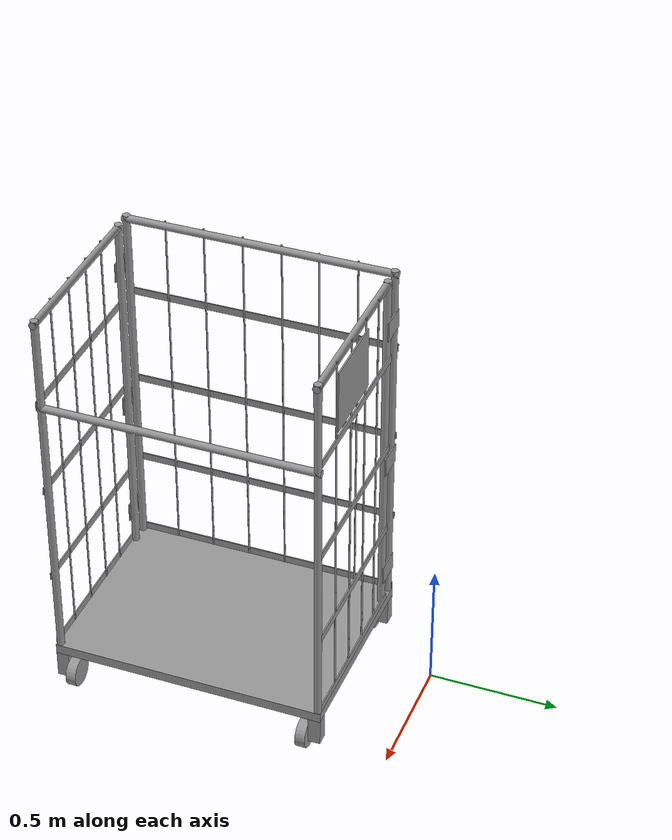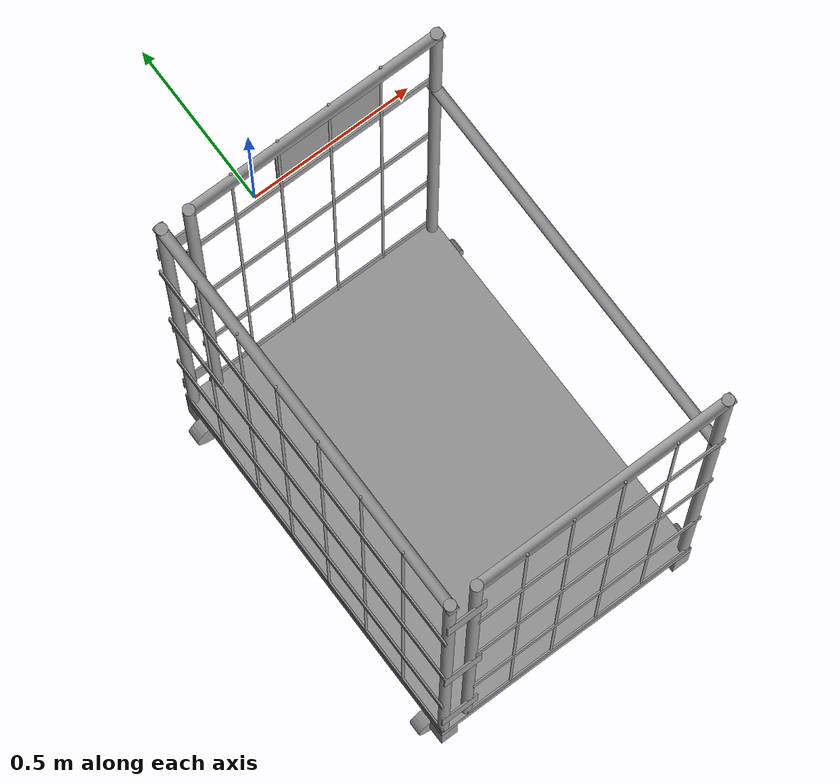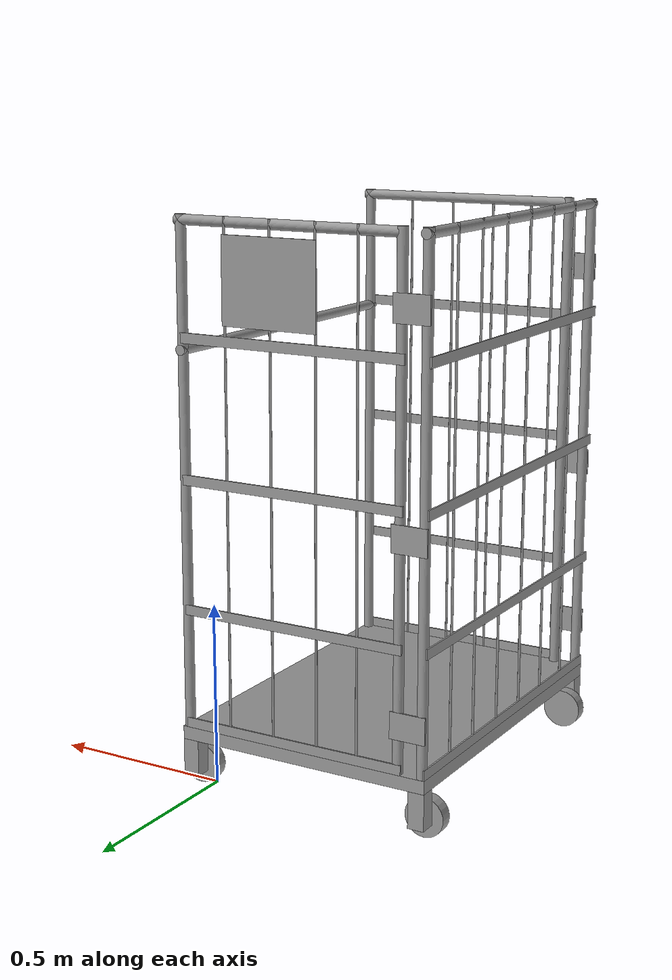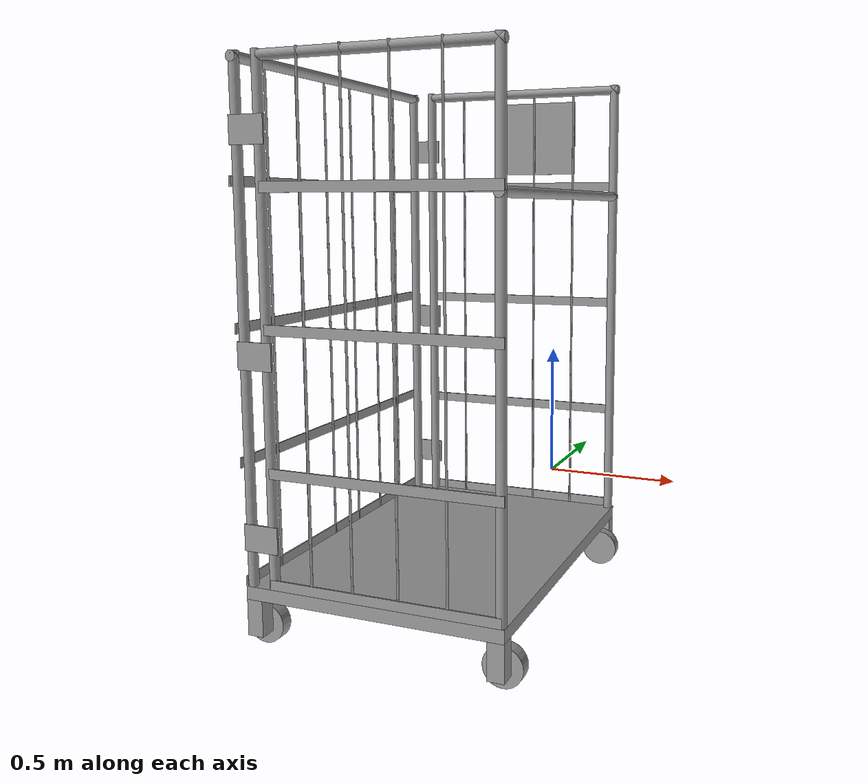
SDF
<?xml version='1.0'?>
<sdf version='1.6'>
  <model name='warehouse_trolley_2'>
    <link name='link_1'>
      <pose frame=''>-0.059879 -0.872257 -0.039145 0 -0 0</pose>
      <inertial>
        <mass>1</mass>
        <inertia>
          <ixx>0.166667</ixx>
          <ixy>0</ixy>
          <ixz>0</ixz>
          <iyy>0.166667</iyy>
          <iyz>0</iyz>
          <izz>0.166667</izz>
        </inertia>
        <pose frame=''>0 0 0 0 -0 0</pose>
      </inertial>
      <self_collide>0</self_collide>
      <kinematic>0</kinematic>
      <visual name='visual'>
        <pose frame=''>0 0 0 0 -0 0</pose>
        <geometry>
          <box>
            <size>0.8 1.1 0.04</size>
          </box>
        </geometry>
        <material>
          <lighting>1</lighting>
          <script>
            <uri>file://media/materials/scripts/gazebo.material</uri>
            <name>Gazebo/Grey</name>
          </script>
          <ambient>0.3 0.3 0.3 1</ambient>
          <diffuse>0.7 0.7 0.7 1</diffuse>
          <specular>0.01 0.01 0.01 1</specular>
          <emissive>0 0 0 1</emissive>
          <shader type='vertex'>
            <normal_map>__default__</normal_map>
          </shader>
        </material>
        <cast_shadows>1</cast_shadows>
        <transparency>0</transparency>
      </visual>
      <collision name='collision'>
        <laser_retro>0</laser_retro>
        <max_contacts>10</max_contacts>
        <pose frame=''>0 0 0 0 -0 0</pose>
        <geometry>
          <box>
            <size>0.8 1.1 0.04</size>
          </box>
        </geometry>
        <surface>
          <friction>
            <ode>
              <mu>1</mu>
              <mu2>1</mu2>
              <fdir1>0 0 0</fdir1>
              <slip1>0</slip1>
              <slip2>0</slip2>
            </ode>
            <torsional>
              <coefficient>1</coefficient>
              <patch_radius>0</patch_radius>
              <surface_radius>0</surface_radius>
              <use_patch_radius>1</use_patch_radius>
              <ode>
                <slip>0</slip>
              </ode>
            </torsional>
          </friction>
          <bounce>
            <restitution_coefficient>0</restitution_coefficient>
            <threshold>1e+06</threshold>
          </bounce>
          <contact>
            <collide_without_contact>0</collide_without_contact>
            <collide_without_contact_bitmask>1</collide_without_contact_bitmask>
            <collide_bitmask>1</collide_bitmask>
            <ode>
              <soft_cfm>0</soft_cfm>
              <soft_erp>0.2</soft_erp>
              <kp>1e+13</kp>
              <kd>1</kd>
              <max_vel>0.01</max_vel>
              <min_depth>0</min_depth>
            </ode>
            <bullet>
              <split_impulse>1</split_impulse>
              <split_impulse_penetration_threshold>-0.01</split_impulse_penetration_threshold>
              <soft_cfm>0</soft_cfm>
              <soft_erp>0.2</soft_erp>
              <kp>1e+13</kp>
              <kd>1</kd>
            </bullet>
          </contact>
        </surface>
      </collision>
    </link>
    <link name='link_0_clone_0'>
      <pose frame=''>-0.434879 -1.35225 -0.15 1.5707 -0 0</pose>
      <inertial>
        <mass>1</mass>
        <inertia>
          <ixx>0.145833</ixx>
          <ixy>0</ixy>
          <ixz>0</ixz>
          <iyy>0.145833</iyy>
          <iyz>0</iyz>
          <izz>0.125</izz>
        </inertia>
        <pose frame=''>0 0 0 0 -0 0</pose>
      </inertial>
      <self_collide>0</self_collide>
      <kinematic>0</kinematic>
      <visual name='visual'>
        <pose frame=''>0 0 0 0 -0 0</pose>
        <geometry>
          <cylinder>
            <radius>0.06</radius>
            <length>0.04</length>
          </cylinder>
        </geometry>
        <material>
          <lighting>1</lighting>
          <script>
            <uri>file://media/materials/scripts/gazebo.material</uri>
            <name>Gazebo/Grey</name>
          </script>
          <ambient>0.3 0.3 0.3 1</ambient>
          <diffuse>0.7 0.7 0.7 1</diffuse>
          <specular>0.01 0.01 0.01 1</specular>
          <emissive>0 0 0 1</emissive>
          <shader type='vertex'>
            <normal_map>__default__</normal_map>
          </shader>
        </material>
        <cast_shadows>1</cast_shadows>
        <transparency>0</transparency>
      </visual>
      <collision name='collision'>
        <laser_retro>0</laser_retro>
        <max_contacts>10</max_contacts>
        <pose frame=''>0 0 0 0 -0 0</pose>
        <geometry>
          <cylinder>
            <radius>0.06</radius>
            <length>0.04</length>
          </cylinder>
        </geometry>
        <surface>
          <friction>
            <ode>
              <mu>1</mu>
              <mu2>1</mu2>
              <fdir1>0 0 0</fdir1>
              <slip1>0</slip1>
              <slip2>0</slip2>
            </ode>
            <torsional>
              <coefficient>1</coefficient>
              <patch_radius>0</patch_radius>
              <surface_radius>0</surface_radius>
              <use_patch_radius>1</use_patch_radius>
              <ode>
                <slip>0</slip>
              </ode>
            </torsional>
          </friction>
          <bounce>
            <restitution_coefficient>0</restitution_coefficient>
            <threshold>1e+06</threshold>
          </bounce>
          <contact>
            <collide_without_contact>0</collide_without_contact>
            <collide_without_contact_bitmask>1</collide_without_contact_bitmask>
            <collide_bitmask>1</collide_bitmask>
            <ode>
              <soft_cfm>0</soft_cfm>
              <soft_erp>0.2</soft_erp>
              <kp>1e+13</kp>
              <kd>1</kd>
              <max_vel>0.01</max_vel>
              <min_depth>0</min_depth>
            </ode>
            <bullet>
              <split_impulse>1</split_impulse>
              <split_impulse_penetration_threshold>-0.01</split_impulse_penetration_threshold>
              <soft_cfm>0</soft_cfm>
              <soft_erp>0.2</soft_erp>
              <kp>1e+13</kp>
              <kd>1</kd>
            </bullet>
          </contact>
        </surface>
      </collision>
    </link>
    <link name='link_0_clone_0_clone'>
      <pose frame=''>0.315121 -1.35225 -0.15 1.5707 -0 0</pose>
      <inertial>
        <mass>1</mass>
        <inertia>
          <ixx>0.145833</ixx>
          <ixy>0</ixy>
          <ixz>0</ixz>
          <iyy>0.145833</iyy>
          <iyz>0</iyz>
          <izz>0.125</izz>
        </inertia>
        <pose frame=''>0 0 0 0 -0 0</pose>
      </inertial>
      <self_collide>0</self_collide>
      <kinematic>0</kinematic>
      <visual name='visual'>
        <pose frame=''>0 0 0 0 -0 0</pose>
        <geometry>
          <cylinder>
            <radius>0.06</radius>
            <length>0.04</length>
          </cylinder>
        </geometry>
        <material>
          <lighting>1</lighting>
          <script>
            <uri>file://media/materials/scripts/gazebo.material</uri>
            <name>Gazebo/Grey</name>
          </script>
          <ambient>0.3 0.3 0.3 1</ambient>
          <diffuse>0.7 0.7 0.7 1</diffuse>
          <specular>0.01 0.01 0.01 1</specular>
          <emissive>0 0 0 1</emissive>
          <shader type='vertex'>
            <normal_map>__default__</normal_map>
          </shader>
        </material>
        <cast_shadows>1</cast_shadows>
        <transparency>0</transparency>
      </visual>
      <collision name='collision'>
        <laser_retro>0</laser_retro>
        <max_contacts>10</max_contacts>
        <pose frame=''>0 0 0 0 -0 0</pose>
        <geometry>
          <cylinder>
            <radius>0.06</radius>
            <length>0.04</length>
          </cylinder>
        </geometry>
        <surface>
          <friction>
            <ode>
              <mu>1</mu>
              <mu2>1</mu2>
              <fdir1>0 0 0</fdir1>
              <slip1>0</slip1>
              <slip2>0</slip2>
            </ode>
            <torsional>
              <coefficient>1</coefficient>
              <patch_radius>0</patch_radius>
              <surface_radius>0</surface_radius>
              <use_patch_radius>1</use_patch_radius>
              <ode>
                <slip>0</slip>
              </ode>
            </torsional>
          </friction>
          <bounce>
            <restitution_coefficient>0</restitution_coefficient>
            <threshold>1e+06</threshold>
          </bounce>
          <contact>
            <collide_without_contact>0</collide_without_contact>
            <collide_without_contact_bitmask>1</collide_without_contact_bitmask>
            <collide_bitmask>1</collide_bitmask>
            <ode>
              <soft_cfm>0</soft_cfm>
              <soft_erp>0.2</soft_erp>
              <kp>1e+13</kp>
              <kd>1</kd>
              <max_vel>0.01</max_vel>
              <min_depth>0</min_depth>
            </ode>
            <bullet>
              <split_impulse>1</split_impulse>
              <split_impulse_penetration_threshold>-0.01</split_impulse_penetration_threshold>
              <soft_cfm>0</soft_cfm>
              <soft_erp>0.2</soft_erp>
              <kp>1e+13</kp>
              <kd>1</kd>
            </bullet>
          </contact>
        </surface>
      </collision>
    </link>
    <link name='link_0_clone_0_clone_0'>
      <pose frame=''>0.315121 -1.39726 -0.114145 0 -0 0</pose>
      <inertial>
        <mass>1</mass>
        <inertia>
          <ixx>0.166667</ixx>
          <ixy>0</ixy>
          <ixz>0</ixz>
          <iyy>0.166667</iyy>
          <iyz>0</iyz>
          <izz>0.166667</izz>
        </inertia>
        <pose frame=''>0 0 0 0 -0 0</pose>
      </inertial>
      <self_collide>0</self_collide>
      <kinematic>0</kinematic>
      <visual name='visual'>
        <pose frame=''>0 0 0 0 -0 0</pose>
        <geometry>
          <box>
            <size>0.05 0.05 0.11</size>
          </box>
        </geometry>
        <material>
          <lighting>1</lighting>
          <script>
            <uri>file://media/materials/scripts/gazebo.material</uri>
            <name>Gazebo/Grey</name>
          </script>
          <ambient>0.3 0.3 0.3 1</ambient>
          <diffuse>0.7 0.7 0.7 1</diffuse>
          <specular>0.01 0.01 0.01 1</specular>
          <emissive>0 0 0 1</emissive>
          <shader type='vertex'>
            <normal_map>__default__</normal_map>
          </shader>
        </material>
        <cast_shadows>1</cast_shadows>
        <transparency>0</transparency>
      </visual>
      <collision name='collision'>
        <laser_retro>0</laser_retro>
        <max_contacts>10</max_contacts>
        <pose frame=''>0 0 0 0 -0 0</pose>
        <geometry>
          <box>
            <size>0.05 0.05 0.11</size>
          </box>
        </geometry>
        <surface>
          <friction>
            <ode>
              <mu>1</mu>
              <mu2>1</mu2>
              <fdir1>0 0 0</fdir1>
              <slip1>0</slip1>
              <slip2>0</slip2>
            </ode>
            <torsional>
              <coefficient>1</coefficient>
              <patch_radius>0</patch_radius>
              <surface_radius>0</surface_radius>
              <use_patch_radius>1</use_patch_radius>
              <ode>
                <slip>0</slip>
              </ode>
            </torsional>
          </friction>
          <bounce>
            <restitution_coefficient>0</restitution_coefficient>
            <threshold>1e+06</threshold>
          </bounce>
          <contact>
            <collide_without_contact>0</collide_without_contact>
            <collide_without_contact_bitmask>1</collide_without_contact_bitmask>
            <collide_bitmask>1</collide_bitmask>
            <ode>
              <soft_cfm>0</soft_cfm>
              <soft_erp>0.2</soft_erp>
              <kp>1e+13</kp>
              <kd>1</kd>
              <max_vel>0.01</max_vel>
              <min_depth>0</min_depth>
            </ode>
            <bullet>
              <split_impulse>1</split_impulse>
              <split_impulse_penetration_threshold>-0.01</split_impulse_penetration_threshold>
              <soft_cfm>0</soft_cfm>
              <soft_erp>0.2</soft_erp>
              <kp>1e+13</kp>
              <kd>1</kd>
            </bullet>
          </contact>
        </surface>
      </collision>
    </link>
    <link name='link_0_clone_0_clone_0_clone'>
      <pose frame=''>-0.434879 -1.39726 -0.114145 0 -0 0</pose>
      <inertial>
        <mass>1</mass>
        <inertia>
          <ixx>0.166667</ixx>
          <ixy>0</ixy>
          <ixz>0</ixz>
          <iyy>0.166667</iyy>
          <iyz>0</iyz>
          <izz>0.166667</izz>
        </inertia>
        <pose frame=''>0 0 0 0 -0 0</pose>
      </inertial>
      <self_collide>0</self_collide>
      <kinematic>0</kinematic>
      <visual name='visual'>
        <pose frame=''>0 0 0 0 -0 0</pose>
        <geometry>
          <box>
            <size>0.05 0.05 0.11</size>
          </box>
        </geometry>
        <material>
          <lighting>1</lighting>
          <script>
            <uri>file://media/materials/scripts/gazebo.material</uri>
            <name>Gazebo/Grey</name>
          </script>
          <ambient>0.3 0.3 0.3 1</ambient>
          <diffuse>0.7 0.7 0.7 1</diffuse>
          <specular>0.01 0.01 0.01 1</specular>
          <emissive>0 0 0 1</emissive>
          <shader type='vertex'>
            <normal_map>__default__</normal_map>
          </shader>
        </material>
        <cast_shadows>1</cast_shadows>
        <transparency>0</transparency>
      </visual>
      <collision name='collision'>
        <laser_retro>0</laser_retro>
        <max_contacts>10</max_contacts>
        <pose frame=''>0 0 0 0 -0 0</pose>
        <geometry>
          <box>
            <size>0.05 0.05 0.11</size>
          </box>
        </geometry>
        <surface>
          <friction>
            <ode>
              <mu>1</mu>
              <mu2>1</mu2>
              <fdir1>0 0 0</fdir1>
              <slip1>0</slip1>
              <slip2>0</slip2>
            </ode>
            <torsional>
              <coefficient>1</coefficient>
              <patch_radius>0</patch_radius>
              <surface_radius>0</surface_radius>
              <use_patch_radius>1</use_patch_radius>
              <ode>
                <slip>0</slip>
              </ode>
            </torsional>
          </friction>
          <bounce>
            <restitution_coefficient>0</restitution_coefficient>
            <threshold>1e+06</threshold>
          </bounce>
          <contact>
            <collide_without_contact>0</collide_without_contact>
            <collide_without_contact_bitmask>1</collide_without_contact_bitmask>
            <collide_bitmask>1</collide_bitmask>
            <ode>
              <soft_cfm>0</soft_cfm>
              <soft_erp>0.2</soft_erp>
              <kp>1e+13</kp>
              <kd>1</kd>
              <max_vel>0.01</max_vel>
              <min_depth>0</min_depth>
            </ode>
            <bullet>
              <split_impulse>1</split_impulse>
              <split_impulse_penetration_threshold>-0.01</split_impulse_penetration_threshold>
              <soft_cfm>0</soft_cfm>
              <soft_erp>0.2</soft_erp>
              <kp>1e+13</kp>
              <kd>1</kd>
            </bullet>
          </contact>
        </surface>
      </collision>
    </link>
    <link name='link_0_clone_0_clone_0_clone_0'>
      <pose frame=''>0.315121 -0.347257 -0.114145 0 -0 0</pose>
      <inertial>
        <mass>1</mass>
        <inertia>
          <ixx>0.166667</ixx>
          <ixy>0</ixy>
          <ixz>0</ixz>
          <iyy>0.166667</iyy>
          <iyz>0</iyz>
          <izz>0.166667</izz>
        </inertia>
        <pose frame=''>0 0 0 0 -0 0</pose>
      </inertial>
      <self_collide>0</self_collide>
      <kinematic>0</kinematic>
      <visual name='visual'>
        <pose frame=''>0 0 0 0 -0 0</pose>
        <geometry>
          <box>
            <size>0.05 0.05 0.11</size>
          </box>
        </geometry>
        <material>
          <lighting>1</lighting>
          <script>
            <uri>file://media/materials/scripts/gazebo.material</uri>
            <name>Gazebo/Grey</name>
          </script>
          <ambient>0.3 0.3 0.3 1</ambient>
          <diffuse>0.7 0.7 0.7 1</diffuse>
          <specular>0.01 0.01 0.01 1</specular>
          <emissive>0 0 0 1</emissive>
          <shader type='vertex'>
            <normal_map>__default__</normal_map>
          </shader>
        </material>
        <cast_shadows>1</cast_shadows>
        <transparency>0</transparency>
      </visual>
      <collision name='collision'>
        <laser_retro>0</laser_retro>
        <max_contacts>10</max_contacts>
        <pose frame=''>0 0 0 0 -0 0</pose>
        <geometry>
          <box>
            <size>0.05 0.05 0.11</size>
          </box>
        </geometry>
        <surface>
          <friction>
            <ode>
              <mu>1</mu>
              <mu2>1</mu2>
              <fdir1>0 0 0</fdir1>
              <slip1>0</slip1>
              <slip2>0</slip2>
            </ode>
            <torsional>
              <coefficient>1</coefficient>
              <patch_radius>0</patch_radius>
              <surface_radius>0</surface_radius>
              <use_patch_radius>1</use_patch_radius>
              <ode>
                <slip>0</slip>
              </ode>
            </torsional>
          </friction>
          <bounce>
            <restitution_coefficient>0</restitution_coefficient>
            <threshold>1e+06</threshold>
          </bounce>
          <contact>
            <collide_without_contact>0</collide_without_contact>
            <collide_without_contact_bitmask>1</collide_without_contact_bitmask>
            <collide_bitmask>1</collide_bitmask>
            <ode>
              <soft_cfm>0</soft_cfm>
              <soft_erp>0.2</soft_erp>
              <kp>1e+13</kp>
              <kd>1</kd>
              <max_vel>0.01</max_vel>
              <min_depth>0</min_depth>
            </ode>
            <bullet>
              <split_impulse>1</split_impulse>
              <split_impulse_penetration_threshold>-0.01</split_impulse_penetration_threshold>
              <soft_cfm>0</soft_cfm>
              <soft_erp>0.2</soft_erp>
              <kp>1e+13</kp>
              <kd>1</kd>
            </bullet>
          </contact>
        </surface>
      </collision>
    </link>
    <link name='link_0_clone_0_clone_0_clone_1'>
      <pose frame=''>-0.434879 -0.347257 -0.114145 0 -0 0</pose>
      <inertial>
        <mass>1</mass>
        <inertia>
          <ixx>0.166667</ixx>
          <ixy>0</ixy>
          <ixz>0</ixz>
          <iyy>0.166667</iyy>
          <iyz>0</iyz>
          <izz>0.166667</izz>
        </inertia>
        <pose frame=''>0 0 0 0 -0 0</pose>
      </inertial>
      <self_collide>0</self_collide>
      <kinematic>0</kinematic>
      <visual name='visual'>
        <pose frame=''>0 0 0 0 -0 0</pose>
        <geometry>
          <box>
            <size>0.05 0.05 0.11</size>
          </box>
        </geometry>
        <material>
          <lighting>1</lighting>
          <script>
            <uri>file://media/materials/scripts/gazebo.material</uri>
            <name>Gazebo/Grey</name>
          </script>
          <ambient>0.3 0.3 0.3 1</ambient>
          <diffuse>0.7 0.7 0.7 1</diffuse>
          <specular>0.01 0.01 0.01 1</specular>
          <emissive>0 0 0 1</emissive>
          <shader type='vertex'>
            <normal_map>__default__</normal_map>
          </shader>
        </material>
        <cast_shadows>1</cast_shadows>
        <transparency>0</transparency>
      </visual>
      <collision name='collision'>
        <laser_retro>0</laser_retro>
        <max_contacts>10</max_contacts>
        <pose frame=''>0 0 0 0 -0 0</pose>
        <geometry>
          <box>
            <size>0.05 0.05 0.11</size>
          </box>
        </geometry>
        <surface>
          <friction>
            <ode>
              <mu>1</mu>
              <mu2>1</mu2>
              <fdir1>0 0 0</fdir1>
              <slip1>0</slip1>
              <slip2>0</slip2>
            </ode>
            <torsional>
              <coefficient>1</coefficient>
              <patch_radius>0</patch_radius>
              <surface_radius>0</surface_radius>
              <use_patch_radius>1</use_patch_radius>
              <ode>
                <slip>0</slip>
              </ode>
            </torsional>
          </friction>
          <bounce>
            <restitution_coefficient>0</restitution_coefficient>
            <threshold>1e+06</threshold>
          </bounce>
          <contact>
            <collide_without_contact>0</collide_without_contact>
            <collide_without_contact_bitmask>1</collide_without_contact_bitmask>
            <collide_bitmask>1</collide_bitmask>
            <ode>
              <soft_cfm>0</soft_cfm>
              <soft_erp>0.2</soft_erp>
              <kp>1e+13</kp>
              <kd>1</kd>
              <max_vel>0.01</max_vel>
              <min_depth>0</min_depth>
            </ode>
            <bullet>
              <split_impulse>1</split_impulse>
              <split_impulse_penetration_threshold>-0.01</split_impulse_penetration_threshold>
              <soft_cfm>0</soft_cfm>
              <soft_erp>0.2</soft_erp>
              <kp>1e+13</kp>
              <kd>1</kd>
            </bullet>
          </contact>
        </surface>
      </collision>
    </link>
    <link name='link_0_clone_0_clone_2'>
      <pose frame=''>0.315121 -0.392263 -0.15 1.5707 -0 0</pose>
      <inertial>
        <mass>1</mass>
        <inertia>
          <ixx>0.145833</ixx>
          <ixy>0</ixy>
          <ixz>0</ixz>
          <iyy>0.145833</iyy>
          <iyz>0</iyz>
          <izz>0.125</izz>
        </inertia>
        <pose frame=''>0 0 0 0 -0 0</pose>
      </inertial>
      <self_collide>0</self_collide>
      <kinematic>0</kinematic>
      <visual name='visual'>
        <pose frame=''>0 0 0 0 -0 0</pose>
        <geometry>
          <cylinder>
            <radius>0.06</radius>
            <length>0.04</length>
          </cylinder>
        </geometry>
        <material>
          <lighting>1</lighting>
          <script>
            <uri>file://media/materials/scripts/gazebo.material</uri>
            <name>Gazebo/Grey</name>
          </script>
          <ambient>0.3 0.3 0.3 1</ambient>
          <diffuse>0.7 0.7 0.7 1</diffuse>
          <specular>0.01 0.01 0.01 1</specular>
          <emissive>0 0 0 1</emissive>
          <shader type='vertex'>
            <normal_map>__default__</normal_map>
          </shader>
        </material>
        <cast_shadows>1</cast_shadows>
        <transparency>0</transparency>
      </visual>
      <collision name='collision'>
        <laser_retro>0</laser_retro>
        <max_contacts>10</max_contacts>
        <pose frame=''>0 0 0 0 -0 0</pose>
        <geometry>
          <cylinder>
            <radius>0.06</radius>
            <length>0.04</length>
          </cylinder>
        </geometry>
        <surface>
          <friction>
            <ode>
              <mu>1</mu>
              <mu2>1</mu2>
              <fdir1>0 0 0</fdir1>
              <slip1>0</slip1>
              <slip2>0</slip2>
            </ode>
            <torsional>
              <coefficient>1</coefficient>
              <patch_radius>0</patch_radius>
              <surface_radius>0</surface_radius>
              <use_patch_radius>1</use_patch_radius>
              <ode>
                <slip>0</slip>
              </ode>
            </torsional>
          </friction>
          <bounce>
            <restitution_coefficient>0</restitution_coefficient>
            <threshold>1e+06</threshold>
          </bounce>
          <contact>
            <collide_without_contact>0</collide_without_contact>
            <collide_without_contact_bitmask>1</collide_without_contact_bitmask>
            <collide_bitmask>1</collide_bitmask>
            <ode>
              <soft_cfm>0</soft_cfm>
              <soft_erp>0.2</soft_erp>
              <kp>1e+13</kp>
              <kd>1</kd>
              <max_vel>0.01</max_vel>
              <min_depth>0</min_depth>
            </ode>
            <bullet>
              <split_impulse>1</split_impulse>
              <split_impulse_penetration_threshold>-0.01</split_impulse_penetration_threshold>
              <soft_cfm>0</soft_cfm>
              <soft_erp>0.2</soft_erp>
              <kp>1e+13</kp>
              <kd>1</kd>
            </bullet>
          </contact>
        </surface>
      </collision>
    </link>
    <link name='link_0_clone_0_clone_2_clone'>
      <pose frame=''>-0.434879 -0.392263 -0.15 1.5707 -0 0</pose>
      <inertial>
        <mass>1</mass>
        <inertia>
          <ixx>0.145833</ixx>
          <ixy>0</ixy>
          <ixz>0</ixz>
          <iyy>0.145833</iyy>
          <iyz>0</iyz>
          <izz>0.125</izz>
        </inertia>
        <pose frame=''>0 0 0 0 -0 0</pose>
      </inertial>
      <self_collide>0</self_collide>
      <kinematic>0</kinematic>
      <visual name='visual'>
        <pose frame=''>0 0 0 0 -0 0</pose>
        <geometry>
          <cylinder>
            <radius>0.06</radius>
            <length>0.04</length>
          </cylinder>
        </geometry>
        <material>
          <lighting>1</lighting>
          <script>
            <uri>file://media/materials/scripts/gazebo.material</uri>
            <name>Gazebo/Grey</name>
          </script>
          <ambient>0.3 0.3 0.3 1</ambient>
          <diffuse>0.7 0.7 0.7 1</diffuse>
          <specular>0.01 0.01 0.01 1</specular>
          <emissive>0 0 0 1</emissive>
          <shader type='vertex'>
            <normal_map>__default__</normal_map>
          </shader>
        </material>
        <cast_shadows>1</cast_shadows>
        <transparency>0</transparency>
      </visual>
      <collision name='collision'>
        <laser_retro>0</laser_retro>
        <max_contacts>10</max_contacts>
        <pose frame=''>0 0 0 0 -0 0</pose>
        <geometry>
          <cylinder>
            <radius>0.06</radius>
            <length>0.04</length>
          </cylinder>
        </geometry>
        <surface>
          <friction>
            <ode>
              <mu>1</mu>
              <mu2>1</mu2>
              <fdir1>0 0 0</fdir1>
              <slip1>0</slip1>
              <slip2>0</slip2>
            </ode>
            <torsional>
              <coefficient>1</coefficient>
              <patch_radius>0</patch_radius>
              <surface_radius>0</surface_radius>
              <use_patch_radius>1</use_patch_radius>
              <ode>
                <slip>0</slip>
              </ode>
            </torsional>
          </friction>
          <bounce>
            <restitution_coefficient>0</restitution_coefficient>
            <threshold>1e+06</threshold>
          </bounce>
          <contact>
            <collide_without_contact>0</collide_without_contact>
            <collide_without_contact_bitmask>1</collide_without_contact_bitmask>
            <collide_bitmask>1</collide_bitmask>
            <ode>
              <soft_cfm>0</soft_cfm>
              <soft_erp>0.2</soft_erp>
              <kp>1e+13</kp>
              <kd>1</kd>
              <max_vel>0.01</max_vel>
              <min_depth>0</min_depth>
            </ode>
            <bullet>
              <split_impulse>1</split_impulse>
              <split_impulse_penetration_threshold>-0.01</split_impulse_penetration_threshold>
              <soft_cfm>0</soft_cfm>
              <soft_erp>0.2</soft_erp>
              <kp>1e+13</kp>
              <kd>1</kd>
            </bullet>
          </contact>
        </surface>
      </collision>
    </link>
    <link name='link_2_clone_0'>
      <pose frame=''>-0.444879 -0.337257 0.730855 0 -0 0</pose>
      <inertial>
        <mass>1</mass>
        <inertia>
          <ixx>0.145833</ixx>
          <ixy>0</ixy>
          <ixz>0</ixz>
          <iyy>0.145833</iyy>
          <iyz>0</iyz>
          <izz>0.125</izz>
        </inertia>
        <pose frame=''>0 0 0 0 -0 0</pose>
      </inertial>
      <self_collide>0</self_collide>
      <kinematic>0</kinematic>
      <visual name='visual'>
        <pose frame=''>0 0 0 0 -0 0</pose>
        <geometry>
          <cylinder>
            <radius>0.015</radius>
            <length>1.5</length>
          </cylinder>
        </geometry>
        <material>
          <lighting>1</lighting>
          <script>
            <uri>file://media/materials/scripts/gazebo.material</uri>
            <name>Gazebo/Grey</name>
          </script>
          <ambient>0.3 0.3 0.3 1</ambient>
          <diffuse>0.7 0.7 0.7 1</diffuse>
          <specular>0.01 0.01 0.01 1</specular>
          <emissive>0 0 0 1</emissive>
          <shader type='vertex'>
            <normal_map>__default__</normal_map>
          </shader>
        </material>
        <cast_shadows>1</cast_shadows>
        <transparency>0</transparency>
      </visual>
      <collision name='collision'>
        <laser_retro>0</laser_retro>
        <max_contacts>10</max_contacts>
        <pose frame=''>0 0 0 0 -0 0</pose>
        <geometry>
          <cylinder>
            <radius>0.015</radius>
            <length>1.5</length>
          </cylinder>
        </geometry>
        <surface>
          <friction>
            <ode>
              <mu>1</mu>
              <mu2>1</mu2>
              <fdir1>0 0 0</fdir1>
              <slip1>0</slip1>
              <slip2>0</slip2>
            </ode>
            <torsional>
              <coefficient>1</coefficient>
              <patch_radius>0</patch_radius>
              <surface_radius>0</surface_radius>
              <use_patch_radius>1</use_patch_radius>
              <ode>
                <slip>0</slip>
              </ode>
            </torsional>
          </friction>
          <bounce>
            <restitution_coefficient>0</restitution_coefficient>
            <threshold>1e+06</threshold>
          </bounce>
          <contact>
            <collide_without_contact>0</collide_without_contact>
            <collide_without_contact_bitmask>1</collide_without_contact_bitmask>
            <collide_bitmask>1</collide_bitmask>
            <ode>
              <soft_cfm>0</soft_cfm>
              <soft_erp>0.2</soft_erp>
              <kp>1e+13</kp>
              <kd>1</kd>
              <max_vel>0.01</max_vel>
              <min_depth>0</min_depth>
            </ode>
            <bullet>
              <split_impulse>1</split_impulse>
              <split_impulse_penetration_threshold>-0.01</split_impulse_penetration_threshold>
              <soft_cfm>0</soft_cfm>
              <soft_erp>0.2</soft_erp>
              <kp>1e+13</kp>
              <kd>1</kd>
            </bullet>
          </contact>
        </surface>
      </collision>
    </link>
    <link name='link_2_clone_0_clone'>
      <pose frame=''>-0.444879 -1.40726 0.730855 0 -0 0</pose>
      <inertial>
        <mass>1</mass>
        <inertia>
          <ixx>0.145833</ixx>
          <ixy>0</ixy>
          <ixz>0</ixz>
          <iyy>0.145833</iyy>
          <iyz>0</iyz>
          <izz>0.125</izz>
        </inertia>
        <pose frame=''>0 0 0 0 -0 0</pose>
      </inertial>
      <self_collide>0</self_collide>
      <kinematic>0</kinematic>
      <visual name='visual'>
        <pose frame=''>0 0 0 0 -0 0</pose>
        <geometry>
          <cylinder>
            <radius>0.015</radius>
            <length>1.5</length>
          </cylinder>
        </geometry>
        <material>
          <lighting>1</lighting>
          <script>
            <uri>file://media/materials/scripts/gazebo.material</uri>
            <name>Gazebo/Grey</name>
          </script>
          <ambient>0.3 0.3 0.3 1</ambient>
          <diffuse>0.7 0.7 0.7 1</diffuse>
          <specular>0.01 0.01 0.01 1</specular>
          <emissive>0 0 0 1</emissive>
          <shader type='vertex'>
            <normal_map>__default__</normal_map>
          </shader>
        </material>
        <cast_shadows>1</cast_shadows>
        <transparency>0</transparency>
      </visual>
      <collision name='collision'>
        <laser_retro>0</laser_retro>
        <max_contacts>10</max_contacts>
        <pose frame=''>0 0 0 0 -0 0</pose>
        <geometry>
          <cylinder>
            <radius>0.015</radius>
            <length>1.5</length>
          </cylinder>
        </geometry>
        <surface>
          <friction>
            <ode>
              <mu>1</mu>
              <mu2>1</mu2>
              <fdir1>0 0 0</fdir1>
              <slip1>0</slip1>
              <slip2>0</slip2>
            </ode>
            <torsional>
              <coefficient>1</coefficient>
              <patch_radius>0</patch_radius>
              <surface_radius>0</surface_radius>
              <use_patch_radius>1</use_patch_radius>
              <ode>
                <slip>0</slip>
              </ode>
            </torsional>
          </friction>
          <bounce>
            <restitution_coefficient>0</restitution_coefficient>
            <threshold>1e+06</threshold>
          </bounce>
          <contact>
            <collide_without_contact>0</collide_without_contact>
            <collide_without_contact_bitmask>1</collide_without_contact_bitmask>
            <collide_bitmask>1</collide_bitmask>
            <ode>
              <soft_cfm>0</soft_cfm>
              <soft_erp>0.2</soft_erp>
              <kp>1e+13</kp>
              <kd>1</kd>
              <max_vel>0.01</max_vel>
              <min_depth>0</min_depth>
            </ode>
            <bullet>
              <split_impulse>1</split_impulse>
              <split_impulse_penetration_threshold>-0.01</split_impulse_penetration_threshold>
              <soft_cfm>0</soft_cfm>
              <soft_erp>0.2</soft_erp>
              <kp>1e+13</kp>
              <kd>1</kd>
            </bullet>
          </contact>
        </surface>
      </collision>
    </link>
    <link name='link_2_clone_0_clone_0'>
      <pose frame=''>-0.371796 -1.40726 0.730855 0 -0 0</pose>
      <inertial>
        <mass>1</mass>
        <inertia>
          <ixx>0.145833</ixx>
          <ixy>0</ixy>
          <ixz>0</ixz>
          <iyy>0.145833</iyy>
          <iyz>0</iyz>
          <izz>0.125</izz>
        </inertia>
        <pose frame=''>0 0 0 0 -0 0</pose>
      </inertial>
      <self_collide>0</self_collide>
      <kinematic>0</kinematic>
      <visual name='visual'>
        <pose frame=''>0 0 0 0 -0 0</pose>
        <geometry>
          <cylinder>
            <radius>0.015</radius>
            <length>1.5</length>
          </cylinder>
        </geometry>
        <material>
          <lighting>1</lighting>
          <script>
            <uri>file://media/materials/scripts/gazebo.material</uri>
            <name>Gazebo/Grey</name>
          </script>
          <ambient>0.3 0.3 0.3 1</ambient>
          <diffuse>0.7 0.7 0.7 1</diffuse>
          <specular>0.01 0.01 0.01 1</specular>
          <emissive>0 0 0 1</emissive>
          <shader type='vertex'>
            <normal_map>__default__</normal_map>
          </shader>
        </material>
        <cast_shadows>1</cast_shadows>
        <transparency>0</transparency>
      </visual>
      <collision name='collision'>
        <laser_retro>0</laser_retro>
        <max_contacts>10</max_contacts>
        <pose frame=''>0 0 0 0 -0 0</pose>
        <geometry>
          <cylinder>
            <radius>0.015</radius>
            <length>1.5</length>
          </cylinder>
        </geometry>
        <surface>
          <friction>
            <ode>
              <mu>1</mu>
              <mu2>1</mu2>
              <fdir1>0 0 0</fdir1>
              <slip1>0</slip1>
              <slip2>0</slip2>
            </ode>
            <torsional>
              <coefficient>1</coefficient>
              <patch_radius>0</patch_radius>
              <surface_radius>0</surface_radius>
              <use_patch_radius>1</use_patch_radius>
              <ode>
                <slip>0</slip>
              </ode>
            </torsional>
          </friction>
          <bounce>
            <restitution_coefficient>0</restitution_coefficient>
            <threshold>1e+06</threshold>
          </bounce>
          <contact>
            <collide_without_contact>0</collide_without_contact>
            <collide_without_contact_bitmask>1</collide_without_contact_bitmask>
            <collide_bitmask>1</collide_bitmask>
            <ode>
              <soft_cfm>0</soft_cfm>
              <soft_erp>0.2</soft_erp>
              <kp>1e+13</kp>
              <kd>1</kd>
              <max_vel>0.01</max_vel>
              <min_depth>0</min_depth>
            </ode>
            <bullet>
              <split_impulse>1</split_impulse>
              <split_impulse_penetration_threshold>-0.01</split_impulse_penetration_threshold>
              <soft_cfm>0</soft_cfm>
              <soft_erp>0.2</soft_erp>
              <kp>1e+13</kp>
              <kd>1</kd>
            </bullet>
          </contact>
        </surface>
      </collision>
    </link>
    <link name='link_2_clone_0_clone_1'>
      <pose frame=''>0.325121 -1.40726 0.730855 0 -0 0</pose>
      <inertial>
        <mass>1</mass>
        <inertia>
          <ixx>0.145833</ixx>
          <ixy>0</ixy>
          <ixz>0</ixz>
          <iyy>0.145833</iyy>
          <iyz>0</iyz>
          <izz>0.125</izz>
        </inertia>
        <pose frame=''>0 0 0 0 -0 0</pose>
      </inertial>
      <self_collide>0</self_collide>
      <kinematic>0</kinematic>
      <visual name='visual'>
        <pose frame=''>0 0 0 0 -0 0</pose>
        <geometry>
          <cylinder>
            <radius>0.015</radius>
            <length>1.5</length>
          </cylinder>
        </geometry>
        <material>
          <lighting>1</lighting>
          <script>
            <uri>file://media/materials/scripts/gazebo.material</uri>
            <name>Gazebo/Grey</name>
          </script>
          <ambient>0.3 0.3 0.3 1</ambient>
          <diffuse>0.7 0.7 0.7 1</diffuse>
          <specular>0.01 0.01 0.01 1</specular>
          <emissive>0 0 0 1</emissive>
          <shader type='vertex'>
            <normal_map>__default__</normal_map>
          </shader>
        </material>
        <cast_shadows>1</cast_shadows>
        <transparency>0</transparency>
      </visual>
      <collision name='collision'>
        <laser_retro>0</laser_retro>
        <max_contacts>10</max_contacts>
        <pose frame=''>0 0 0 0 -0 0</pose>
        <geometry>
          <cylinder>
            <radius>0.015</radius>
            <length>1.5</length>
          </cylinder>
        </geometry>
        <surface>
          <friction>
            <ode>
              <mu>1</mu>
              <mu2>1</mu2>
              <fdir1>0 0 0</fdir1>
              <slip1>0</slip1>
              <slip2>0</slip2>
            </ode>
            <torsional>
              <coefficient>1</coefficient>
              <patch_radius>0</patch_radius>
              <surface_radius>0</surface_radius>
              <use_patch_radius>1</use_patch_radius>
              <ode>
                <slip>0</slip>
              </ode>
            </torsional>
          </friction>
          <bounce>
            <restitution_coefficient>0</restitution_coefficient>
            <threshold>1e+06</threshold>
          </bounce>
          <contact>
            <collide_without_contact>0</collide_without_contact>
            <collide_without_contact_bitmask>1</collide_without_contact_bitmask>
            <collide_bitmask>1</collide_bitmask>
            <ode>
              <soft_cfm>0</soft_cfm>
              <soft_erp>0.2</soft_erp>
              <kp>1e+13</kp>
              <kd>1</kd>
              <max_vel>0.01</max_vel>
              <min_depth>0</min_depth>
            </ode>
            <bullet>
              <split_impulse>1</split_impulse>
              <split_impulse_penetration_threshold>-0.01</split_impulse_penetration_threshold>
              <soft_cfm>0</soft_cfm>
              <soft_erp>0.2</soft_erp>
              <kp>1e+13</kp>
              <kd>1</kd>
            </bullet>
          </contact>
        </surface>
      </collision>
    </link>
    <link name='link_2_clone_0_clone_clone'>
      <pose frame=''>0.177056 -1.41876 0.730855 0 -0 0</pose>
      <inertial>
        <mass>1</mass>
        <inertia>
          <ixx>0.145833</ixx>
          <ixy>0</ixy>
          <ixz>0</ixz>
          <iyy>0.145833</iyy>
          <iyz>0</iyz>
          <izz>0.125</izz>
        </inertia>
        <pose frame=''>0 0 0 0 -0 0</pose>
      </inertial>
      <self_collide>0</self_collide>
      <kinematic>0</kinematic>
      <visual name='visual'>
        <pose frame=''>0 0 0 0 -0 0</pose>
        <geometry>
          <cylinder>
            <radius>0.0035</radius>
            <length>1.5</length>
          </cylinder>
        </geometry>
        <material>
          <lighting>1</lighting>
          <script>
            <uri>file://media/materials/scripts/gazebo.material</uri>
            <name>Gazebo/Grey</name>
          </script>
          <ambient>0.3 0.3 0.3 1</ambient>
          <diffuse>0.7 0.7 0.7 1</diffuse>
          <specular>0.01 0.01 0.01 1</specular>
          <emissive>0 0 0 1</emissive>
          <shader type='vertex'>
            <normal_map>__default__</normal_map>
          </shader>
        </material>
        <cast_shadows>1</cast_shadows>
        <transparency>0</transparency>
      </visual>
      <collision name='collision'>
        <laser_retro>0</laser_retro>
        <max_contacts>10</max_contacts>
        <pose frame=''>0 0 0 0 -0 0</pose>
        <geometry>
          <cylinder>
            <radius>0.0035</radius>
            <length>1.5</length>
          </cylinder>
        </geometry>
        <surface>
          <friction>
            <ode>
              <mu>1</mu>
              <mu2>1</mu2>
              <fdir1>0 0 0</fdir1>
              <slip1>0</slip1>
              <slip2>0</slip2>
            </ode>
            <torsional>
              <coefficient>1</coefficient>
              <patch_radius>0</patch_radius>
              <surface_radius>0</surface_radius>
              <use_patch_radius>1</use_patch_radius>
              <ode>
                <slip>0</slip>
              </ode>
            </torsional>
          </friction>
          <bounce>
            <restitution_coefficient>0</restitution_coefficient>
            <threshold>1e+06</threshold>
          </bounce>
          <contact>
            <collide_without_contact>0</collide_without_contact>
            <collide_without_contact_bitmask>1</collide_without_contact_bitmask>
            <collide_bitmask>1</collide_bitmask>
            <ode>
              <soft_cfm>0</soft_cfm>
              <soft_erp>0.2</soft_erp>
              <kp>1e+13</kp>
              <kd>1</kd>
              <max_vel>0.01</max_vel>
              <min_depth>0</min_depth>
            </ode>
            <bullet>
              <split_impulse>1</split_impulse>
              <split_impulse_penetration_threshold>-0.01</split_impulse_penetration_threshold>
              <soft_cfm>0</soft_cfm>
              <soft_erp>0.2</soft_erp>
              <kp>1e+13</kp>
              <kd>1</kd>
            </bullet>
          </contact>
        </surface>
      </collision>
    </link>
    <link name='link_2_clone_0_clone_clone_clone'>
      <pose frame=''>-0.241474 -1.41876 0.730855 0 -0 0</pose>
      <inertial>
        <mass>1</mass>
        <inertia>
          <ixx>0.145833</ixx>
          <ixy>0</ixy>
          <ixz>0</ixz>
          <iyy>0.145833</iyy>
          <iyz>0</iyz>
          <izz>0.125</izz>
        </inertia>
        <pose frame=''>0 0 0 0 -0 0</pose>
      </inertial>
      <self_collide>0</self_collide>
      <kinematic>0</kinematic>
      <visual name='visual'>
        <pose frame=''>0 0 0 0 -0 0</pose>
        <geometry>
          <cylinder>
            <radius>0.0035</radius>
            <length>1.5</length>
          </cylinder>
        </geometry>
        <material>
          <lighting>1</lighting>
          <script>
            <uri>file://media/materials/scripts/gazebo.material</uri>
            <name>Gazebo/Grey</name>
          </script>
          <ambient>0.3 0.3 0.3 1</ambient>
          <diffuse>0.7 0.7 0.7 1</diffuse>
          <specular>0.01 0.01 0.01 1</specular>
          <emissive>0 0 0 1</emissive>
          <shader type='vertex'>
            <normal_map>__default__</normal_map>
          </shader>
        </material>
        <cast_shadows>1</cast_shadows>
        <transparency>0</transparency>
      </visual>
      <collision name='collision'>
        <laser_retro>0</laser_retro>
        <max_contacts>10</max_contacts>
        <pose frame=''>0 0 0 0 -0 0</pose>
        <geometry>
          <cylinder>
            <radius>0.0035</radius>
            <length>1.5</length>
          </cylinder>
        </geometry>
        <surface>
          <friction>
            <ode>
              <mu>1</mu>
              <mu2>1</mu2>
              <fdir1>0 0 0</fdir1>
              <slip1>0</slip1>
              <slip2>0</slip2>
            </ode>
            <torsional>
              <coefficient>1</coefficient>
              <patch_radius>0</patch_radius>
              <surface_radius>0</surface_radius>
              <use_patch_radius>1</use_patch_radius>
              <ode>
                <slip>0</slip>
              </ode>
            </torsional>
          </friction>
          <bounce>
            <restitution_coefficient>0</restitution_coefficient>
            <threshold>1e+06</threshold>
          </bounce>
          <contact>
            <collide_without_contact>0</collide_without_contact>
            <collide_without_contact_bitmask>1</collide_without_contact_bitmask>
            <collide_bitmask>1</collide_bitmask>
            <ode>
              <soft_cfm>0</soft_cfm>
              <soft_erp>0.2</soft_erp>
              <kp>1e+13</kp>
              <kd>1</kd>
              <max_vel>0.01</max_vel>
              <min_depth>0</min_depth>
            </ode>
            <bullet>
              <split_impulse>1</split_impulse>
              <split_impulse_penetration_threshold>-0.01</split_impulse_penetration_threshold>
              <soft_cfm>0</soft_cfm>
              <soft_erp>0.2</soft_erp>
              <kp>1e+13</kp>
              <kd>1</kd>
            </bullet>
          </contact>
        </surface>
      </collision>
    </link>
    <link name='link_2_clone_0_clone_clone_clone_0'>
      <pose frame=''>-0.111662 -1.41876 0.730855 0 -0 0</pose>
      <inertial>
        <mass>1</mass>
        <inertia>
          <ixx>0.145833</ixx>
          <ixy>0</ixy>
          <ixz>0</ixz>
          <iyy>0.145833</iyy>
          <iyz>0</iyz>
          <izz>0.125</izz>
        </inertia>
        <pose frame=''>0 0 0 0 -0 0</pose>
      </inertial>
      <self_collide>0</self_collide>
      <kinematic>0</kinematic>
      <visual name='visual'>
        <pose frame=''>0 0 0 0 -0 0</pose>
        <geometry>
          <cylinder>
            <radius>0.0035</radius>
            <length>1.5</length>
          </cylinder>
        </geometry>
        <material>
          <lighting>1</lighting>
          <script>
            <uri>file://media/materials/scripts/gazebo.material</uri>
            <name>Gazebo/Grey</name>
          </script>
          <ambient>0.3 0.3 0.3 1</ambient>
          <diffuse>0.7 0.7 0.7 1</diffuse>
          <specular>0.01 0.01 0.01 1</specular>
          <emissive>0 0 0 1</emissive>
          <shader type='vertex'>
            <normal_map>__default__</normal_map>
          </shader>
        </material>
        <cast_shadows>1</cast_shadows>
        <transparency>0</transparency>
      </visual>
      <collision name='collision'>
        <laser_retro>0</laser_retro>
        <max_contacts>10</max_contacts>
        <pose frame=''>0 0 0 0 -0 0</pose>
        <geometry>
          <cylinder>
            <radius>0.0035</radius>
            <length>1.5</length>
          </cylinder>
        </geometry>
        <surface>
          <friction>
            <ode>
              <mu>1</mu>
              <mu2>1</mu2>
              <fdir1>0 0 0</fdir1>
              <slip1>0</slip1>
              <slip2>0</slip2>
            </ode>
            <torsional>
              <coefficient>1</coefficient>
              <patch_radius>0</patch_radius>
              <surface_radius>0</surface_radius>
              <use_patch_radius>1</use_patch_radius>
              <ode>
                <slip>0</slip>
              </ode>
            </torsional>
          </friction>
          <bounce>
            <restitution_coefficient>0</restitution_coefficient>
            <threshold>1e+06</threshold>
          </bounce>
          <contact>
            <collide_without_contact>0</collide_without_contact>
            <collide_without_contact_bitmask>1</collide_without_contact_bitmask>
            <collide_bitmask>1</collide_bitmask>
            <ode>
              <soft_cfm>0</soft_cfm>
              <soft_erp>0.2</soft_erp>
              <kp>1e+13</kp>
              <kd>1</kd>
              <max_vel>0.01</max_vel>
              <min_depth>0</min_depth>
            </ode>
            <bullet>
              <split_impulse>1</split_impulse>
              <split_impulse_penetration_threshold>-0.01</split_impulse_penetration_threshold>
              <soft_cfm>0</soft_cfm>
              <soft_erp>0.2</soft_erp>
              <kp>1e+13</kp>
              <kd>1</kd>
            </bullet>
          </contact>
        </surface>
      </collision>
    </link>
    <link name='link_2_clone_0_clone_clone_clone_1'>
      <pose frame=''>0.029865 -1.41876 0.730855 0 -0 0</pose>
      <inertial>
        <mass>1</mass>
        <inertia>
          <ixx>0.145833</ixx>
          <ixy>0</ixy>
          <ixz>0</ixz>
          <iyy>0.145833</iyy>
          <iyz>0</iyz>
          <izz>0.125</izz>
        </inertia>
        <pose frame=''>0 0 0 0 -0 0</pose>
      </inertial>
      <self_collide>0</self_collide>
      <kinematic>0</kinematic>
      <visual name='visual'>
        <pose frame=''>0 0 0 0 -0 0</pose>
        <geometry>
          <cylinder>
            <radius>0.0035</radius>
            <length>1.5</length>
          </cylinder>
        </geometry>
        <material>
          <lighting>1</lighting>
          <script>
            <uri>file://media/materials/scripts/gazebo.material</uri>
            <name>Gazebo/Grey</name>
          </script>
          <ambient>0.3 0.3 0.3 1</ambient>
          <diffuse>0.7 0.7 0.7 1</diffuse>
          <specular>0.01 0.01 0.01 1</specular>
          <emissive>0 0 0 1</emissive>
          <shader type='vertex'>
            <normal_map>__default__</normal_map>
          </shader>
        </material>
        <cast_shadows>1</cast_shadows>
        <transparency>0</transparency>
      </visual>
      <collision name='collision'>
        <laser_retro>0</laser_retro>
        <max_contacts>10</max_contacts>
        <pose frame=''>0 0 0 0 -0 0</pose>
        <geometry>
          <cylinder>
            <radius>0.0035</radius>
            <length>1.5</length>
          </cylinder>
        </geometry>
        <surface>
          <friction>
            <ode>
              <mu>1</mu>
              <mu2>1</mu2>
              <fdir1>0 0 0</fdir1>
              <slip1>0</slip1>
              <slip2>0</slip2>
            </ode>
            <torsional>
              <coefficient>1</coefficient>
              <patch_radius>0</patch_radius>
              <surface_radius>0</surface_radius>
              <use_patch_radius>1</use_patch_radius>
              <ode>
                <slip>0</slip>
              </ode>
            </torsional>
          </friction>
          <bounce>
            <restitution_coefficient>0</restitution_coefficient>
            <threshold>1e+06</threshold>
          </bounce>
          <contact>
            <collide_without_contact>0</collide_without_contact>
            <collide_without_contact_bitmask>1</collide_without_contact_bitmask>
            <collide_bitmask>1</collide_bitmask>
            <ode>
              <soft_cfm>0</soft_cfm>
              <soft_erp>0.2</soft_erp>
              <kp>1e+13</kp>
              <kd>1</kd>
              <max_vel>0.01</max_vel>
              <min_depth>0</min_depth>
            </ode>
            <bullet>
              <split_impulse>1</split_impulse>
              <split_impulse_penetration_threshold>-0.01</split_impulse_penetration_threshold>
              <soft_cfm>0</soft_cfm>
              <soft_erp>0.2</soft_erp>
              <kp>1e+13</kp>
              <kd>1</kd>
            </bullet>
          </contact>
        </surface>
      </collision>
    </link>
    <link name='link_2_clone_0_clone_clone_clone_10'>
      <pose frame=''>-0.456379 -0.9395 0.730855 0 -0 0</pose>
      <inertial>
        <mass>1</mass>
        <inertia>
          <ixx>0.145833</ixx>
          <ixy>0</ixy>
          <ixz>0</ixz>
          <iyy>0.145833</iyy>
          <iyz>0</iyz>
          <izz>0.125</izz>
        </inertia>
        <pose frame=''>0 0 0 0 -0 0</pose>
      </inertial>
      <self_collide>0</self_collide>
      <kinematic>0</kinematic>
      <visual name='visual'>
        <pose frame=''>0 0 0 0 -0 0</pose>
        <geometry>
          <cylinder>
            <radius>0.0035</radius>
            <length>1.5</length>
          </cylinder>
        </geometry>
        <material>
          <lighting>1</lighting>
          <script>
            <uri>file://media/materials/scripts/gazebo.material</uri>
            <name>Gazebo/Grey</name>
          </script>
          <ambient>0.3 0.3 0.3 1</ambient>
          <diffuse>0.7 0.7 0.7 1</diffuse>
          <specular>0.01 0.01 0.01 1</specular>
          <emissive>0 0 0 1</emissive>
          <shader type='vertex'>
            <normal_map>__default__</normal_map>
          </shader>
        </material>
        <cast_shadows>1</cast_shadows>
        <transparency>0</transparency>
      </visual>
      <collision name='collision'>
        <laser_retro>0</laser_retro>
        <max_contacts>10</max_contacts>
        <pose frame=''>0 0 0 0 -0 0</pose>
        <geometry>
          <cylinder>
            <radius>0.0035</radius>
            <length>1.5</length>
          </cylinder>
        </geometry>
        <surface>
          <friction>
            <ode>
              <mu>1</mu>
              <mu2>1</mu2>
              <fdir1>0 0 0</fdir1>
              <slip1>0</slip1>
              <slip2>0</slip2>
            </ode>
            <torsional>
              <coefficient>1</coefficient>
              <patch_radius>0</patch_radius>
              <surface_radius>0</surface_radius>
              <use_patch_radius>1</use_patch_radius>
              <ode>
                <slip>0</slip>
              </ode>
            </torsional>
          </friction>
          <bounce>
            <restitution_coefficient>0</restitution_coefficient>
            <threshold>1e+06</threshold>
          </bounce>
          <contact>
            <collide_without_contact>0</collide_without_contact>
            <collide_without_contact_bitmask>1</collide_without_contact_bitmask>
            <collide_bitmask>1</collide_bitmask>
            <ode>
              <soft_cfm>0</soft_cfm>
              <soft_erp>0.2</soft_erp>
              <kp>1e+13</kp>
              <kd>1</kd>
              <max_vel>0.01</max_vel>
              <min_depth>0</min_depth>
            </ode>
            <bullet>
              <split_impulse>1</split_impulse>
              <split_impulse_penetration_threshold>-0.01</split_impulse_penetration_threshold>
              <soft_cfm>0</soft_cfm>
              <soft_erp>0.2</soft_erp>
              <kp>1e+13</kp>
              <kd>1</kd>
            </bullet>
          </contact>
        </surface>
      </collision>
    </link>
    <link name='link_2_clone_0_clone_clone_clone_11'>
      <pose frame=''>-0.456379 -1.2522 0.730855 0 -0 0</pose>
      <inertial>
        <mass>1</mass>
        <inertia>
          <ixx>0.145833</ixx>
          <ixy>0</ixy>
          <ixz>0</ixz>
          <iyy>0.145833</iyy>
          <iyz>0</iyz>
          <izz>0.125</izz>
        </inertia>
        <pose frame=''>0 0 0 0 -0 0</pose>
      </inertial>
      <self_collide>0</self_collide>
      <kinematic>0</kinematic>
      <visual name='visual'>
        <pose frame=''>0 0 0 0 -0 0</pose>
        <geometry>
          <cylinder>
            <radius>0.0035</radius>
            <length>1.5</length>
          </cylinder>
        </geometry>
        <material>
          <lighting>1</lighting>
          <script>
            <uri>file://media/materials/scripts/gazebo.material</uri>
            <name>Gazebo/Grey</name>
          </script>
          <ambient>0.3 0.3 0.3 1</ambient>
          <diffuse>0.7 0.7 0.7 1</diffuse>
          <specular>0.01 0.01 0.01 1</specular>
          <emissive>0 0 0 1</emissive>
          <shader type='vertex'>
            <normal_map>__default__</normal_map>
          </shader>
        </material>
        <cast_shadows>1</cast_shadows>
        <transparency>0</transparency>
      </visual>
      <collision name='collision'>
        <laser_retro>0</laser_retro>
        <max_contacts>10</max_contacts>
        <pose frame=''>0 0 0 0 -0 0</pose>
        <geometry>
          <cylinder>
            <radius>0.0035</radius>
            <length>1.5</length>
          </cylinder>
        </geometry>
        <surface>
          <friction>
            <ode>
              <mu>1</mu>
              <mu2>1</mu2>
              <fdir1>0 0 0</fdir1>
              <slip1>0</slip1>
              <slip2>0</slip2>
            </ode>
            <torsional>
              <coefficient>1</coefficient>
              <patch_radius>0</patch_radius>
              <surface_radius>0</surface_radius>
              <use_patch_radius>1</use_patch_radius>
              <ode>
                <slip>0</slip>
              </ode>
            </torsional>
          </friction>
          <bounce>
            <restitution_coefficient>0</restitution_coefficient>
            <threshold>1e+06</threshold>
          </bounce>
          <contact>
            <collide_without_contact>0</collide_without_contact>
            <collide_without_contact_bitmask>1</collide_without_contact_bitmask>
            <collide_bitmask>1</collide_bitmask>
            <ode>
              <soft_cfm>0</soft_cfm>
              <soft_erp>0.2</soft_erp>
              <kp>1e+13</kp>
              <kd>1</kd>
              <max_vel>0.01</max_vel>
              <min_depth>0</min_depth>
            </ode>
            <bullet>
              <split_impulse>1</split_impulse>
              <split_impulse_penetration_threshold>-0.01</split_impulse_penetration_threshold>
              <soft_cfm>0</soft_cfm>
              <soft_erp>0.2</soft_erp>
              <kp>1e+13</kp>
              <kd>1</kd>
            </bullet>
          </contact>
        </surface>
      </collision>
    </link>
    <link name='link_2_clone_0_clone_clone_clone_2'>
      <pose frame=''>0.175078 -0.325757 0.730855 0 -0 0</pose>
      <inertial>
        <mass>1</mass>
        <inertia>
          <ixx>0.145833</ixx>
          <ixy>0</ixy>
          <ixz>0</ixz>
          <iyy>0.145833</iyy>
          <iyz>0</iyz>
          <izz>0.125</izz>
        </inertia>
        <pose frame=''>0 0 0 0 -0 0</pose>
      </inertial>
      <self_collide>0</self_collide>
      <kinematic>0</kinematic>
      <visual name='visual'>
        <pose frame=''>0 0 0 0 -0 0</pose>
        <geometry>
          <cylinder>
            <radius>0.0035</radius>
            <length>1.5</length>
          </cylinder>
        </geometry>
        <material>
          <lighting>1</lighting>
          <script>
            <uri>file://media/materials/scripts/gazebo.material</uri>
            <name>Gazebo/Grey</name>
          </script>
          <ambient>0.3 0.3 0.3 1</ambient>
          <diffuse>0.7 0.7 0.7 1</diffuse>
          <specular>0.01 0.01 0.01 1</specular>
          <emissive>0 0 0 1</emissive>
          <shader type='vertex'>
            <normal_map>__default__</normal_map>
          </shader>
        </material>
        <cast_shadows>1</cast_shadows>
        <transparency>0</transparency>
      </visual>
      <collision name='collision'>
        <laser_retro>0</laser_retro>
        <max_contacts>10</max_contacts>
        <pose frame=''>0 0 0 0 -0 0</pose>
        <geometry>
          <cylinder>
            <radius>0.0035</radius>
            <length>1.5</length>
          </cylinder>
        </geometry>
        <surface>
          <friction>
            <ode>
              <mu>1</mu>
              <mu2>1</mu2>
              <fdir1>0 0 0</fdir1>
              <slip1>0</slip1>
              <slip2>0</slip2>
            </ode>
            <torsional>
              <coefficient>1</coefficient>
              <patch_radius>0</patch_radius>
              <surface_radius>0</surface_radius>
              <use_patch_radius>1</use_patch_radius>
              <ode>
                <slip>0</slip>
              </ode>
            </torsional>
          </friction>
          <bounce>
            <restitution_coefficient>0</restitution_coefficient>
            <threshold>1e+06</threshold>
          </bounce>
          <contact>
            <collide_without_contact>0</collide_without_contact>
            <collide_without_contact_bitmask>1</collide_without_contact_bitmask>
            <collide_bitmask>1</collide_bitmask>
            <ode>
              <soft_cfm>0</soft_cfm>
              <soft_erp>0.2</soft_erp>
              <kp>1e+13</kp>
              <kd>1</kd>
              <max_vel>0.01</max_vel>
              <min_depth>0</min_depth>
            </ode>
            <bullet>
              <split_impulse>1</split_impulse>
              <split_impulse_penetration_threshold>-0.01</split_impulse_penetration_threshold>
              <soft_cfm>0</soft_cfm>
              <soft_erp>0.2</soft_erp>
              <kp>1e+13</kp>
              <kd>1</kd>
            </bullet>
          </contact>
        </surface>
      </collision>
    </link>
    <link name='link_2_clone_0_clone_clone_clone_3'>
      <pose frame=''>0.028916 -0.325757 0.730855 0 -0 0</pose>
      <inertial>
        <mass>1</mass>
        <inertia>
          <ixx>0.145833</ixx>
          <ixy>0</ixy>
          <ixz>0</ixz>
          <iyy>0.145833</iyy>
          <iyz>0</iyz>
          <izz>0.125</izz>
        </inertia>
        <pose frame=''>0 0 0 0 -0 0</pose>
      </inertial>
      <self_collide>0</self_collide>
      <kinematic>0</kinematic>
      <visual name='visual'>
        <pose frame=''>0 0 0 0 -0 0</pose>
        <geometry>
          <cylinder>
            <radius>0.0035</radius>
            <length>1.5</length>
          </cylinder>
        </geometry>
        <material>
          <lighting>1</lighting>
          <script>
            <uri>file://media/materials/scripts/gazebo.material</uri>
            <name>Gazebo/Grey</name>
          </script>
          <ambient>0.3 0.3 0.3 1</ambient>
          <diffuse>0.7 0.7 0.7 1</diffuse>
          <specular>0.01 0.01 0.01 1</specular>
          <emissive>0 0 0 1</emissive>
          <shader type='vertex'>
            <normal_map>__default__</normal_map>
          </shader>
        </material>
        <cast_shadows>1</cast_shadows>
        <transparency>0</transparency>
      </visual>
      <collision name='collision'>
        <laser_retro>0</laser_retro>
        <max_contacts>10</max_contacts>
        <pose frame=''>0 0 0 0 -0 0</pose>
        <geometry>
          <cylinder>
            <radius>0.0035</radius>
            <length>1.5</length>
          </cylinder>
        </geometry>
        <surface>
          <friction>
            <ode>
              <mu>1</mu>
              <mu2>1</mu2>
              <fdir1>0 0 0</fdir1>
              <slip1>0</slip1>
              <slip2>0</slip2>
            </ode>
            <torsional>
              <coefficient>1</coefficient>
              <patch_radius>0</patch_radius>
              <surface_radius>0</surface_radius>
              <use_patch_radius>1</use_patch_radius>
              <ode>
                <slip>0</slip>
              </ode>
            </torsional>
          </friction>
          <bounce>
            <restitution_coefficient>0</restitution_coefficient>
            <threshold>1e+06</threshold>
          </bounce>
          <contact>
            <collide_without_contact>0</collide_without_contact>
            <collide_without_contact_bitmask>1</collide_without_contact_bitmask>
            <collide_bitmask>1</collide_bitmask>
            <ode>
              <soft_cfm>0</soft_cfm>
              <soft_erp>0.2</soft_erp>
              <kp>1e+13</kp>
              <kd>1</kd>
              <max_vel>0.01</max_vel>
              <min_depth>0</min_depth>
            </ode>
            <bullet>
              <split_impulse>1</split_impulse>
              <split_impulse_penetration_threshold>-0.01</split_impulse_penetration_threshold>
              <soft_cfm>0</soft_cfm>
              <soft_erp>0.2</soft_erp>
              <kp>1e+13</kp>
              <kd>1</kd>
            </bullet>
          </contact>
        </surface>
      </collision>
    </link>
    <link name='link_2_clone_0_clone_clone_clone_4'>
      <pose frame=''>-0.114759 -0.325757 0.730855 0 -0 0</pose>
      <inertial>
        <mass>1</mass>
        <inertia>
          <ixx>0.145833</ixx>
          <ixy>0</ixy>
          <ixz>0</ixz>
          <iyy>0.145833</iyy>
          <iyz>0</iyz>
          <izz>0.125</izz>
        </inertia>
        <pose frame=''>0 0 0 0 -0 0</pose>
      </inertial>
      <self_collide>0</self_collide>
      <kinematic>0</kinematic>
      <visual name='visual'>
        <pose frame=''>0 0 0 0 -0 0</pose>
        <geometry>
          <cylinder>
            <radius>0.0035</radius>
            <length>1.5</length>
          </cylinder>
        </geometry>
        <material>
          <lighting>1</lighting>
          <script>
            <uri>file://media/materials/scripts/gazebo.material</uri>
            <name>Gazebo/Grey</name>
          </script>
          <ambient>0.3 0.3 0.3 1</ambient>
          <diffuse>0.7 0.7 0.7 1</diffuse>
          <specular>0.01 0.01 0.01 1</specular>
          <emissive>0 0 0 1</emissive>
          <shader type='vertex'>
            <normal_map>__default__</normal_map>
          </shader>
        </material>
        <cast_shadows>1</cast_shadows>
        <transparency>0</transparency>
      </visual>
      <collision name='collision'>
        <laser_retro>0</laser_retro>
        <max_contacts>10</max_contacts>
        <pose frame=''>0 0 0 0 -0 0</pose>
        <geometry>
          <cylinder>
            <radius>0.0035</radius>
            <length>1.5</length>
          </cylinder>
        </geometry>
        <surface>
          <friction>
            <ode>
              <mu>1</mu>
              <mu2>1</mu2>
              <fdir1>0 0 0</fdir1>
              <slip1>0</slip1>
              <slip2>0</slip2>
            </ode>
            <torsional>
              <coefficient>1</coefficient>
              <patch_radius>0</patch_radius>
              <surface_radius>0</surface_radius>
              <use_patch_radius>1</use_patch_radius>
              <ode>
                <slip>0</slip>
              </ode>
            </torsional>
          </friction>
          <bounce>
            <restitution_coefficient>0</restitution_coefficient>
            <threshold>1e+06</threshold>
          </bounce>
          <contact>
            <collide_without_contact>0</collide_without_contact>
            <collide_without_contact_bitmask>1</collide_without_contact_bitmask>
            <collide_bitmask>1</collide_bitmask>
            <ode>
              <soft_cfm>0</soft_cfm>
              <soft_erp>0.2</soft_erp>
              <kp>1e+13</kp>
              <kd>1</kd>
              <max_vel>0.01</max_vel>
              <min_depth>0</min_depth>
            </ode>
            <bullet>
              <split_impulse>1</split_impulse>
              <split_impulse_penetration_threshold>-0.01</split_impulse_penetration_threshold>
              <soft_cfm>0</soft_cfm>
              <soft_erp>0.2</soft_erp>
              <kp>1e+13</kp>
              <kd>1</kd>
            </bullet>
          </contact>
        </surface>
      </collision>
    </link>
    <link name='link_2_clone_0_clone_clone_clone_5'>
      <pose frame=''>-0.244641 -0.325757 0.730855 0 -0 0</pose>
      <inertial>
        <mass>1</mass>
        <inertia>
          <ixx>0.145833</ixx>
          <ixy>0</ixy>
          <ixz>0</ixz>
          <iyy>0.145833</iyy>
          <iyz>0</iyz>
          <izz>0.125</izz>
        </inertia>
        <pose frame=''>0 0 0 0 -0 0</pose>
      </inertial>
      <self_collide>0</self_collide>
      <kinematic>0</kinematic>
      <visual name='visual'>
        <pose frame=''>0 0 0 0 -0 0</pose>
        <geometry>
          <cylinder>
            <radius>0.0035</radius>
            <length>1.5</length>
          </cylinder>
        </geometry>
        <material>
          <lighting>1</lighting>
          <script>
            <uri>file://media/materials/scripts/gazebo.material</uri>
            <name>Gazebo/Grey</name>
          </script>
          <ambient>0.3 0.3 0.3 1</ambient>
          <diffuse>0.7 0.7 0.7 1</diffuse>
          <specular>0.01 0.01 0.01 1</specular>
          <emissive>0 0 0 1</emissive>
          <shader type='vertex'>
            <normal_map>__default__</normal_map>
          </shader>
        </material>
        <cast_shadows>1</cast_shadows>
        <transparency>0</transparency>
      </visual>
      <collision name='collision'>
        <laser_retro>0</laser_retro>
        <max_contacts>10</max_contacts>
        <pose frame=''>0 0 0 0 -0 0</pose>
        <geometry>
          <cylinder>
            <radius>0.0035</radius>
            <length>1.5</length>
          </cylinder>
        </geometry>
        <surface>
          <friction>
            <ode>
              <mu>1</mu>
              <mu2>1</mu2>
              <fdir1>0 0 0</fdir1>
              <slip1>0</slip1>
              <slip2>0</slip2>
            </ode>
            <torsional>
              <coefficient>1</coefficient>
              <patch_radius>0</patch_radius>
              <surface_radius>0</surface_radius>
              <use_patch_radius>1</use_patch_radius>
              <ode>
                <slip>0</slip>
              </ode>
            </torsional>
          </friction>
          <bounce>
            <restitution_coefficient>0</restitution_coefficient>
            <threshold>1e+06</threshold>
          </bounce>
          <contact>
            <collide_without_contact>0</collide_without_contact>
            <collide_without_contact_bitmask>1</collide_without_contact_bitmask>
            <collide_bitmask>1</collide_bitmask>
            <ode>
              <soft_cfm>0</soft_cfm>
              <soft_erp>0.2</soft_erp>
              <kp>1e+13</kp>
              <kd>1</kd>
              <max_vel>0.01</max_vel>
              <min_depth>0</min_depth>
            </ode>
            <bullet>
              <split_impulse>1</split_impulse>
              <split_impulse_penetration_threshold>-0.01</split_impulse_penetration_threshold>
              <soft_cfm>0</soft_cfm>
              <soft_erp>0.2</soft_erp>
              <kp>1e+13</kp>
              <kd>1</kd>
            </bullet>
          </contact>
        </surface>
      </collision>
    </link>
    <link name='link_2_clone_0_clone_clone_clone_6'>
      <pose frame=''>-0.456379 -0.482244 0.730855 0 -0 0</pose>
      <inertial>
        <mass>1</mass>
        <inertia>
          <ixx>0.145833</ixx>
          <ixy>0</ixy>
          <ixz>0</ixz>
          <iyy>0.145833</iyy>
          <iyz>0</iyz>
          <izz>0.125</izz>
        </inertia>
        <pose frame=''>0 0 0 0 -0 0</pose>
      </inertial>
      <self_collide>0</self_collide>
      <kinematic>0</kinematic>
      <visual name='visual'>
        <pose frame=''>0 0 0 0 -0 0</pose>
        <geometry>
          <cylinder>
            <radius>0.0035</radius>
            <length>1.5</length>
          </cylinder>
        </geometry>
        <material>
          <lighting>1</lighting>
          <script>
            <uri>file://media/materials/scripts/gazebo.material</uri>
            <name>Gazebo/Grey</name>
          </script>
          <ambient>0.3 0.3 0.3 1</ambient>
          <diffuse>0.7 0.7 0.7 1</diffuse>
          <specular>0.01 0.01 0.01 1</specular>
          <emissive>0 0 0 1</emissive>
          <shader type='vertex'>
            <normal_map>__default__</normal_map>
          </shader>
        </material>
        <cast_shadows>1</cast_shadows>
        <transparency>0</transparency>
      </visual>
      <collision name='collision'>
        <laser_retro>0</laser_retro>
        <max_contacts>10</max_contacts>
        <pose frame=''>0 0 0 0 -0 0</pose>
        <geometry>
          <cylinder>
            <radius>0.0035</radius>
            <length>1.5</length>
          </cylinder>
        </geometry>
        <surface>
          <friction>
            <ode>
              <mu>1</mu>
              <mu2>1</mu2>
              <fdir1>0 0 0</fdir1>
              <slip1>0</slip1>
              <slip2>0</slip2>
            </ode>
            <torsional>
              <coefficient>1</coefficient>
              <patch_radius>0</patch_radius>
              <surface_radius>0</surface_radius>
              <use_patch_radius>1</use_patch_radius>
              <ode>
                <slip>0</slip>
              </ode>
            </torsional>
          </friction>
          <bounce>
            <restitution_coefficient>0</restitution_coefficient>
            <threshold>1e+06</threshold>
          </bounce>
          <contact>
            <collide_without_contact>0</collide_without_contact>
            <collide_without_contact_bitmask>1</collide_without_contact_bitmask>
            <collide_bitmask>1</collide_bitmask>
            <ode>
              <soft_cfm>0</soft_cfm>
              <soft_erp>0.2</soft_erp>
              <kp>1e+13</kp>
              <kd>1</kd>
              <max_vel>0.01</max_vel>
              <min_depth>0</min_depth>
            </ode>
            <bullet>
              <split_impulse>1</split_impulse>
              <split_impulse_penetration_threshold>-0.01</split_impulse_penetration_threshold>
              <soft_cfm>0</soft_cfm>
              <soft_erp>0.2</soft_erp>
              <kp>1e+13</kp>
              <kd>1</kd>
            </bullet>
          </contact>
        </surface>
      </collision>
    </link>
    <link name='link_2_clone_0_clone_clone_clone_7'>
      <pose frame=''>-0.453141 -0.634358 0.730855 0 -0 0</pose>
      <inertial>
        <mass>1</mass>
        <inertia>
          <ixx>0.145833</ixx>
          <ixy>0</ixy>
          <ixz>0</ixz>
          <iyy>0.145833</iyy>
          <iyz>0</iyz>
          <izz>0.125</izz>
        </inertia>
        <pose frame=''>0 0 0 0 -0 0</pose>
      </inertial>
      <self_collide>0</self_collide>
      <kinematic>0</kinematic>
      <visual name='visual'>
        <pose frame=''>0 0 0 0 -0 0</pose>
        <geometry>
          <cylinder>
            <radius>0.0035</radius>
            <length>1.5</length>
          </cylinder>
        </geometry>
        <material>
          <lighting>1</lighting>
          <script>
            <uri>file://media/materials/scripts/gazebo.material</uri>
            <name>Gazebo/Grey</name>
          </script>
          <ambient>0.3 0.3 0.3 1</ambient>
          <diffuse>0.7 0.7 0.7 1</diffuse>
          <specular>0.01 0.01 0.01 1</specular>
          <emissive>0 0 0 1</emissive>
          <shader type='vertex'>
            <normal_map>__default__</normal_map>
          </shader>
        </material>
        <cast_shadows>1</cast_shadows>
        <transparency>0</transparency>
      </visual>
      <collision name='collision'>
        <laser_retro>0</laser_retro>
        <max_contacts>10</max_contacts>
        <pose frame=''>0 0 0 0 -0 0</pose>
        <geometry>
          <cylinder>
            <radius>0.0035</radius>
            <length>1.5</length>
          </cylinder>
        </geometry>
        <surface>
          <friction>
            <ode>
              <mu>1</mu>
              <mu2>1</mu2>
              <fdir1>0 0 0</fdir1>
              <slip1>0</slip1>
              <slip2>0</slip2>
            </ode>
            <torsional>
              <coefficient>1</coefficient>
              <patch_radius>0</patch_radius>
              <surface_radius>0</surface_radius>
              <use_patch_radius>1</use_patch_radius>
              <ode>
                <slip>0</slip>
              </ode>
            </torsional>
          </friction>
          <bounce>
            <restitution_coefficient>0</restitution_coefficient>
            <threshold>1e+06</threshold>
          </bounce>
          <contact>
            <collide_without_contact>0</collide_without_contact>
            <collide_without_contact_bitmask>1</collide_without_contact_bitmask>
            <collide_bitmask>1</collide_bitmask>
            <ode>
              <soft_cfm>0</soft_cfm>
              <soft_erp>0.2</soft_erp>
              <kp>1e+13</kp>
              <kd>1</kd>
              <max_vel>0.01</max_vel>
              <min_depth>0</min_depth>
            </ode>
            <bullet>
              <split_impulse>1</split_impulse>
              <split_impulse_penetration_threshold>-0.01</split_impulse_penetration_threshold>
              <soft_cfm>0</soft_cfm>
              <soft_erp>0.2</soft_erp>
              <kp>1e+13</kp>
              <kd>1</kd>
            </bullet>
          </contact>
        </surface>
      </collision>
    </link>
    <link name='link_2_clone_0_clone_clone_clone_8'>
      <pose frame=''>-0.456379 -1.09674 0.730855 0 -0 0</pose>
      <inertial>
        <mass>1</mass>
        <inertia>
          <ixx>0.145833</ixx>
          <ixy>0</ixy>
          <ixz>0</ixz>
          <iyy>0.145833</iyy>
          <iyz>0</iyz>
          <izz>0.125</izz>
        </inertia>
        <pose frame=''>0 0 0 0 -0 0</pose>
      </inertial>
      <self_collide>0</self_collide>
      <kinematic>0</kinematic>
      <visual name='visual'>
        <pose frame=''>0 0 0 0 -0 0</pose>
        <geometry>
          <cylinder>
            <radius>0.0035</radius>
            <length>1.5</length>
          </cylinder>
        </geometry>
        <material>
          <lighting>1</lighting>
          <script>
            <uri>file://media/materials/scripts/gazebo.material</uri>
            <name>Gazebo/Grey</name>
          </script>
          <ambient>0.3 0.3 0.3 1</ambient>
          <diffuse>0.7 0.7 0.7 1</diffuse>
          <specular>0.01 0.01 0.01 1</specular>
          <emissive>0 0 0 1</emissive>
          <shader type='vertex'>
            <normal_map>__default__</normal_map>
          </shader>
        </material>
        <cast_shadows>1</cast_shadows>
        <transparency>0</transparency>
      </visual>
      <collision name='collision'>
        <laser_retro>0</laser_retro>
        <max_contacts>10</max_contacts>
        <pose frame=''>0 0 0 0 -0 0</pose>
        <geometry>
          <cylinder>
            <radius>0.0035</radius>
            <length>1.5</length>
          </cylinder>
        </geometry>
        <surface>
          <friction>
            <ode>
              <mu>1</mu>
              <mu2>1</mu2>
              <fdir1>0 0 0</fdir1>
              <slip1>0</slip1>
              <slip2>0</slip2>
            </ode>
            <torsional>
              <coefficient>1</coefficient>
              <patch_radius>0</patch_radius>
              <surface_radius>0</surface_radius>
              <use_patch_radius>1</use_patch_radius>
              <ode>
                <slip>0</slip>
              </ode>
            </torsional>
          </friction>
          <bounce>
            <restitution_coefficient>0</restitution_coefficient>
            <threshold>1e+06</threshold>
          </bounce>
          <contact>
            <collide_without_contact>0</collide_without_contact>
            <collide_without_contact_bitmask>1</collide_without_contact_bitmask>
            <collide_bitmask>1</collide_bitmask>
            <ode>
              <soft_cfm>0</soft_cfm>
              <soft_erp>0.2</soft_erp>
              <kp>1e+13</kp>
              <kd>1</kd>
              <max_vel>0.01</max_vel>
              <min_depth>0</min_depth>
            </ode>
            <bullet>
              <split_impulse>1</split_impulse>
              <split_impulse_penetration_threshold>-0.01</split_impulse_penetration_threshold>
              <soft_cfm>0</soft_cfm>
              <soft_erp>0.2</soft_erp>
              <kp>1e+13</kp>
              <kd>1</kd>
            </bullet>
          </contact>
        </surface>
      </collision>
    </link>
    <link name='link_2_clone_0_clone_clone_clone_9'>
      <pose frame=''>-0.456379 -0.783873 0.730855 0 -0 0</pose>
      <inertial>
        <mass>1</mass>
        <inertia>
          <ixx>0.145833</ixx>
          <ixy>0</ixy>
          <ixz>0</ixz>
          <iyy>0.145833</iyy>
          <iyz>0</iyz>
          <izz>0.125</izz>
        </inertia>
        <pose frame=''>0 0 0 0 -0 0</pose>
      </inertial>
      <self_collide>0</self_collide>
      <kinematic>0</kinematic>
      <visual name='visual'>
        <pose frame=''>0 0 0 0 -0 0</pose>
        <geometry>
          <cylinder>
            <radius>0.0035</radius>
            <length>1.5</length>
          </cylinder>
        </geometry>
        <material>
          <lighting>1</lighting>
          <script>
            <uri>file://media/materials/scripts/gazebo.material</uri>
            <name>Gazebo/Grey</name>
          </script>
          <ambient>0.3 0.3 0.3 1</ambient>
          <diffuse>0.7 0.7 0.7 1</diffuse>
          <specular>0.01 0.01 0.01 1</specular>
          <emissive>0 0 0 1</emissive>
          <shader type='vertex'>
            <normal_map>__default__</normal_map>
          </shader>
        </material>
        <cast_shadows>1</cast_shadows>
        <transparency>0</transparency>
      </visual>
      <collision name='collision'>
        <laser_retro>0</laser_retro>
        <max_contacts>10</max_contacts>
        <pose frame=''>0 0 0 0 -0 0</pose>
        <geometry>
          <cylinder>
            <radius>0.0035</radius>
            <length>1.5</length>
          </cylinder>
        </geometry>
        <surface>
          <friction>
            <ode>
              <mu>1</mu>
              <mu2>1</mu2>
              <fdir1>0 0 0</fdir1>
              <slip1>0</slip1>
              <slip2>0</slip2>
            </ode>
            <torsional>
              <coefficient>1</coefficient>
              <patch_radius>0</patch_radius>
              <surface_radius>0</surface_radius>
              <use_patch_radius>1</use_patch_radius>
              <ode>
                <slip>0</slip>
              </ode>
            </torsional>
          </friction>
          <bounce>
            <restitution_coefficient>0</restitution_coefficient>
            <threshold>1e+06</threshold>
          </bounce>
          <contact>
            <collide_without_contact>0</collide_without_contact>
            <collide_without_contact_bitmask>1</collide_without_contact_bitmask>
            <collide_bitmask>1</collide_bitmask>
            <ode>
              <soft_cfm>0</soft_cfm>
              <soft_erp>0.2</soft_erp>
              <kp>1e+13</kp>
              <kd>1</kd>
              <max_vel>0.01</max_vel>
              <min_depth>0</min_depth>
            </ode>
            <bullet>
              <split_impulse>1</split_impulse>
              <split_impulse_penetration_threshold>-0.01</split_impulse_penetration_threshold>
              <soft_cfm>0</soft_cfm>
              <soft_erp>0.2</soft_erp>
              <kp>1e+13</kp>
              <kd>1</kd>
            </bullet>
          </contact>
        </surface>
      </collision>
    </link>
    <link name='link_2_clone_1'>
      <pose frame=''>-0.369592 -0.337257 0.730855 0 -0 0</pose>
      <inertial>
        <mass>1</mass>
        <inertia>
          <ixx>0.145833</ixx>
          <ixy>0</ixy>
          <ixz>0</ixz>
          <iyy>0.145833</iyy>
          <iyz>0</iyz>
          <izz>0.125</izz>
        </inertia>
        <pose frame=''>0 0 0 0 -0 0</pose>
      </inertial>
      <self_collide>0</self_collide>
      <kinematic>0</kinematic>
      <visual name='visual'>
        <pose frame=''>0 0 0 0 -0 0</pose>
        <geometry>
          <cylinder>
            <radius>0.015</radius>
            <length>1.5</length>
          </cylinder>
        </geometry>
        <material>
          <lighting>1</lighting>
          <script>
            <uri>file://media/materials/scripts/gazebo.material</uri>
            <name>Gazebo/Grey</name>
          </script>
          <ambient>0.3 0.3 0.3 1</ambient>
          <diffuse>0.7 0.7 0.7 1</diffuse>
          <specular>0.01 0.01 0.01 1</specular>
          <emissive>0 0 0 1</emissive>
          <shader type='vertex'>
            <normal_map>__default__</normal_map>
          </shader>
        </material>
        <cast_shadows>1</cast_shadows>
        <transparency>0</transparency>
      </visual>
      <collision name='collision'>
        <laser_retro>0</laser_retro>
        <max_contacts>10</max_contacts>
        <pose frame=''>0 0 0 0 -0 0</pose>
        <geometry>
          <cylinder>
            <radius>0.015</radius>
            <length>1.5</length>
          </cylinder>
        </geometry>
        <surface>
          <friction>
            <ode>
              <mu>1</mu>
              <mu2>1</mu2>
              <fdir1>0 0 0</fdir1>
              <slip1>0</slip1>
              <slip2>0</slip2>
            </ode>
            <torsional>
              <coefficient>1</coefficient>
              <patch_radius>0</patch_radius>
              <surface_radius>0</surface_radius>
              <use_patch_radius>1</use_patch_radius>
              <ode>
                <slip>0</slip>
              </ode>
            </torsional>
          </friction>
          <bounce>
            <restitution_coefficient>0</restitution_coefficient>
            <threshold>1e+06</threshold>
          </bounce>
          <contact>
            <collide_without_contact>0</collide_without_contact>
            <collide_without_contact_bitmask>1</collide_without_contact_bitmask>
            <collide_bitmask>1</collide_bitmask>
            <ode>
              <soft_cfm>0</soft_cfm>
              <soft_erp>0.2</soft_erp>
              <kp>1e+13</kp>
              <kd>1</kd>
              <max_vel>0.01</max_vel>
              <min_depth>0</min_depth>
            </ode>
            <bullet>
              <split_impulse>1</split_impulse>
              <split_impulse_penetration_threshold>-0.01</split_impulse_penetration_threshold>
              <soft_cfm>0</soft_cfm>
              <soft_erp>0.2</soft_erp>
              <kp>1e+13</kp>
              <kd>1</kd>
            </bullet>
          </contact>
        </surface>
      </collision>
    </link>
    <link name='link_2_clone_2'>
      <pose frame=''>0.325121 -0.337257 0.730855 0 -0 0</pose>
      <inertial>
        <mass>1</mass>
        <inertia>
          <ixx>0.145833</ixx>
          <ixy>0</ixy>
          <ixz>0</ixz>
          <iyy>0.145833</iyy>
          <iyz>0</iyz>
          <izz>0.125</izz>
        </inertia>
        <pose frame=''>0 0 0 0 -0 0</pose>
      </inertial>
      <self_collide>0</self_collide>
      <kinematic>0</kinematic>
      <visual name='visual'>
        <pose frame=''>0 0 0 0 -0 0</pose>
        <geometry>
          <cylinder>
            <radius>0.015</radius>
            <length>1.5</length>
          </cylinder>
        </geometry>
        <material>
          <lighting>1</lighting>
          <script>
            <uri>file://media/materials/scripts/gazebo.material</uri>
            <name>Gazebo/Grey</name>
          </script>
          <ambient>0.3 0.3 0.3 1</ambient>
          <diffuse>0.7 0.7 0.7 1</diffuse>
          <specular>0.01 0.01 0.01 1</specular>
          <emissive>0 0 0 1</emissive>
          <shader type='vertex'>
            <normal_map>__default__</normal_map>
          </shader>
        </material>
        <cast_shadows>1</cast_shadows>
        <transparency>0</transparency>
      </visual>
      <collision name='collision'>
        <laser_retro>0</laser_retro>
        <max_contacts>10</max_contacts>
        <pose frame=''>0 0 0 0 -0 0</pose>
        <geometry>
          <cylinder>
            <radius>0.015</radius>
            <length>1.5</length>
          </cylinder>
        </geometry>
        <surface>
          <friction>
            <ode>
              <mu>1</mu>
              <mu2>1</mu2>
              <fdir1>0 0 0</fdir1>
              <slip1>0</slip1>
              <slip2>0</slip2>
            </ode>
            <torsional>
              <coefficient>1</coefficient>
              <patch_radius>0</patch_radius>
              <surface_radius>0</surface_radius>
              <use_patch_radius>1</use_patch_radius>
              <ode>
                <slip>0</slip>
              </ode>
            </torsional>
          </friction>
          <bounce>
            <restitution_coefficient>0</restitution_coefficient>
            <threshold>1e+06</threshold>
          </bounce>
          <contact>
            <collide_without_contact>0</collide_without_contact>
            <collide_without_contact_bitmask>1</collide_without_contact_bitmask>
            <collide_bitmask>1</collide_bitmask>
            <ode>
              <soft_cfm>0</soft_cfm>
              <soft_erp>0.2</soft_erp>
              <kp>1e+13</kp>
              <kd>1</kd>
              <max_vel>0.01</max_vel>
              <min_depth>0</min_depth>
            </ode>
            <bullet>
              <split_impulse>1</split_impulse>
              <split_impulse_penetration_threshold>-0.01</split_impulse_penetration_threshold>
              <soft_cfm>0</soft_cfm>
              <soft_erp>0.2</soft_erp>
              <kp>1e+13</kp>
              <kd>1</kd>
            </bullet>
          </contact>
        </surface>
      </collision>
    </link>
    <link name='link_2_clone_clone'>
      <pose frame=''>-0.012455 -1.40726 1.46582 0 1.5707 0</pose>
      <inertial>
        <mass>0.915775</mass>
        <inertia>
          <ixx>0.121236</ixx>
          <ixy>0</ixy>
          <ixz>0</ixz>
          <iyy>0.121236</iyy>
          <iyz>0</iyz>
          <izz>0.114472</izz>
        </inertia>
        <pose frame=''>0 0 0 0 -0 0</pose>
      </inertial>
      <self_collide>0</self_collide>
      <kinematic>0</kinematic>
      <visual name='visual'>
        <pose frame=''>0 0 0 0 -0 0</pose>
        <geometry>
          <cylinder>
            <radius>0.015</radius>
            <length>0.705149</length>
          </cylinder>
        </geometry>
        <material>
          <lighting>1</lighting>
          <script>
            <uri>file://media/materials/scripts/gazebo.material</uri>
            <name>Gazebo/Grey</name>
          </script>
          <ambient>0.3 0.3 0.3 1</ambient>
          <diffuse>0.7 0.7 0.7 1</diffuse>
          <specular>0.01 0.01 0.01 1</specular>
          <emissive>0 0 0 1</emissive>
          <shader type='vertex'>
            <normal_map>__default__</normal_map>
          </shader>
        </material>
        <cast_shadows>1</cast_shadows>
        <transparency>0</transparency>
      </visual>
      <collision name='collision'>
        <laser_retro>0</laser_retro>
        <max_contacts>10</max_contacts>
        <pose frame=''>0 0 0 0 -0 0</pose>
        <geometry>
          <cylinder>
            <radius>0.015</radius>
            <length>0.705149</length>
          </cylinder>
        </geometry>
        <surface>
          <friction>
            <ode>
              <mu>1</mu>
              <mu2>1</mu2>
              <fdir1>0 0 0</fdir1>
              <slip1>0</slip1>
              <slip2>0</slip2>
            </ode>
            <torsional>
              <coefficient>1</coefficient>
              <patch_radius>0</patch_radius>
              <surface_radius>0</surface_radius>
              <use_patch_radius>1</use_patch_radius>
              <ode>
                <slip>0</slip>
              </ode>
            </torsional>
          </friction>
          <bounce>
            <restitution_coefficient>0</restitution_coefficient>
            <threshold>1e+06</threshold>
          </bounce>
          <contact>
            <collide_without_contact>0</collide_without_contact>
            <collide_without_contact_bitmask>1</collide_without_contact_bitmask>
            <collide_bitmask>1</collide_bitmask>
            <ode>
              <soft_cfm>0</soft_cfm>
              <soft_erp>0.2</soft_erp>
              <kp>1e+13</kp>
              <kd>1</kd>
              <max_vel>0.01</max_vel>
              <min_depth>0</min_depth>
            </ode>
            <bullet>
              <split_impulse>1</split_impulse>
              <split_impulse_penetration_threshold>-0.01</split_impulse_penetration_threshold>
              <soft_cfm>0</soft_cfm>
              <soft_erp>0.2</soft_erp>
              <kp>1e+13</kp>
              <kd>1</kd>
            </bullet>
          </contact>
        </surface>
      </collision>
    </link>
    <link name='link_2_clone_clone_clone'>
      <pose frame=''>-0.012455 -0.337251 1.46582 0 1.5707 0</pose>
      <inertial>
        <mass>0.915775</mass>
        <inertia>
          <ixx>0.121236</ixx>
          <ixy>0</ixy>
          <ixz>0</ixz>
          <iyy>0.121236</iyy>
          <iyz>0</iyz>
          <izz>0.114472</izz>
        </inertia>
        <pose frame=''>0 0 0 0 -0 0</pose>
      </inertial>
      <self_collide>0</self_collide>
      <kinematic>0</kinematic>
      <visual name='visual'>
        <pose frame=''>0 0 0 0 -0 0</pose>
        <geometry>
          <cylinder>
            <radius>0.015</radius>
            <length>0.705149</length>
          </cylinder>
        </geometry>
        <material>
          <lighting>1</lighting>
          <script>
            <uri>file://media/materials/scripts/gazebo.material</uri>
            <name>Gazebo/Grey</name>
          </script>
          <ambient>0.3 0.3 0.3 1</ambient>
          <diffuse>0.7 0.7 0.7 1</diffuse>
          <specular>0.01 0.01 0.01 1</specular>
          <emissive>0 0 0 1</emissive>
          <shader type='vertex'>
            <normal_map>__default__</normal_map>
          </shader>
        </material>
        <cast_shadows>1</cast_shadows>
        <transparency>0</transparency>
      </visual>
      <collision name='collision'>
        <laser_retro>0</laser_retro>
        <max_contacts>10</max_contacts>
        <pose frame=''>0 0 0 0 -0 0</pose>
        <geometry>
          <cylinder>
            <radius>0.015</radius>
            <length>0.705149</length>
          </cylinder>
        </geometry>
        <surface>
          <friction>
            <ode>
              <mu>1</mu>
              <mu2>1</mu2>
              <fdir1>0 0 0</fdir1>
              <slip1>0</slip1>
              <slip2>0</slip2>
            </ode>
            <torsional>
              <coefficient>1</coefficient>
              <patch_radius>0</patch_radius>
              <surface_radius>0</surface_radius>
              <use_patch_radius>1</use_patch_radius>
              <ode>
                <slip>0</slip>
              </ode>
            </torsional>
          </friction>
          <bounce>
            <restitution_coefficient>0</restitution_coefficient>
            <threshold>1e+06</threshold>
          </bounce>
          <contact>
            <collide_without_contact>0</collide_without_contact>
            <collide_without_contact_bitmask>1</collide_without_contact_bitmask>
            <collide_bitmask>1</collide_bitmask>
            <ode>
              <soft_cfm>0</soft_cfm>
              <soft_erp>0.2</soft_erp>
              <kp>1e+13</kp>
              <kd>1</kd>
              <max_vel>0.01</max_vel>
              <min_depth>0</min_depth>
            </ode>
            <bullet>
              <split_impulse>1</split_impulse>
              <split_impulse_penetration_threshold>-0.01</split_impulse_penetration_threshold>
              <soft_cfm>0</soft_cfm>
              <soft_erp>0.2</soft_erp>
              <kp>1e+13</kp>
              <kd>1</kd>
            </bullet>
          </contact>
        </surface>
      </collision>
    </link>
    <link name='link_2_clone_clone_clone_4'>
      <pose frame=''>-0.444879 -0.872255 1.4658 1.5707 -0 0</pose>
      <inertial>
        <mass>1</mass>
        <inertia>
          <ixx>0.145833</ixx>
          <ixy>0</ixy>
          <ixz>0</ixz>
          <iyy>0.145833</iyy>
          <iyz>0</iyz>
          <izz>0.125</izz>
        </inertia>
        <pose frame=''>0 0 0 0 -0 0</pose>
      </inertial>
      <self_collide>0</self_collide>
      <kinematic>0</kinematic>
      <visual name='visual'>
        <pose frame=''>0 0 0 0 -0 0</pose>
        <geometry>
          <cylinder>
            <radius>0.015</radius>
            <length>1.1</length>
          </cylinder>
        </geometry>
        <material>
          <lighting>1</lighting>
          <script>
            <uri>file://media/materials/scripts/gazebo.material</uri>
            <name>Gazebo/Grey</name>
          </script>
          <ambient>0.3 0.3 0.3 1</ambient>
          <diffuse>0.7 0.7 0.7 1</diffuse>
          <specular>0.01 0.01 0.01 1</specular>
          <emissive>0 0 0 1</emissive>
          <shader type='vertex'>
            <normal_map>__default__</normal_map>
          </shader>
        </material>
        <cast_shadows>1</cast_shadows>
        <transparency>0</transparency>
      </visual>
      <collision name='collision'>
        <laser_retro>0</laser_retro>
        <max_contacts>10</max_contacts>
        <pose frame=''>0 0 0 0 -0 0</pose>
        <geometry>
          <cylinder>
            <radius>0.015</radius>
            <length>1.1</length>
          </cylinder>
        </geometry>
        <surface>
          <friction>
            <ode>
              <mu>1</mu>
              <mu2>1</mu2>
              <fdir1>0 0 0</fdir1>
              <slip1>0</slip1>
              <slip2>0</slip2>
            </ode>
            <torsional>
              <coefficient>1</coefficient>
              <patch_radius>0</patch_radius>
              <surface_radius>0</surface_radius>
              <use_patch_radius>1</use_patch_radius>
              <ode>
                <slip>0</slip>
              </ode>
            </torsional>
          </friction>
          <bounce>
            <restitution_coefficient>0</restitution_coefficient>
            <threshold>1e+06</threshold>
          </bounce>
          <contact>
            <collide_without_contact>0</collide_without_contact>
            <collide_without_contact_bitmask>1</collide_without_contact_bitmask>
            <collide_bitmask>1</collide_bitmask>
            <ode>
              <soft_cfm>0</soft_cfm>
              <soft_erp>0.2</soft_erp>
              <kp>1e+13</kp>
              <kd>1</kd>
              <max_vel>0.01</max_vel>
              <min_depth>0</min_depth>
            </ode>
            <bullet>
              <split_impulse>1</split_impulse>
              <split_impulse_penetration_threshold>-0.01</split_impulse_penetration_threshold>
              <soft_cfm>0</soft_cfm>
              <soft_erp>0.2</soft_erp>
              <kp>1e+13</kp>
              <kd>1</kd>
            </bullet>
          </contact>
        </surface>
      </collision>
    </link>
    <link name='link_2_clone_clone_clone_4_clone_0_clone_0_clone_clone'>
      <pose frame=''>0.325121 -0.872255 1.10346 1.5707 -0 0</pose>
      <inertial>
        <mass>1</mass>
        <inertia>
          <ixx>0.145833</ixx>
          <ixy>0</ixy>
          <ixz>0</ixz>
          <iyy>0.145833</iyy>
          <iyz>0</iyz>
          <izz>0.125</izz>
        </inertia>
        <pose frame=''>0 0 0 0 -0 0</pose>
      </inertial>
      <self_collide>0</self_collide>
      <kinematic>0</kinematic>
      <visual name='visual'>
        <pose frame=''>0 0 0 0 -0 0</pose>
        <geometry>
          <cylinder>
            <radius>0.015</radius>
            <length>1.1</length>
          </cylinder>
        </geometry>
        <material>
          <lighting>1</lighting>
          <script>
            <uri>file://media/materials/scripts/gazebo.material</uri>
            <name>Gazebo/Grey</name>
          </script>
          <ambient>0.3 0.3 0.3 1</ambient>
          <diffuse>0.7 0.7 0.7 1</diffuse>
          <specular>0.01 0.01 0.01 1</specular>
          <emissive>0 0 0 1</emissive>
          <shader type='vertex'>
            <normal_map>__default__</normal_map>
          </shader>
        </material>
        <cast_shadows>1</cast_shadows>
        <transparency>0</transparency>
      </visual>
      <collision name='collision'>
        <laser_retro>0</laser_retro>
        <max_contacts>10</max_contacts>
        <pose frame=''>0 0 0 0 -0 0</pose>
        <geometry>
          <cylinder>
            <radius>0.015</radius>
            <length>1.1</length>
          </cylinder>
        </geometry>
        <surface>
          <friction>
            <ode>
              <mu>1</mu>
              <mu2>1</mu2>
              <fdir1>0 0 0</fdir1>
              <slip1>0</slip1>
              <slip2>0</slip2>
            </ode>
            <torsional>
              <coefficient>1</coefficient>
              <patch_radius>0</patch_radius>
              <surface_radius>0</surface_radius>
              <use_patch_radius>1</use_patch_radius>
              <ode>
                <slip>0</slip>
              </ode>
            </torsional>
          </friction>
          <bounce>
            <restitution_coefficient>0</restitution_coefficient>
            <threshold>1e+06</threshold>
          </bounce>
          <contact>
            <collide_without_contact>0</collide_without_contact>
            <collide_without_contact_bitmask>1</collide_without_contact_bitmask>
            <collide_bitmask>1</collide_bitmask>
            <ode>
              <soft_cfm>0</soft_cfm>
              <soft_erp>0.2</soft_erp>
              <kp>1e+13</kp>
              <kd>1</kd>
              <max_vel>0.01</max_vel>
              <min_depth>0</min_depth>
            </ode>
            <bullet>
              <split_impulse>1</split_impulse>
              <split_impulse_penetration_threshold>-0.01</split_impulse_penetration_threshold>
              <soft_cfm>0</soft_cfm>
              <soft_erp>0.2</soft_erp>
              <kp>1e+13</kp>
              <kd>1</kd>
            </bullet>
          </contact>
        </surface>
      </collision>
    </link>
    <link name='link_3'>
      <pose frame=''>-0.029592 -0.324757 0.730855 0 -0 0</pose>
      <inertial>
        <mass>1</mass>
        <inertia>
          <ixx>0.166667</ixx>
          <ixy>0</ixy>
          <ixz>0</ixz>
          <iyy>0.166667</iyy>
          <iyz>0</iyz>
          <izz>0.166667</izz>
        </inertia>
        <pose frame=''>0 0 0 0 -0 0</pose>
      </inertial>
      <self_collide>0</self_collide>
      <kinematic>0</kinematic>
      <visual name='visual'>
        <pose frame=''>0 0 0 0 -0 0</pose>
        <geometry>
          <box>
            <size>0.71 0.005 0.03</size>
          </box>
        </geometry>
        <material>
          <lighting>1</lighting>
          <script>
            <uri>file://media/materials/scripts/gazebo.material</uri>
            <name>Gazebo/Grey</name>
          </script>
          <ambient>0.3 0.3 0.3 1</ambient>
          <diffuse>0.7 0.7 0.7 1</diffuse>
          <specular>0.01 0.01 0.01 1</specular>
          <emissive>0 0 0 1</emissive>
          <shader type='vertex'>
            <normal_map>__default__</normal_map>
          </shader>
        </material>
        <cast_shadows>1</cast_shadows>
        <transparency>0</transparency>
      </visual>
      <collision name='collision'>
        <laser_retro>0</laser_retro>
        <max_contacts>10</max_contacts>
        <pose frame=''>0 0 0 0 -0 0</pose>
        <geometry>
          <box>
            <size>0.71 0.005 0.03</size>
          </box>
        </geometry>
        <surface>
          <friction>
            <ode>
              <mu>1</mu>
              <mu2>1</mu2>
              <fdir1>0 0 0</fdir1>
              <slip1>0</slip1>
              <slip2>0</slip2>
            </ode>
            <torsional>
              <coefficient>1</coefficient>
              <patch_radius>0</patch_radius>
              <surface_radius>0</surface_radius>
              <use_patch_radius>1</use_patch_radius>
              <ode>
                <slip>0</slip>
              </ode>
            </torsional>
          </friction>
          <bounce>
            <restitution_coefficient>0</restitution_coefficient>
            <threshold>1e+06</threshold>
          </bounce>
          <contact>
            <collide_without_contact>0</collide_without_contact>
            <collide_without_contact_bitmask>1</collide_without_contact_bitmask>
            <collide_bitmask>1</collide_bitmask>
            <ode>
              <soft_cfm>0</soft_cfm>
              <soft_erp>0.2</soft_erp>
              <kp>1e+13</kp>
              <kd>1</kd>
              <max_vel>0.01</max_vel>
              <min_depth>0</min_depth>
            </ode>
            <bullet>
              <split_impulse>1</split_impulse>
              <split_impulse_penetration_threshold>-0.01</split_impulse_penetration_threshold>
              <soft_cfm>0</soft_cfm>
              <soft_erp>0.2</soft_erp>
              <kp>1e+13</kp>
              <kd>1</kd>
            </bullet>
          </contact>
        </surface>
      </collision>
    </link>
    <link name='link_3_clone'>
      <pose frame=''>-0.030826 -0.324757 1.13874 0 -0 0</pose>
      <inertial>
        <mass>1</mass>
        <inertia>
          <ixx>0.166667</ixx>
          <ixy>0</ixy>
          <ixz>0</ixz>
          <iyy>0.166667</iyy>
          <iyz>0</iyz>
          <izz>0.166667</izz>
        </inertia>
        <pose frame=''>0 0 0 0 -0 0</pose>
      </inertial>
      <self_collide>0</self_collide>
      <kinematic>0</kinematic>
      <visual name='visual'>
        <pose frame=''>0 0 0 0 -0 0</pose>
        <geometry>
          <box>
            <size>0.71 0.005 0.03</size>
          </box>
        </geometry>
        <material>
          <lighting>1</lighting>
          <script>
            <uri>file://media/materials/scripts/gazebo.material</uri>
            <name>Gazebo/Grey</name>
          </script>
          <ambient>0.3 0.3 0.3 1</ambient>
          <diffuse>0.7 0.7 0.7 1</diffuse>
          <specular>0.01 0.01 0.01 1</specular>
          <emissive>0 0 0 1</emissive>
          <shader type='vertex'>
            <normal_map>__default__</normal_map>
          </shader>
        </material>
        <cast_shadows>1</cast_shadows>
        <transparency>0</transparency>
      </visual>
      <collision name='collision'>
        <laser_retro>0</laser_retro>
        <max_contacts>10</max_contacts>
        <pose frame=''>0 0 0 0 -0 0</pose>
        <geometry>
          <box>
            <size>0.71 0.005 0.03</size>
          </box>
        </geometry>
        <surface>
          <friction>
            <ode>
              <mu>1</mu>
              <mu2>1</mu2>
              <fdir1>0 0 0</fdir1>
              <slip1>0</slip1>
              <slip2>0</slip2>
            </ode>
            <torsional>
              <coefficient>1</coefficient>
              <patch_radius>0</patch_radius>
              <surface_radius>0</surface_radius>
              <use_patch_radius>1</use_patch_radius>
              <ode>
                <slip>0</slip>
              </ode>
            </torsional>
          </friction>
          <bounce>
            <restitution_coefficient>0</restitution_coefficient>
            <threshold>1e+06</threshold>
          </bounce>
          <contact>
            <collide_without_contact>0</collide_without_contact>
            <collide_without_contact_bitmask>1</collide_without_contact_bitmask>
            <collide_bitmask>1</collide_bitmask>
            <ode>
              <soft_cfm>0</soft_cfm>
              <soft_erp>0.2</soft_erp>
              <kp>1e+13</kp>
              <kd>1</kd>
              <max_vel>0.01</max_vel>
              <min_depth>0</min_depth>
            </ode>
            <bullet>
              <split_impulse>1</split_impulse>
              <split_impulse_penetration_threshold>-0.01</split_impulse_penetration_threshold>
              <soft_cfm>0</soft_cfm>
              <soft_erp>0.2</soft_erp>
              <kp>1e+13</kp>
              <kd>1</kd>
            </bullet>
          </contact>
        </surface>
      </collision>
    </link>
    <link name='link_3_clone_0'>
      <pose frame=''>-0.029592 -0.324757 0.343507 0 -0 0</pose>
      <inertial>
        <mass>1</mass>
        <inertia>
          <ixx>0.166667</ixx>
          <ixy>0</ixy>
          <ixz>0</ixz>
          <iyy>0.166667</iyy>
          <iyz>0</iyz>
          <izz>0.166667</izz>
        </inertia>
        <pose frame=''>0 0 0 0 -0 0</pose>
      </inertial>
      <self_collide>0</self_collide>
      <kinematic>0</kinematic>
      <visual name='visual'>
        <pose frame=''>0 0 0 0 -0 0</pose>
        <geometry>
          <box>
            <size>0.71 0.005 0.03</size>
          </box>
        </geometry>
        <material>
          <lighting>1</lighting>
          <script>
            <uri>file://media/materials/scripts/gazebo.material</uri>
            <name>Gazebo/Grey</name>
          </script>
          <ambient>0.3 0.3 0.3 1</ambient>
          <diffuse>0.7 0.7 0.7 1</diffuse>
          <specular>0.01 0.01 0.01 1</specular>
          <emissive>0 0 0 1</emissive>
          <shader type='vertex'>
            <normal_map>__default__</normal_map>
          </shader>
        </material>
        <cast_shadows>1</cast_shadows>
        <transparency>0</transparency>
      </visual>
      <collision name='collision'>
        <laser_retro>0</laser_retro>
        <max_contacts>10</max_contacts>
        <pose frame=''>0 0 0 0 -0 0</pose>
        <geometry>
          <box>
            <size>0.71 0.005 0.03</size>
          </box>
        </geometry>
        <surface>
          <friction>
            <ode>
              <mu>1</mu>
              <mu2>1</mu2>
              <fdir1>0 0 0</fdir1>
              <slip1>0</slip1>
              <slip2>0</slip2>
            </ode>
            <torsional>
              <coefficient>1</coefficient>
              <patch_radius>0</patch_radius>
              <surface_radius>0</surface_radius>
              <use_patch_radius>1</use_patch_radius>
              <ode>
                <slip>0</slip>
              </ode>
            </torsional>
          </friction>
          <bounce>
            <restitution_coefficient>0</restitution_coefficient>
            <threshold>1e+06</threshold>
          </bounce>
          <contact>
            <collide_without_contact>0</collide_without_contact>
            <collide_without_contact_bitmask>1</collide_without_contact_bitmask>
            <collide_bitmask>1</collide_bitmask>
            <ode>
              <soft_cfm>0</soft_cfm>
              <soft_erp>0.2</soft_erp>
              <kp>1e+13</kp>
              <kd>1</kd>
              <max_vel>0.01</max_vel>
              <min_depth>0</min_depth>
            </ode>
            <bullet>
              <split_impulse>1</split_impulse>
              <split_impulse_penetration_threshold>-0.01</split_impulse_penetration_threshold>
              <soft_cfm>0</soft_cfm>
              <soft_erp>0.2</soft_erp>
              <kp>1e+13</kp>
              <kd>1</kd>
            </bullet>
          </contact>
        </surface>
      </collision>
    </link>
    <link name='link_3_clone_1'>
      <pose frame=''>-0.014879 -1.41976 1.11957 0 -0 0</pose>
      <inertial>
        <mass>1</mass>
        <inertia>
          <ixx>0.166667</ixx>
          <ixy>0</ixy>
          <ixz>0</ixz>
          <iyy>0.166667</iyy>
          <iyz>0</iyz>
          <izz>0.166667</izz>
        </inertia>
        <pose frame=''>0 0 0 0 -0 0</pose>
      </inertial>
      <self_collide>0</self_collide>
      <kinematic>0</kinematic>
      <visual name='visual'>
        <pose frame=''>0 0 0 0 -0 0</pose>
        <geometry>
          <box>
            <size>0.71 0.005 0.03</size>
          </box>
        </geometry>
        <material>
          <lighting>1</lighting>
          <script>
            <uri>file://media/materials/scripts/gazebo.material</uri>
            <name>Gazebo/Grey</name>
          </script>
          <ambient>0.3 0.3 0.3 1</ambient>
          <diffuse>0.7 0.7 0.7 1</diffuse>
          <specular>0.01 0.01 0.01 1</specular>
          <emissive>0 0 0 1</emissive>
          <shader type='vertex'>
            <normal_map>__default__</normal_map>
          </shader>
        </material>
        <cast_shadows>1</cast_shadows>
        <transparency>0</transparency>
      </visual>
      <collision name='collision'>
        <laser_retro>0</laser_retro>
        <max_contacts>10</max_contacts>
        <pose frame=''>0 0 0 0 -0 0</pose>
        <geometry>
          <box>
            <size>0.71 0.005 0.03</size>
          </box>
        </geometry>
        <surface>
          <friction>
            <ode>
              <mu>1</mu>
              <mu2>1</mu2>
              <fdir1>0 0 0</fdir1>
              <slip1>0</slip1>
              <slip2>0</slip2>
            </ode>
            <torsional>
              <coefficient>1</coefficient>
              <patch_radius>0</patch_radius>
              <surface_radius>0</surface_radius>
              <use_patch_radius>1</use_patch_radius>
              <ode>
                <slip>0</slip>
              </ode>
            </torsional>
          </friction>
          <bounce>
            <restitution_coefficient>0</restitution_coefficient>
            <threshold>1e+06</threshold>
          </bounce>
          <contact>
            <collide_without_contact>0</collide_without_contact>
            <collide_without_contact_bitmask>1</collide_without_contact_bitmask>
            <collide_bitmask>1</collide_bitmask>
            <ode>
              <soft_cfm>0</soft_cfm>
              <soft_erp>0.2</soft_erp>
              <kp>1e+13</kp>
              <kd>1</kd>
              <max_vel>0.01</max_vel>
              <min_depth>0</min_depth>
            </ode>
            <bullet>
              <split_impulse>1</split_impulse>
              <split_impulse_penetration_threshold>-0.01</split_impulse_penetration_threshold>
              <soft_cfm>0</soft_cfm>
              <soft_erp>0.2</soft_erp>
              <kp>1e+13</kp>
              <kd>1</kd>
            </bullet>
          </contact>
        </surface>
      </collision>
    </link>
    <link name='link_3_clone_2'>
      <pose frame=''>-0.014879 -1.41976 0.730855 0 -0 0</pose>
      <inertial>
        <mass>1</mass>
        <inertia>
          <ixx>0.166667</ixx>
          <ixy>0</ixy>
          <ixz>0</ixz>
          <iyy>0.166667</iyy>
          <iyz>0</iyz>
          <izz>0.166667</izz>
        </inertia>
        <pose frame=''>0 0 0 0 -0 0</pose>
      </inertial>
      <self_collide>0</self_collide>
      <kinematic>0</kinematic>
      <visual name='visual'>
        <pose frame=''>0 0 0 0 -0 0</pose>
        <geometry>
          <box>
            <size>0.71 0.005 0.03</size>
          </box>
        </geometry>
        <material>
          <lighting>1</lighting>
          <script>
            <uri>file://media/materials/scripts/gazebo.material</uri>
            <name>Gazebo/Grey</name>
          </script>
          <ambient>0.3 0.3 0.3 1</ambient>
          <diffuse>0.7 0.7 0.7 1</diffuse>
          <specular>0.01 0.01 0.01 1</specular>
          <emissive>0 0 0 1</emissive>
          <shader type='vertex'>
            <normal_map>__default__</normal_map>
          </shader>
        </material>
        <cast_shadows>1</cast_shadows>
        <transparency>0</transparency>
      </visual>
      <collision name='collision'>
        <laser_retro>0</laser_retro>
        <max_contacts>10</max_contacts>
        <pose frame=''>0 0 0 0 -0 0</pose>
        <geometry>
          <box>
            <size>0.71 0.005 0.03</size>
          </box>
        </geometry>
        <surface>
          <friction>
            <ode>
              <mu>1</mu>
              <mu2>1</mu2>
              <fdir1>0 0 0</fdir1>
              <slip1>0</slip1>
              <slip2>0</slip2>
            </ode>
            <torsional>
              <coefficient>1</coefficient>
              <patch_radius>0</patch_radius>
              <surface_radius>0</surface_radius>
              <use_patch_radius>1</use_patch_radius>
              <ode>
                <slip>0</slip>
              </ode>
            </torsional>
          </friction>
          <bounce>
            <restitution_coefficient>0</restitution_coefficient>
            <threshold>1e+06</threshold>
          </bounce>
          <contact>
            <collide_without_contact>0</collide_without_contact>
            <collide_without_contact_bitmask>1</collide_without_contact_bitmask>
            <collide_bitmask>1</collide_bitmask>
            <ode>
              <soft_cfm>0</soft_cfm>
              <soft_erp>0.2</soft_erp>
              <kp>1e+13</kp>
              <kd>1</kd>
              <max_vel>0.01</max_vel>
              <min_depth>0</min_depth>
            </ode>
            <bullet>
              <split_impulse>1</split_impulse>
              <split_impulse_penetration_threshold>-0.01</split_impulse_penetration_threshold>
              <soft_cfm>0</soft_cfm>
              <soft_erp>0.2</soft_erp>
              <kp>1e+13</kp>
              <kd>1</kd>
            </bullet>
          </contact>
        </surface>
      </collision>
    </link>
    <link name='link_3_clone_3'>
      <pose frame=''>-0.014879 -1.41976 0.3239 0 -0 0</pose>
      <inertial>
        <mass>1</mass>
        <inertia>
          <ixx>0.166667</ixx>
          <ixy>0</ixy>
          <ixz>0</ixz>
          <iyy>0.166667</iyy>
          <iyz>0</iyz>
          <izz>0.166667</izz>
        </inertia>
        <pose frame=''>0 0 0 0 -0 0</pose>
      </inertial>
      <self_collide>0</self_collide>
      <kinematic>0</kinematic>
      <visual name='visual'>
        <pose frame=''>0 0 0 0 -0 0</pose>
        <geometry>
          <box>
            <size>0.71 0.005 0.03</size>
          </box>
        </geometry>
        <material>
          <lighting>1</lighting>
          <script>
            <uri>file://media/materials/scripts/gazebo.material</uri>
            <name>Gazebo/Grey</name>
          </script>
          <ambient>0.3 0.3 0.3 1</ambient>
          <diffuse>0.7 0.7 0.7 1</diffuse>
          <specular>0.01 0.01 0.01 1</specular>
          <emissive>0 0 0 1</emissive>
          <shader type='vertex'>
            <normal_map>__default__</normal_map>
          </shader>
        </material>
        <cast_shadows>1</cast_shadows>
        <transparency>0</transparency>
      </visual>
      <collision name='collision'>
        <laser_retro>0</laser_retro>
        <max_contacts>10</max_contacts>
        <pose frame=''>0 0 0 0 -0 0</pose>
        <geometry>
          <box>
            <size>0.71 0.005 0.03</size>
          </box>
        </geometry>
        <surface>
          <friction>
            <ode>
              <mu>1</mu>
              <mu2>1</mu2>
              <fdir1>0 0 0</fdir1>
              <slip1>0</slip1>
              <slip2>0</slip2>
            </ode>
            <torsional>
              <coefficient>1</coefficient>
              <patch_radius>0</patch_radius>
              <surface_radius>0</surface_radius>
              <use_patch_radius>1</use_patch_radius>
              <ode>
                <slip>0</slip>
              </ode>
            </torsional>
          </friction>
          <bounce>
            <restitution_coefficient>0</restitution_coefficient>
            <threshold>1e+06</threshold>
          </bounce>
          <contact>
            <collide_without_contact>0</collide_without_contact>
            <collide_without_contact_bitmask>1</collide_without_contact_bitmask>
            <collide_bitmask>1</collide_bitmask>
            <ode>
              <soft_cfm>0</soft_cfm>
              <soft_erp>0.2</soft_erp>
              <kp>1e+13</kp>
              <kd>1</kd>
              <max_vel>0.01</max_vel>
              <min_depth>0</min_depth>
            </ode>
            <bullet>
              <split_impulse>1</split_impulse>
              <split_impulse_penetration_threshold>-0.01</split_impulse_penetration_threshold>
              <soft_cfm>0</soft_cfm>
              <soft_erp>0.2</soft_erp>
              <kp>1e+13</kp>
              <kd>1</kd>
            </bullet>
          </contact>
        </surface>
      </collision>
    </link>
    <link name='link_3_clone_4'>
      <pose frame=''>-0.029872 -0.324757 -0.004145 0 -0 0</pose>
      <inertial>
        <mass>1</mass>
        <inertia>
          <ixx>0.166667</ixx>
          <ixy>0</ixy>
          <ixz>0</ixz>
          <iyy>0.166667</iyy>
          <iyz>0</iyz>
          <izz>0.166667</izz>
        </inertia>
        <pose frame=''>0 0 0 0 -0 0</pose>
      </inertial>
      <self_collide>0</self_collide>
      <kinematic>0</kinematic>
      <visual name='visual'>
        <pose frame=''>0 0 0 0 -0 0</pose>
        <geometry>
          <box>
            <size>0.71 0.005 0.03</size>
          </box>
        </geometry>
        <material>
          <lighting>1</lighting>
          <script>
            <uri>file://media/materials/scripts/gazebo.material</uri>
            <name>Gazebo/Grey</name>
          </script>
          <ambient>0.3 0.3 0.3 1</ambient>
          <diffuse>0.7 0.7 0.7 1</diffuse>
          <specular>0.01 0.01 0.01 1</specular>
          <emissive>0 0 0 1</emissive>
          <shader type='vertex'>
            <normal_map>__default__</normal_map>
          </shader>
        </material>
        <cast_shadows>1</cast_shadows>
        <transparency>0</transparency>
      </visual>
      <collision name='collision'>
        <laser_retro>0</laser_retro>
        <max_contacts>10</max_contacts>
        <pose frame=''>0 0 0 0 -0 0</pose>
        <geometry>
          <box>
            <size>0.71 0.005 0.03</size>
          </box>
        </geometry>
        <surface>
          <friction>
            <ode>
              <mu>1</mu>
              <mu2>1</mu2>
              <fdir1>0 0 0</fdir1>
              <slip1>0</slip1>
              <slip2>0</slip2>
            </ode>
            <torsional>
              <coefficient>1</coefficient>
              <patch_radius>0</patch_radius>
              <surface_radius>0</surface_radius>
              <use_patch_radius>1</use_patch_radius>
              <ode>
                <slip>0</slip>
              </ode>
            </torsional>
          </friction>
          <bounce>
            <restitution_coefficient>0</restitution_coefficient>
            <threshold>1e+06</threshold>
          </bounce>
          <contact>
            <collide_without_contact>0</collide_without_contact>
            <collide_without_contact_bitmask>1</collide_without_contact_bitmask>
            <collide_bitmask>1</collide_bitmask>
            <ode>
              <soft_cfm>0</soft_cfm>
              <soft_erp>0.2</soft_erp>
              <kp>1e+13</kp>
              <kd>1</kd>
              <max_vel>0.01</max_vel>
              <min_depth>0</min_depth>
            </ode>
            <bullet>
              <split_impulse>1</split_impulse>
              <split_impulse_penetration_threshold>-0.01</split_impulse_penetration_threshold>
              <soft_cfm>0</soft_cfm>
              <soft_erp>0.2</soft_erp>
              <kp>1e+13</kp>
              <kd>1</kd>
            </bullet>
          </contact>
        </surface>
      </collision>
    </link>
    <link name='link_3_clone_5'>
      <pose frame=''>-0.022673 -1.41976 -0.004145 0 -0 0</pose>
      <inertial>
        <mass>1</mass>
        <inertia>
          <ixx>0.166667</ixx>
          <ixy>0</ixy>
          <ixz>0</ixz>
          <iyy>0.166667</iyy>
          <iyz>0</iyz>
          <izz>0.166667</izz>
        </inertia>
        <pose frame=''>0 0 0 0 -0 0</pose>
      </inertial>
      <self_collide>0</self_collide>
      <kinematic>0</kinematic>
      <visual name='visual'>
        <pose frame=''>0 0 0 0 -0 0</pose>
        <geometry>
          <box>
            <size>0.71 0.005 0.03</size>
          </box>
        </geometry>
        <material>
          <lighting>1</lighting>
          <script>
            <uri>file://media/materials/scripts/gazebo.material</uri>
            <name>Gazebo/Grey</name>
          </script>
          <ambient>0.3 0.3 0.3 1</ambient>
          <diffuse>0.7 0.7 0.7 1</diffuse>
          <specular>0.01 0.01 0.01 1</specular>
          <emissive>0 0 0 1</emissive>
          <shader type='vertex'>
            <normal_map>__default__</normal_map>
          </shader>
        </material>
        <cast_shadows>1</cast_shadows>
        <transparency>0</transparency>
      </visual>
      <collision name='collision'>
        <laser_retro>0</laser_retro>
        <max_contacts>10</max_contacts>
        <pose frame=''>0 0 0 0 -0 0</pose>
        <geometry>
          <box>
            <size>0.71 0.005 0.03</size>
          </box>
        </geometry>
        <surface>
          <friction>
            <ode>
              <mu>1</mu>
              <mu2>1</mu2>
              <fdir1>0 0 0</fdir1>
              <slip1>0</slip1>
              <slip2>0</slip2>
            </ode>
            <torsional>
              <coefficient>1</coefficient>
              <patch_radius>0</patch_radius>
              <surface_radius>0</surface_radius>
              <use_patch_radius>1</use_patch_radius>
              <ode>
                <slip>0</slip>
              </ode>
            </torsional>
          </friction>
          <bounce>
            <restitution_coefficient>0</restitution_coefficient>
            <threshold>1e+06</threshold>
          </bounce>
          <contact>
            <collide_without_contact>0</collide_without_contact>
            <collide_without_contact_bitmask>1</collide_without_contact_bitmask>
            <collide_bitmask>1</collide_bitmask>
            <ode>
              <soft_cfm>0</soft_cfm>
              <soft_erp>0.2</soft_erp>
              <kp>1e+13</kp>
              <kd>1</kd>
              <max_vel>0.01</max_vel>
              <min_depth>0</min_depth>
            </ode>
            <bullet>
              <split_impulse>1</split_impulse>
              <split_impulse_penetration_threshold>-0.01</split_impulse_penetration_threshold>
              <soft_cfm>0</soft_cfm>
              <soft_erp>0.2</soft_erp>
              <kp>1e+13</kp>
              <kd>1</kd>
            </bullet>
          </contact>
        </surface>
      </collision>
    </link>
    <link name='link_3_clone_6'>
      <pose frame=''>-0.404879 -0.324757 0.12376 0 -0 0</pose>
      <inertial>
        <mass>1</mass>
        <inertia>
          <ixx>0.166667</ixx>
          <ixy>0</ixy>
          <ixz>0</ixz>
          <iyy>0.166667</iyy>
          <iyz>0</iyz>
          <izz>0.166667</izz>
        </inertia>
        <pose frame=''>0 0 0 0 -0 0</pose>
      </inertial>
      <self_collide>0</self_collide>
      <kinematic>0</kinematic>
      <visual name='visual'>
        <pose frame=''>0 0 0 0 -0 0</pose>
        <geometry>
          <box>
            <size>0.11 0.005 0.08</size>
          </box>
        </geometry>
        <material>
          <lighting>1</lighting>
          <script>
            <uri>file://media/materials/scripts/gazebo.material</uri>
            <name>Gazebo/Grey</name>
          </script>
          <ambient>0.3 0.3 0.3 1</ambient>
          <diffuse>0.7 0.7 0.7 1</diffuse>
          <specular>0.01 0.01 0.01 1</specular>
          <emissive>0 0 0 1</emissive>
          <shader type='vertex'>
            <normal_map>__default__</normal_map>
          </shader>
        </material>
        <cast_shadows>1</cast_shadows>
        <transparency>0</transparency>
      </visual>
      <collision name='collision'>
        <laser_retro>0</laser_retro>
        <max_contacts>10</max_contacts>
        <pose frame=''>0 0 0 0 -0 0</pose>
        <geometry>
          <box>
            <size>0.11 0.005 0.08</size>
          </box>
        </geometry>
        <surface>
          <friction>
            <ode>
              <mu>1</mu>
              <mu2>1</mu2>
              <fdir1>0 0 0</fdir1>
              <slip1>0</slip1>
              <slip2>0</slip2>
            </ode>
            <torsional>
              <coefficient>1</coefficient>
              <patch_radius>0</patch_radius>
              <surface_radius>0</surface_radius>
              <use_patch_radius>1</use_patch_radius>
              <ode>
                <slip>0</slip>
              </ode>
            </torsional>
          </friction>
          <bounce>
            <restitution_coefficient>0</restitution_coefficient>
            <threshold>1e+06</threshold>
          </bounce>
          <contact>
            <collide_without_contact>0</collide_without_contact>
            <collide_without_contact_bitmask>1</collide_without_contact_bitmask>
            <collide_bitmask>1</collide_bitmask>
            <ode>
              <soft_cfm>0</soft_cfm>
              <soft_erp>0.2</soft_erp>
              <kp>1e+13</kp>
              <kd>1</kd>
              <max_vel>0.01</max_vel>
              <min_depth>0</min_depth>
            </ode>
            <bullet>
              <split_impulse>1</split_impulse>
              <split_impulse_penetration_threshold>-0.01</split_impulse_penetration_threshold>
              <soft_cfm>0</soft_cfm>
              <soft_erp>0.2</soft_erp>
              <kp>1e+13</kp>
              <kd>1</kd>
            </bullet>
          </contact>
        </surface>
      </collision>
    </link>
    <link name='link_3_clone_6_clone'>
      <pose frame=''>0.028916 -0.319757 1.30839 0 -0 0</pose>
      <inertial>
        <mass>1</mass>
        <inertia>
          <ixx>0.166667</ixx>
          <ixy>0</ixy>
          <ixz>0</ixz>
          <iyy>0.166667</iyy>
          <iyz>0</iyz>
          <izz>0.166667</izz>
        </inertia>
        <pose frame=''>0 0 0 0 -0 0</pose>
      </inertial>
      <self_collide>0</self_collide>
      <kinematic>0</kinematic>
      <visual name='visual'>
        <pose frame=''>0 0 0 0 -0 0</pose>
        <geometry>
          <box>
            <size>0.3 0.005 0.25</size>
          </box>
        </geometry>
        <material>
          <lighting>1</lighting>
          <script>
            <uri>file://media/materials/scripts/gazebo.material</uri>
            <name>Gazebo/Grey</name>
          </script>
          <ambient>0.3 0.3 0.3 1</ambient>
          <diffuse>0.7 0.7 0.7 1</diffuse>
          <specular>0.01 0.01 0.01 1</specular>
          <emissive>0 0 0 1</emissive>
          <shader type='vertex'>
            <normal_map>__default__</normal_map>
          </shader>
        </material>
        <cast_shadows>1</cast_shadows>
        <transparency>0</transparency>
      </visual>
      <collision name='collision'>
        <laser_retro>0</laser_retro>
        <max_contacts>10</max_contacts>
        <pose frame=''>0 0 0 0 -0 0</pose>
        <geometry>
          <box>
            <size>0.3 0.005 0.25</size>
          </box>
        </geometry>
        <surface>
          <friction>
            <ode>
              <mu>1</mu>
              <mu2>1</mu2>
              <fdir1>0 0 0</fdir1>
              <slip1>0</slip1>
              <slip2>0</slip2>
            </ode>
            <torsional>
              <coefficient>1</coefficient>
              <patch_radius>0</patch_radius>
              <surface_radius>0</surface_radius>
              <use_patch_radius>1</use_patch_radius>
              <ode>
                <slip>0</slip>
              </ode>
            </torsional>
          </friction>
          <bounce>
            <restitution_coefficient>0</restitution_coefficient>
            <threshold>1e+06</threshold>
          </bounce>
          <contact>
            <collide_without_contact>0</collide_without_contact>
            <collide_without_contact_bitmask>1</collide_without_contact_bitmask>
            <collide_bitmask>1</collide_bitmask>
            <ode>
              <soft_cfm>0</soft_cfm>
              <soft_erp>0.2</soft_erp>
              <kp>1e+13</kp>
              <kd>1</kd>
              <max_vel>0.01</max_vel>
              <min_depth>0</min_depth>
            </ode>
            <bullet>
              <split_impulse>1</split_impulse>
              <split_impulse_penetration_threshold>-0.01</split_impulse_penetration_threshold>
              <soft_cfm>0</soft_cfm>
              <soft_erp>0.2</soft_erp>
              <kp>1e+13</kp>
              <kd>1</kd>
            </bullet>
          </contact>
        </surface>
      </collision>
    </link>
    <link name='link_3_clone_6_clone_0'>
      <pose frame=''>-0.404879 -0.324757 0.653847 0 -0 0</pose>
      <inertial>
        <mass>1</mass>
        <inertia>
          <ixx>0.166667</ixx>
          <ixy>0</ixy>
          <ixz>0</ixz>
          <iyy>0.166667</iyy>
          <iyz>0</iyz>
          <izz>0.166667</izz>
        </inertia>
        <pose frame=''>0 0 0 0 -0 0</pose>
      </inertial>
      <self_collide>0</self_collide>
      <kinematic>0</kinematic>
      <visual name='visual'>
        <pose frame=''>0 0 0 0 -0 0</pose>
        <geometry>
          <box>
            <size>0.11 0.005 0.08</size>
          </box>
        </geometry>
        <material>
          <lighting>1</lighting>
          <script>
            <uri>file://media/materials/scripts/gazebo.material</uri>
            <name>Gazebo/Grey</name>
          </script>
          <ambient>0.3 0.3 0.3 1</ambient>
          <diffuse>0.7 0.7 0.7 1</diffuse>
          <specular>0.01 0.01 0.01 1</specular>
          <emissive>0 0 0 1</emissive>
          <shader type='vertex'>
            <normal_map>__default__</normal_map>
          </shader>
        </material>
        <cast_shadows>1</cast_shadows>
        <transparency>0</transparency>
      </visual>
      <collision name='collision'>
        <laser_retro>0</laser_retro>
        <max_contacts>10</max_contacts>
        <pose frame=''>0 0 0 0 -0 0</pose>
        <geometry>
          <box>
            <size>0.11 0.005 0.08</size>
          </box>
        </geometry>
        <surface>
          <friction>
            <ode>
              <mu>1</mu>
              <mu2>1</mu2>
              <fdir1>0 0 0</fdir1>
              <slip1>0</slip1>
              <slip2>0</slip2>
            </ode>
            <torsional>
              <coefficient>1</coefficient>
              <patch_radius>0</patch_radius>
              <surface_radius>0</surface_radius>
              <use_patch_radius>1</use_patch_radius>
              <ode>
                <slip>0</slip>
              </ode>
            </torsional>
          </friction>
          <bounce>
            <restitution_coefficient>0</restitution_coefficient>
            <threshold>1e+06</threshold>
          </bounce>
          <contact>
            <collide_without_contact>0</collide_without_contact>
            <collide_without_contact_bitmask>1</collide_without_contact_bitmask>
            <collide_bitmask>1</collide_bitmask>
            <ode>
              <soft_cfm>0</soft_cfm>
              <soft_erp>0.2</soft_erp>
              <kp>1e+13</kp>
              <kd>1</kd>
              <max_vel>0.01</max_vel>
              <min_depth>0</min_depth>
            </ode>
            <bullet>
              <split_impulse>1</split_impulse>
              <split_impulse_penetration_threshold>-0.01</split_impulse_penetration_threshold>
              <soft_cfm>0</soft_cfm>
              <soft_erp>0.2</soft_erp>
              <kp>1e+13</kp>
              <kd>1</kd>
            </bullet>
          </contact>
        </surface>
      </collision>
    </link>
    <link name='link_3_clone_6_clone_1'>
      <pose frame=''>-0.404879 -0.324757 1.27144 0 -0 0</pose>
      <inertial>
        <mass>1</mass>
        <inertia>
          <ixx>0.166667</ixx>
          <ixy>0</ixy>
          <ixz>0</ixz>
          <iyy>0.166667</iyy>
          <iyz>0</iyz>
          <izz>0.166667</izz>
        </inertia>
        <pose frame=''>0 0 0 0 -0 0</pose>
      </inertial>
      <self_collide>0</self_collide>
      <kinematic>0</kinematic>
      <visual name='visual'>
        <pose frame=''>0 0 0 0 -0 0</pose>
        <geometry>
          <box>
            <size>0.11 0.005 0.08</size>
          </box>
        </geometry>
        <material>
          <lighting>1</lighting>
          <script>
            <uri>file://media/materials/scripts/gazebo.material</uri>
            <name>Gazebo/Grey</name>
          </script>
          <ambient>0.3 0.3 0.3 1</ambient>
          <diffuse>0.7 0.7 0.7 1</diffuse>
          <specular>0.01 0.01 0.01 1</specular>
          <emissive>0 0 0 1</emissive>
          <shader type='vertex'>
            <normal_map>__default__</normal_map>
          </shader>
        </material>
        <cast_shadows>1</cast_shadows>
        <transparency>0</transparency>
      </visual>
      <collision name='collision'>
        <laser_retro>0</laser_retro>
        <max_contacts>10</max_contacts>
        <pose frame=''>0 0 0 0 -0 0</pose>
        <geometry>
          <box>
            <size>0.11 0.005 0.08</size>
          </box>
        </geometry>
        <surface>
          <friction>
            <ode>
              <mu>1</mu>
              <mu2>1</mu2>
              <fdir1>0 0 0</fdir1>
              <slip1>0</slip1>
              <slip2>0</slip2>
            </ode>
            <torsional>
              <coefficient>1</coefficient>
              <patch_radius>0</patch_radius>
              <surface_radius>0</surface_radius>
              <use_patch_radius>1</use_patch_radius>
              <ode>
                <slip>0</slip>
              </ode>
            </torsional>
          </friction>
          <bounce>
            <restitution_coefficient>0</restitution_coefficient>
            <threshold>1e+06</threshold>
          </bounce>
          <contact>
            <collide_without_contact>0</collide_without_contact>
            <collide_without_contact_bitmask>1</collide_without_contact_bitmask>
            <collide_bitmask>1</collide_bitmask>
            <ode>
              <soft_cfm>0</soft_cfm>
              <soft_erp>0.2</soft_erp>
              <kp>1e+13</kp>
              <kd>1</kd>
              <max_vel>0.01</max_vel>
              <min_depth>0</min_depth>
            </ode>
            <bullet>
              <split_impulse>1</split_impulse>
              <split_impulse_penetration_threshold>-0.01</split_impulse_penetration_threshold>
              <soft_cfm>0</soft_cfm>
              <soft_erp>0.2</soft_erp>
              <kp>1e+13</kp>
              <kd>1</kd>
            </bullet>
          </contact>
        </surface>
      </collision>
    </link>
    <link name='link_3_clone_6_clone_2'>
      <pose frame=''>-0.404879 -1.41976 0.127454 0 -0 0</pose>
      <inertial>
        <mass>1</mass>
        <inertia>
          <ixx>0.166667</ixx>
          <ixy>0</ixy>
          <ixz>0</ixz>
          <iyy>0.166667</iyy>
          <iyz>0</iyz>
          <izz>0.166667</izz>
        </inertia>
        <pose frame=''>0 0 0 0 -0 0</pose>
      </inertial>
      <self_collide>0</self_collide>
      <kinematic>0</kinematic>
      <visual name='visual'>
        <pose frame=''>0 0 0 0 -0 0</pose>
        <geometry>
          <box>
            <size>0.11 0.005 0.08</size>
          </box>
        </geometry>
        <material>
          <lighting>1</lighting>
          <script>
            <uri>file://media/materials/scripts/gazebo.material</uri>
            <name>Gazebo/Grey</name>
          </script>
          <ambient>0.3 0.3 0.3 1</ambient>
          <diffuse>0.7 0.7 0.7 1</diffuse>
          <specular>0.01 0.01 0.01 1</specular>
          <emissive>0 0 0 1</emissive>
          <shader type='vertex'>
            <normal_map>__default__</normal_map>
          </shader>
        </material>
        <cast_shadows>1</cast_shadows>
        <transparency>0</transparency>
      </visual>
      <collision name='collision'>
        <laser_retro>0</laser_retro>
        <max_contacts>10</max_contacts>
        <pose frame=''>0 0 0 0 -0 0</pose>
        <geometry>
          <box>
            <size>0.11 0.005 0.08</size>
          </box>
        </geometry>
        <surface>
          <friction>
            <ode>
              <mu>1</mu>
              <mu2>1</mu2>
              <fdir1>0 0 0</fdir1>
              <slip1>0</slip1>
              <slip2>0</slip2>
            </ode>
            <torsional>
              <coefficient>1</coefficient>
              <patch_radius>0</patch_radius>
              <surface_radius>0</surface_radius>
              <use_patch_radius>1</use_patch_radius>
              <ode>
                <slip>0</slip>
              </ode>
            </torsional>
          </friction>
          <bounce>
            <restitution_coefficient>0</restitution_coefficient>
            <threshold>1e+06</threshold>
          </bounce>
          <contact>
            <collide_without_contact>0</collide_without_contact>
            <collide_without_contact_bitmask>1</collide_without_contact_bitmask>
            <collide_bitmask>1</collide_bitmask>
            <ode>
              <soft_cfm>0</soft_cfm>
              <soft_erp>0.2</soft_erp>
              <kp>1e+13</kp>
              <kd>1</kd>
              <max_vel>0.01</max_vel>
              <min_depth>0</min_depth>
            </ode>
            <bullet>
              <split_impulse>1</split_impulse>
              <split_impulse_penetration_threshold>-0.01</split_impulse_penetration_threshold>
              <soft_cfm>0</soft_cfm>
              <soft_erp>0.2</soft_erp>
              <kp>1e+13</kp>
              <kd>1</kd>
            </bullet>
          </contact>
        </surface>
      </collision>
    </link>
    <link name='link_3_clone_6_clone_3'>
      <pose frame=''>-0.404879 -1.41976 1.27259 0 -0 0</pose>
      <inertial>
        <mass>1</mass>
        <inertia>
          <ixx>0.166667</ixx>
          <ixy>0</ixy>
          <ixz>0</ixz>
          <iyy>0.166667</iyy>
          <iyz>0</iyz>
          <izz>0.166667</izz>
        </inertia>
        <pose frame=''>0 0 0 0 -0 0</pose>
      </inertial>
      <self_collide>0</self_collide>
      <kinematic>0</kinematic>
      <visual name='visual'>
        <pose frame=''>0 0 0 0 -0 0</pose>
        <geometry>
          <box>
            <size>0.11 0.005 0.08</size>
          </box>
        </geometry>
        <material>
          <lighting>1</lighting>
          <script>
            <uri>file://media/materials/scripts/gazebo.material</uri>
            <name>Gazebo/Grey</name>
          </script>
          <ambient>0.3 0.3 0.3 1</ambient>
          <diffuse>0.7 0.7 0.7 1</diffuse>
          <specular>0.01 0.01 0.01 1</specular>
          <emissive>0 0 0 1</emissive>
          <shader type='vertex'>
            <normal_map>__default__</normal_map>
          </shader>
        </material>
        <cast_shadows>1</cast_shadows>
        <transparency>0</transparency>
      </visual>
      <collision name='collision'>
        <laser_retro>0</laser_retro>
        <max_contacts>10</max_contacts>
        <pose frame=''>0 0 0 0 -0 0</pose>
        <geometry>
          <box>
            <size>0.11 0.005 0.08</size>
          </box>
        </geometry>
        <surface>
          <friction>
            <ode>
              <mu>1</mu>
              <mu2>1</mu2>
              <fdir1>0 0 0</fdir1>
              <slip1>0</slip1>
              <slip2>0</slip2>
            </ode>
            <torsional>
              <coefficient>1</coefficient>
              <patch_radius>0</patch_radius>
              <surface_radius>0</surface_radius>
              <use_patch_radius>1</use_patch_radius>
              <ode>
                <slip>0</slip>
              </ode>
            </torsional>
          </friction>
          <bounce>
            <restitution_coefficient>0</restitution_coefficient>
            <threshold>1e+06</threshold>
          </bounce>
          <contact>
            <collide_without_contact>0</collide_without_contact>
            <collide_without_contact_bitmask>1</collide_without_contact_bitmask>
            <collide_bitmask>1</collide_bitmask>
            <ode>
              <soft_cfm>0</soft_cfm>
              <soft_erp>0.2</soft_erp>
              <kp>1e+13</kp>
              <kd>1</kd>
              <max_vel>0.01</max_vel>
              <min_depth>0</min_depth>
            </ode>
            <bullet>
              <split_impulse>1</split_impulse>
              <split_impulse_penetration_threshold>-0.01</split_impulse_penetration_threshold>
              <soft_cfm>0</soft_cfm>
              <soft_erp>0.2</soft_erp>
              <kp>1e+13</kp>
              <kd>1</kd>
            </bullet>
          </contact>
        </surface>
      </collision>
    </link>
    <link name='link_3_clone_6_clone_4'>
      <pose frame=''>-0.404879 -1.41976 0.655118 0 -0 0</pose>
      <inertial>
        <mass>1</mass>
        <inertia>
          <ixx>0.166667</ixx>
          <ixy>0</ixy>
          <ixz>0</ixz>
          <iyy>0.166667</iyy>
          <iyz>0</iyz>
          <izz>0.166667</izz>
        </inertia>
        <pose frame=''>0 0 0 0 -0 0</pose>
      </inertial>
      <self_collide>0</self_collide>
      <kinematic>0</kinematic>
      <visual name='visual'>
        <pose frame=''>0 0 0 0 -0 0</pose>
        <geometry>
          <box>
            <size>0.11 0.005 0.08</size>
          </box>
        </geometry>
        <material>
          <lighting>1</lighting>
          <script>
            <uri>file://media/materials/scripts/gazebo.material</uri>
            <name>Gazebo/Grey</name>
          </script>
          <ambient>0.3 0.3 0.3 1</ambient>
          <diffuse>0.7 0.7 0.7 1</diffuse>
          <specular>0.01 0.01 0.01 1</specular>
          <emissive>0 0 0 1</emissive>
          <shader type='vertex'>
            <normal_map>__default__</normal_map>
          </shader>
        </material>
        <cast_shadows>1</cast_shadows>
        <transparency>0</transparency>
      </visual>
      <collision name='collision'>
        <laser_retro>0</laser_retro>
        <max_contacts>10</max_contacts>
        <pose frame=''>0 0 0 0 -0 0</pose>
        <geometry>
          <box>
            <size>0.11 0.005 0.08</size>
          </box>
        </geometry>
        <surface>
          <friction>
            <ode>
              <mu>1</mu>
              <mu2>1</mu2>
              <fdir1>0 0 0</fdir1>
              <slip1>0</slip1>
              <slip2>0</slip2>
            </ode>
            <torsional>
              <coefficient>1</coefficient>
              <patch_radius>0</patch_radius>
              <surface_radius>0</surface_radius>
              <use_patch_radius>1</use_patch_radius>
              <ode>
                <slip>0</slip>
              </ode>
            </torsional>
          </friction>
          <bounce>
            <restitution_coefficient>0</restitution_coefficient>
            <threshold>1e+06</threshold>
          </bounce>
          <contact>
            <collide_without_contact>0</collide_without_contact>
            <collide_without_contact_bitmask>1</collide_without_contact_bitmask>
            <collide_bitmask>1</collide_bitmask>
            <ode>
              <soft_cfm>0</soft_cfm>
              <soft_erp>0.2</soft_erp>
              <kp>1e+13</kp>
              <kd>1</kd>
              <max_vel>0.01</max_vel>
              <min_depth>0</min_depth>
            </ode>
            <bullet>
              <split_impulse>1</split_impulse>
              <split_impulse_penetration_threshold>-0.01</split_impulse_penetration_threshold>
              <soft_cfm>0</soft_cfm>
              <soft_erp>0.2</soft_erp>
              <kp>1e+13</kp>
              <kd>1</kd>
            </bullet>
          </contact>
        </surface>
      </collision>
    </link>
    <link name='link_4'>
      <pose frame=''>-0.457379 -0.872257 -0.004145 0 -0 0</pose>
      <inertial>
        <mass>1</mass>
        <inertia>
          <ixx>0.166667</ixx>
          <ixy>0</ixy>
          <ixz>0</ixz>
          <iyy>0.166667</iyy>
          <iyz>0</iyz>
          <izz>0.166667</izz>
        </inertia>
        <pose frame=''>0 0 0 0 -0 0</pose>
      </inertial>
      <self_collide>0</self_collide>
      <kinematic>0</kinematic>
      <visual name='visual'>
        <pose frame=''>0 0 0 0 -0 0</pose>
        <geometry>
          <box>
            <size>0.005 1.1 0.03</size>
          </box>
        </geometry>
        <material>
          <lighting>1</lighting>
          <script>
            <uri>file://media/materials/scripts/gazebo.material</uri>
            <name>Gazebo/Grey</name>
          </script>
          <ambient>0.3 0.3 0.3 1</ambient>
          <diffuse>0.7 0.7 0.7 1</diffuse>
          <specular>0.01 0.01 0.01 1</specular>
          <emissive>0 0 0 1</emissive>
          <shader type='vertex'>
            <normal_map>__default__</normal_map>
          </shader>
        </material>
        <cast_shadows>1</cast_shadows>
        <transparency>0</transparency>
      </visual>
      <collision name='collision'>
        <laser_retro>0</laser_retro>
        <max_contacts>10</max_contacts>
        <pose frame=''>0 0 0 0 -0 0</pose>
        <geometry>
          <box>
            <size>0.005 1.1 0.03</size>
          </box>
        </geometry>
        <surface>
          <friction>
            <ode>
              <mu>1</mu>
              <mu2>1</mu2>
              <fdir1>0 0 0</fdir1>
              <slip1>0</slip1>
              <slip2>0</slip2>
            </ode>
            <torsional>
              <coefficient>1</coefficient>
              <patch_radius>0</patch_radius>
              <surface_radius>0</surface_radius>
              <use_patch_radius>1</use_patch_radius>
              <ode>
                <slip>0</slip>
              </ode>
            </torsional>
          </friction>
          <bounce>
            <restitution_coefficient>0</restitution_coefficient>
            <threshold>1e+06</threshold>
          </bounce>
          <contact>
            <collide_without_contact>0</collide_without_contact>
            <collide_without_contact_bitmask>1</collide_without_contact_bitmask>
            <collide_bitmask>1</collide_bitmask>
            <ode>
              <soft_cfm>0</soft_cfm>
              <soft_erp>0.2</soft_erp>
              <kp>1e+13</kp>
              <kd>1</kd>
              <max_vel>0.01</max_vel>
              <min_depth>0</min_depth>
            </ode>
            <bullet>
              <split_impulse>1</split_impulse>
              <split_impulse_penetration_threshold>-0.01</split_impulse_penetration_threshold>
              <soft_cfm>0</soft_cfm>
              <soft_erp>0.2</soft_erp>
              <kp>1e+13</kp>
              <kd>1</kd>
            </bullet>
          </contact>
        </surface>
      </collision>
    </link>
    <link name='link_4_clone'>
      <pose frame=''>-0.462379 -0.872257 0.730855 0 -0 0</pose>
      <inertial>
        <mass>1</mass>
        <inertia>
          <ixx>0.166667</ixx>
          <ixy>0</ixy>
          <ixz>0</ixz>
          <iyy>0.166667</iyy>
          <iyz>0</iyz>
          <izz>0.166667</izz>
        </inertia>
        <pose frame=''>0 0 0 0 -0 0</pose>
      </inertial>
      <self_collide>0</self_collide>
      <kinematic>0</kinematic>
      <visual name='visual'>
        <pose frame=''>0 0 0 0 -0 0</pose>
        <geometry>
          <box>
            <size>0.005 1.1 0.03</size>
          </box>
        </geometry>
        <material>
          <lighting>1</lighting>
          <script>
            <uri>file://media/materials/scripts/gazebo.material</uri>
            <name>Gazebo/Grey</name>
          </script>
          <ambient>0.3 0.3 0.3 1</ambient>
          <diffuse>0.7 0.7 0.7 1</diffuse>
          <specular>0.01 0.01 0.01 1</specular>
          <emissive>0 0 0 1</emissive>
          <shader type='vertex'>
            <normal_map>__default__</normal_map>
          </shader>
        </material>
        <cast_shadows>1</cast_shadows>
        <transparency>0</transparency>
      </visual>
      <collision name='collision'>
        <laser_retro>0</laser_retro>
        <max_contacts>10</max_contacts>
        <pose frame=''>0 0 0 0 -0 0</pose>
        <geometry>
          <box>
            <size>0.005 1.1 0.03</size>
          </box>
        </geometry>
        <surface>
          <friction>
            <ode>
              <mu>1</mu>
              <mu2>1</mu2>
              <fdir1>0 0 0</fdir1>
              <slip1>0</slip1>
              <slip2>0</slip2>
            </ode>
            <torsional>
              <coefficient>1</coefficient>
              <patch_radius>0</patch_radius>
              <surface_radius>0</surface_radius>
              <use_patch_radius>1</use_patch_radius>
              <ode>
                <slip>0</slip>
              </ode>
            </torsional>
          </friction>
          <bounce>
            <restitution_coefficient>0</restitution_coefficient>
            <threshold>1e+06</threshold>
          </bounce>
          <contact>
            <collide_without_contact>0</collide_without_contact>
            <collide_without_contact_bitmask>1</collide_without_contact_bitmask>
            <collide_bitmask>1</collide_bitmask>
            <ode>
              <soft_cfm>0</soft_cfm>
              <soft_erp>0.2</soft_erp>
              <kp>1e+13</kp>
              <kd>1</kd>
              <max_vel>0.01</max_vel>
              <min_depth>0</min_depth>
            </ode>
            <bullet>
              <split_impulse>1</split_impulse>
              <split_impulse_penetration_threshold>-0.01</split_impulse_penetration_threshold>
              <soft_cfm>0</soft_cfm>
              <soft_erp>0.2</soft_erp>
              <kp>1e+13</kp>
              <kd>1</kd>
            </bullet>
          </contact>
        </surface>
      </collision>
    </link>
    <link name='link_4_clone_0'>
      <pose frame=''>-0.462379 -0.872257 1.1363 0 -0 0</pose>
      <inertial>
        <mass>1</mass>
        <inertia>
          <ixx>0.166667</ixx>
          <ixy>0</ixy>
          <ixz>0</ixz>
          <iyy>0.166667</iyy>
          <iyz>0</iyz>
          <izz>0.166667</izz>
        </inertia>
        <pose frame=''>0 0 0 0 -0 0</pose>
      </inertial>
      <self_collide>0</self_collide>
      <kinematic>0</kinematic>
      <visual name='visual'>
        <pose frame=''>0 0 0 0 -0 0</pose>
        <geometry>
          <box>
            <size>0.005 1.1 0.03</size>
          </box>
        </geometry>
        <material>
          <lighting>1</lighting>
          <script>
            <uri>file://media/materials/scripts/gazebo.material</uri>
            <name>Gazebo/Grey</name>
          </script>
          <ambient>0.3 0.3 0.3 1</ambient>
          <diffuse>0.7 0.7 0.7 1</diffuse>
          <specular>0.01 0.01 0.01 1</specular>
          <emissive>0 0 0 1</emissive>
          <shader type='vertex'>
            <normal_map>__default__</normal_map>
          </shader>
        </material>
        <cast_shadows>1</cast_shadows>
        <transparency>0</transparency>
      </visual>
      <collision name='collision'>
        <laser_retro>0</laser_retro>
        <max_contacts>10</max_contacts>
        <pose frame=''>0 0 0 0 -0 0</pose>
        <geometry>
          <box>
            <size>0.005 1.1 0.03</size>
          </box>
        </geometry>
        <surface>
          <friction>
            <ode>
              <mu>1</mu>
              <mu2>1</mu2>
              <fdir1>0 0 0</fdir1>
              <slip1>0</slip1>
              <slip2>0</slip2>
            </ode>
            <torsional>
              <coefficient>1</coefficient>
              <patch_radius>0</patch_radius>
              <surface_radius>0</surface_radius>
              <use_patch_radius>1</use_patch_radius>
              <ode>
                <slip>0</slip>
              </ode>
            </torsional>
          </friction>
          <bounce>
            <restitution_coefficient>0</restitution_coefficient>
            <threshold>1e+06</threshold>
          </bounce>
          <contact>
            <collide_without_contact>0</collide_without_contact>
            <collide_without_contact_bitmask>1</collide_without_contact_bitmask>
            <collide_bitmask>1</collide_bitmask>
            <ode>
              <soft_cfm>0</soft_cfm>
              <soft_erp>0.2</soft_erp>
              <kp>1e+13</kp>
              <kd>1</kd>
              <max_vel>0.01</max_vel>
              <min_depth>0</min_depth>
            </ode>
            <bullet>
              <split_impulse>1</split_impulse>
              <split_impulse_penetration_threshold>-0.01</split_impulse_penetration_threshold>
              <soft_cfm>0</soft_cfm>
              <soft_erp>0.2</soft_erp>
              <kp>1e+13</kp>
              <kd>1</kd>
            </bullet>
          </contact>
        </surface>
      </collision>
    </link>
    <link name='link_4_clone_1'>
      <pose frame=''>-0.462379 -0.872257 0.34639 0 -0 0</pose>
      <inertial>
        <mass>1</mass>
        <inertia>
          <ixx>0.166667</ixx>
          <ixy>0</ixy>
          <ixz>0</ixz>
          <iyy>0.166667</iyy>
          <iyz>0</iyz>
          <izz>0.166667</izz>
        </inertia>
        <pose frame=''>0 0 0 0 -0 0</pose>
      </inertial>
      <self_collide>0</self_collide>
      <kinematic>0</kinematic>
      <visual name='visual'>
        <pose frame=''>0 0 0 0 -0 0</pose>
        <geometry>
          <box>
            <size>0.005 1.1 0.03</size>
          </box>
        </geometry>
        <material>
          <lighting>1</lighting>
          <script>
            <uri>file://media/materials/scripts/gazebo.material</uri>
            <name>Gazebo/Grey</name>
          </script>
          <ambient>0.3 0.3 0.3 1</ambient>
          <diffuse>0.7 0.7 0.7 1</diffuse>
          <specular>0.01 0.01 0.01 1</specular>
          <emissive>0 0 0 1</emissive>
          <shader type='vertex'>
            <normal_map>__default__</normal_map>
          </shader>
        </material>
        <cast_shadows>1</cast_shadows>
        <transparency>0</transparency>
      </visual>
      <collision name='collision'>
        <laser_retro>0</laser_retro>
        <max_contacts>10</max_contacts>
        <pose frame=''>0 0 0 0 -0 0</pose>
        <geometry>
          <box>
            <size>0.005 1.1 0.03</size>
          </box>
        </geometry>
        <surface>
          <friction>
            <ode>
              <mu>1</mu>
              <mu2>1</mu2>
              <fdir1>0 0 0</fdir1>
              <slip1>0</slip1>
              <slip2>0</slip2>
            </ode>
            <torsional>
              <coefficient>1</coefficient>
              <patch_radius>0</patch_radius>
              <surface_radius>0</surface_radius>
              <use_patch_radius>1</use_patch_radius>
              <ode>
                <slip>0</slip>
              </ode>
            </torsional>
          </friction>
          <bounce>
            <restitution_coefficient>0</restitution_coefficient>
            <threshold>1e+06</threshold>
          </bounce>
          <contact>
            <collide_without_contact>0</collide_without_contact>
            <collide_without_contact_bitmask>1</collide_without_contact_bitmask>
            <collide_bitmask>1</collide_bitmask>
            <ode>
              <soft_cfm>0</soft_cfm>
              <soft_erp>0.2</soft_erp>
              <kp>1e+13</kp>
              <kd>1</kd>
              <max_vel>0.01</max_vel>
              <min_depth>0</min_depth>
            </ode>
            <bullet>
              <split_impulse>1</split_impulse>
              <split_impulse_penetration_threshold>-0.01</split_impulse_penetration_threshold>
              <soft_cfm>0</soft_cfm>
              <soft_erp>0.2</soft_erp>
              <kp>1e+13</kp>
              <kd>1</kd>
            </bullet>
          </contact>
        </surface>
      </collision>
    </link>
    <joint name='link_0_clone_0_clone_0_JOINT_2' type='revolute'>
      <parent>link_0_clone_0_clone_0</parent>
      <child>link_0_clone_0_clone</child>
      <pose frame=''>0 0 0 0 -0 0</pose>
      <axis>
        <xyz>0 0 1</xyz>
        <use_parent_model_frame>0</use_parent_model_frame>
        <limit>
          <lower>-1.79769e+308</lower>
          <upper>1.79769e+308</upper>
          <effort>-1</effort>
          <velocity>-1</velocity>
        </limit>
        <dynamics>
          <spring_reference>0</spring_reference>
          <spring_stiffness>0</spring_stiffness>
          <damping>0</damping>
          <friction>0</friction>
        </dynamics>
      </axis>
      <physics>
        <ode>
          <limit>
            <cfm>0</cfm>
            <erp>0.2</erp>
          </limit>
          <suspension>
            <cfm>0</cfm>
            <erp>0.2</erp>
          </suspension>
        </ode>
      </physics>
    </joint>
    <joint name='link_0_clone_0_clone_0_clone_0_JOINT_5' type='revolute'>
      <parent>link_0_clone_0_clone_0_clone_0</parent>
      <child>link_0_clone_0_clone_2</child>
      <pose frame=''>0 0 0 0 -0 0</pose>
      <axis>
        <xyz>0 0 1</xyz>
        <use_parent_model_frame>0</use_parent_model_frame>
        <limit>
          <lower>-1.79769e+308</lower>
          <upper>1.79769e+308</upper>
          <effort>-1</effort>
          <velocity>-1</velocity>
        </limit>
        <dynamics>
          <spring_reference>0</spring_reference>
          <spring_stiffness>0</spring_stiffness>
          <damping>0</damping>
          <friction>0</friction>
        </dynamics>
      </axis>
      <physics>
        <ode>
          <limit>
            <cfm>0</cfm>
            <erp>0.2</erp>
          </limit>
          <suspension>
            <cfm>0</cfm>
            <erp>0.2</erp>
          </suspension>
        </ode>
      </physics>
    </joint>
    <joint name='link_0_clone_0_clone_0_clone_1_JOINT_7' type='revolute'>
      <parent>link_0_clone_0_clone_0_clone_1</parent>
      <child>link_0_clone_0_clone_2_clone</child>
      <pose frame=''>0 0 0 0 -0 0</pose>
      <axis>
        <xyz>0 0 1</xyz>
        <use_parent_model_frame>0</use_parent_model_frame>
        <limit>
          <lower>-1.79769e+308</lower>
          <upper>1.79769e+308</upper>
          <effort>-1</effort>
          <velocity>-1</velocity>
        </limit>
        <dynamics>
          <spring_reference>0</spring_reference>
          <spring_stiffness>0</spring_stiffness>
          <damping>0</damping>
          <friction>0</friction>
        </dynamics>
      </axis>
      <physics>
        <ode>
          <limit>
            <cfm>0</cfm>
            <erp>0.2</erp>
          </limit>
          <suspension>
            <cfm>0</cfm>
            <erp>0.2</erp>
          </suspension>
        </ode>
      </physics>
    </joint>
    <joint name='link_0_clone_0_clone_0_clone_JOINT_3' type='revolute'>
      <parent>link_0_clone_0_clone_0_clone</parent>
      <child>link_0_clone_0</child>
      <pose frame=''>0 0 0 0 -0 0</pose>
      <axis>
        <xyz>0 0 1</xyz>
        <use_parent_model_frame>0</use_parent_model_frame>
        <limit>
          <lower>-1.79769e+308</lower>
          <upper>1.79769e+308</upper>
          <effort>-1</effort>
          <velocity>-1</velocity>
        </limit>
        <dynamics>
          <spring_reference>0</spring_reference>
          <spring_stiffness>0</spring_stiffness>
          <damping>0</damping>
          <friction>0</friction>
        </dynamics>
      </axis>
      <physics>
        <ode>
          <limit>
            <cfm>0</cfm>
            <erp>0.2</erp>
          </limit>
          <suspension>
            <cfm>0</cfm>
            <erp>0.2</erp>
          </suspension>
        </ode>
      </physics>
    </joint>
    <joint name='link_1_JOINT_10' type='fixed'>
      <parent>link_1</parent>
      <child>link_2_clone_0_clone_clone_clone_1</child>
      <pose frame=''>0 0 0 0 -0 0</pose>
      <physics>
        <ode>
          <limit>
            <cfm>0</cfm>
            <erp>0.2</erp>
          </limit>
          <suspension>
            <cfm>0</cfm>
            <erp>0.2</erp>
          </suspension>
        </ode>
      </physics>
    </joint>
    <joint name='link_1_JOINT_11' type='fixed'>
      <parent>link_1</parent>
      <child>link_2_clone_0_clone_clone_clone_0</child>
      <pose frame=''>0 0 0 0 -0 0</pose>
      <physics>
        <ode>
          <limit>
            <cfm>0</cfm>
            <erp>0.2</erp>
          </limit>
          <suspension>
            <cfm>0</cfm>
            <erp>0.2</erp>
          </suspension>
        </ode>
      </physics>
    </joint>
    <joint name='link_1_JOINT_12' type='fixed'>
      <parent>link_1</parent>
      <child>link_2_clone_0_clone_clone_clone</child>
      <pose frame=''>0 0 0 0 -0 0</pose>
      <physics>
        <ode>
          <limit>
            <cfm>0</cfm>
            <erp>0.2</erp>
          </limit>
          <suspension>
            <cfm>0</cfm>
            <erp>0.2</erp>
          </suspension>
        </ode>
      </physics>
    </joint>
    <joint name='link_1_JOINT_13' type='fixed'>
      <parent>link_1</parent>
      <child>link_2_clone_0_clone_clone_clone_11</child>
      <pose frame=''>0 0 0 0 -0 0</pose>
      <physics>
        <ode>
          <limit>
            <cfm>0</cfm>
            <erp>0.2</erp>
          </limit>
          <suspension>
            <cfm>0</cfm>
            <erp>0.2</erp>
          </suspension>
        </ode>
      </physics>
    </joint>
    <joint name='link_1_JOINT_14' type='fixed'>
      <parent>link_1</parent>
      <child>link_2_clone_0_clone_clone_clone_8</child>
      <pose frame=''>0 0 0 0 -0 0</pose>
      <physics>
        <ode>
          <limit>
            <cfm>0</cfm>
            <erp>0.2</erp>
          </limit>
          <suspension>
            <cfm>0</cfm>
            <erp>0.2</erp>
          </suspension>
        </ode>
      </physics>
    </joint>
    <joint name='link_1_JOINT_15' type='fixed'>
      <parent>link_1</parent>
      <child>link_2_clone_0_clone_clone_clone_10</child>
      <pose frame=''>0 0 0 0 -0 0</pose>
      <physics>
        <ode>
          <limit>
            <cfm>0</cfm>
            <erp>0.2</erp>
          </limit>
          <suspension>
            <cfm>0</cfm>
            <erp>0.2</erp>
          </suspension>
        </ode>
      </physics>
    </joint>
    <joint name='link_1_JOINT_16' type='fixed'>
      <parent>link_1</parent>
      <child>link_2_clone_0_clone_clone_clone_9</child>
      <pose frame=''>0 0 0 0 -0 0</pose>
      <physics>
        <ode>
          <limit>
            <cfm>0</cfm>
            <erp>0.2</erp>
          </limit>
          <suspension>
            <cfm>0</cfm>
            <erp>0.2</erp>
          </suspension>
        </ode>
      </physics>
    </joint>
    <joint name='link_1_JOINT_17' type='fixed'>
      <parent>link_1</parent>
      <child>link_2_clone_0_clone_clone_clone_7</child>
      <pose frame=''>0 0 0 0 -0 0</pose>
      <physics>
        <ode>
          <limit>
            <cfm>0</cfm>
            <erp>0.2</erp>
          </limit>
          <suspension>
            <cfm>0</cfm>
            <erp>0.2</erp>
          </suspension>
        </ode>
      </physics>
    </joint>
    <joint name='link_1_JOINT_18' type='fixed'>
      <parent>link_1</parent>
      <child>link_2_clone_0_clone_clone_clone_6</child>
      <pose frame=''>0 0 0 0 -0 0</pose>
      <physics>
        <ode>
          <limit>
            <cfm>0</cfm>
            <erp>0.2</erp>
          </limit>
          <suspension>
            <cfm>0</cfm>
            <erp>0.2</erp>
          </suspension>
        </ode>
      </physics>
    </joint>
    <joint name='link_1_JOINT_19' type='fixed'>
      <parent>link_1</parent>
      <child>link_2_clone_0_clone_clone_clone_5</child>
      <pose frame=''>0 0 0 0 -0 0</pose>
      <physics>
        <ode>
          <limit>
            <cfm>0</cfm>
            <erp>0.2</erp>
          </limit>
          <suspension>
            <cfm>0</cfm>
            <erp>0.2</erp>
          </suspension>
        </ode>
      </physics>
    </joint>
    <joint name='link_1_JOINT_20' type='fixed'>
      <parent>link_1</parent>
      <child>link_2_clone_0_clone_clone_clone_4</child>
      <pose frame=''>0 0 0 0 -0 0</pose>
      <physics>
        <ode>
          <limit>
            <cfm>0</cfm>
            <erp>0.2</erp>
          </limit>
          <suspension>
            <cfm>0</cfm>
            <erp>0.2</erp>
          </suspension>
        </ode>
      </physics>
    </joint>
    <joint name='link_1_JOINT_21' type='fixed'>
      <parent>link_1</parent>
      <child>link_2_clone_0_clone_clone_clone_3</child>
      <pose frame=''>0 0 0 0 -0 0</pose>
      <physics>
        <ode>
          <limit>
            <cfm>0</cfm>
            <erp>0.2</erp>
          </limit>
          <suspension>
            <cfm>0</cfm>
            <erp>0.2</erp>
          </suspension>
        </ode>
      </physics>
    </joint>
    <joint name='link_1_JOINT_22' type='fixed'>
      <parent>link_1</parent>
      <child>link_2_clone_0_clone_clone_clone_2</child>
      <pose frame=''>0 0 0 0 -0 0</pose>
      <physics>
        <ode>
          <limit>
            <cfm>0</cfm>
            <erp>0.2</erp>
          </limit>
          <suspension>
            <cfm>0</cfm>
            <erp>0.2</erp>
          </suspension>
        </ode>
      </physics>
    </joint>
    <joint name='link_1_JOINT_2' type='fixed'>
      <parent>link_1</parent>
      <child>link_0_clone_0_clone_0</child>
      <pose frame=''>0 0 0 0 -0 0</pose>
      <physics>
        <ode>
          <limit>
            <cfm>0</cfm>
            <erp>0.2</erp>
          </limit>
          <suspension>
            <cfm>0</cfm>
            <erp>0.2</erp>
          </suspension>
        </ode>
      </physics>
    </joint>
    <joint name='link_1_JOINT_32' type='fixed'>
      <parent>link_1</parent>
      <child>link_3_clone_4</child>
      <pose frame=''>0 0 0 0 -0 0</pose>
      <physics>
        <ode>
          <limit>
            <cfm>0</cfm>
            <erp>0.2</erp>
          </limit>
          <suspension>
            <cfm>0</cfm>
            <erp>0.2</erp>
          </suspension>
        </ode>
      </physics>
    </joint>
    <joint name='link_1_JOINT_33' type='fixed'>
      <parent>link_1</parent>
      <child>link_4</child>
      <pose frame=''>0 0 0 0 -0 0</pose>
      <physics>
        <ode>
          <limit>
            <cfm>0</cfm>
            <erp>0.2</erp>
          </limit>
          <suspension>
            <cfm>0</cfm>
            <erp>0.2</erp>
          </suspension>
        </ode>
      </physics>
    </joint>
    <joint name='link_1_JOINT_34' type='fixed'>
      <parent>link_1</parent>
      <child>link_3_clone_5</child>
      <pose frame=''>0 0 0 0 -0 0</pose>
      <physics>
        <ode>
          <limit>
            <cfm>0</cfm>
            <erp>0.2</erp>
          </limit>
          <suspension>
            <cfm>0</cfm>
            <erp>0.2</erp>
          </suspension>
        </ode>
      </physics>
    </joint>
    <joint name='link_1_JOINT_3_0' type='fixed'>
      <parent>link_1</parent>
      <child>link_0_clone_0_clone_0_clone_0</child>
      <pose frame=''>0 0 0 0 -0 0</pose>
      <physics>
        <ode>
          <limit>
            <cfm>0</cfm>
            <erp>0.2</erp>
          </limit>
          <suspension>
            <cfm>0</cfm>
            <erp>0.2</erp>
          </suspension>
        </ode>
      </physics>
    </joint>
    <joint name='link_1_JOINT_3' type='fixed'>
      <parent>link_1</parent>
      <child>link_2_clone_0_clone_1</child>
      <pose frame=''>0 0 0 0 -0 0</pose>
      <physics>
        <ode>
          <limit>
            <cfm>0</cfm>
            <erp>0.2</erp>
          </limit>
          <suspension>
            <cfm>0</cfm>
            <erp>0.2</erp>
          </suspension>
        </ode>
      </physics>
    </joint>
    <joint name='link_1_JOINT_4_0' type='fixed'>
      <parent>link_1</parent>
      <child>link_0_clone_0_clone_0_clone_1</child>
      <pose frame=''>0 0 0 0 -0 0</pose>
      <physics>
        <ode>
          <limit>
            <cfm>0</cfm>
            <erp>0.2</erp>
          </limit>
          <suspension>
            <cfm>0</cfm>
            <erp>0.2</erp>
          </suspension>
        </ode>
      </physics>
    </joint>
    <joint name='link_1_JOINT_4' type='fixed'>
      <parent>link_1</parent>
      <child>link_2_clone_0_clone_0</child>
      <pose frame=''>0 0 0 0 -0 0</pose>
      <physics>
        <ode>
          <limit>
            <cfm>0</cfm>
            <erp>0.2</erp>
          </limit>
          <suspension>
            <cfm>0</cfm>
            <erp>0.2</erp>
          </suspension>
        </ode>
      </physics>
    </joint>
    <joint name='link_1_JOINT_5_0' type='fixed'>
      <parent>link_1</parent>
      <child>link_0_clone_0_clone_0_clone</child>
      <pose frame=''>0 0 0 0 -0 0</pose>
      <physics>
        <ode>
          <limit>
            <cfm>0</cfm>
            <erp>0.2</erp>
          </limit>
          <suspension>
            <cfm>0</cfm>
            <erp>0.2</erp>
          </suspension>
        </ode>
      </physics>
    </joint>
    <joint name='link_1_JOINT_5' type='fixed'>
      <parent>link_1</parent>
      <child>link_2_clone_0_clone</child>
      <pose frame=''>0 0 0 0 -0 0</pose>
      <physics>
        <ode>
          <limit>
            <cfm>0</cfm>
            <erp>0.2</erp>
          </limit>
          <suspension>
            <cfm>0</cfm>
            <erp>0.2</erp>
          </suspension>
        </ode>
      </physics>
    </joint>
    <joint name='link_1_JOINT_6' type='fixed'>
      <parent>link_1</parent>
      <child>link_2_clone_0</child>
      <pose frame=''>0 0 0 0 -0 0</pose>
      <physics>
        <ode>
          <limit>
            <cfm>0</cfm>
            <erp>0.2</erp>
          </limit>
          <suspension>
            <cfm>0</cfm>
            <erp>0.2</erp>
          </suspension>
        </ode>
      </physics>
    </joint>
    <joint name='link_1_JOINT_7' type='fixed'>
      <parent>link_1</parent>
      <child>link_2_clone_1</child>
      <pose frame=''>0 0 0 0 -0 0</pose>
      <physics>
        <ode>
          <limit>
            <cfm>0</cfm>
            <erp>0.2</erp>
          </limit>
          <suspension>
            <cfm>0</cfm>
            <erp>0.2</erp>
          </suspension>
        </ode>
      </physics>
    </joint>
    <joint name='link_1_JOINT_8' type='fixed'>
      <parent>link_1</parent>
      <child>link_2_clone_2</child>
      <pose frame=''>0 0 0 0 -0 0</pose>
      <physics>
        <ode>
          <limit>
            <cfm>0</cfm>
            <erp>0.2</erp>
          </limit>
          <suspension>
            <cfm>0</cfm>
            <erp>0.2</erp>
          </suspension>
        </ode>
      </physics>
    </joint>
    <joint name='link_1_JOINT_9' type='fixed'>
      <parent>link_1</parent>
      <child>link_2_clone_0_clone_clone</child>
      <pose frame=''>0 0 0 0 -0 0</pose>
      <physics>
        <ode>
          <limit>
            <cfm>0</cfm>
            <erp>0.2</erp>
          </limit>
          <suspension>
            <cfm>0</cfm>
            <erp>0.2</erp>
          </suspension>
        </ode>
      </physics>
    </joint>
    <joint name='link_2_clone_0_JOINT_0' type='fixed'>
      <parent>link_2_clone_0</parent>
      <child>link_2_clone_clone_clone_4</child>
      <pose frame=''>0 0 0 0 -0 0</pose>
      <physics>
        <ode>
          <limit>
            <cfm>0</cfm>
            <erp>0.2</erp>
          </limit>
          <suspension>
            <cfm>0</cfm>
            <erp>0.2</erp>
          </suspension>
        </ode>
      </physics>
    </joint>
    <joint name='link_2_clone_0_JOINT_35' type='fixed'>
      <parent>link_2_clone_0</parent>
      <child>link_4_clone</child>
      <pose frame=''>0 0 0 0 -0 0</pose>
      <physics>
        <ode>
          <limit>
            <cfm>0</cfm>
            <erp>0.2</erp>
          </limit>
          <suspension>
            <cfm>0</cfm>
            <erp>0.2</erp>
          </suspension>
        </ode>
      </physics>
    </joint>
    <joint name='link_2_clone_0_JOINT_36' type='fixed'>
      <parent>link_2_clone_0</parent>
      <child>link_4_clone_0</child>
      <pose frame=''>0 0 0 0 -0 0</pose>
      <physics>
        <ode>
          <limit>
            <cfm>0</cfm>
            <erp>0.2</erp>
          </limit>
          <suspension>
            <cfm>0</cfm>
            <erp>0.2</erp>
          </suspension>
        </ode>
      </physics>
    </joint>
    <joint name='link_2_clone_0_JOINT_37' type='fixed'>
      <parent>link_2_clone_0</parent>
      <child>link_4_clone_1</child>
      <pose frame=''>0 0 0 0 -0 0</pose>
      <physics>
        <ode>
          <limit>
            <cfm>0</cfm>
            <erp>0.2</erp>
          </limit>
          <suspension>
            <cfm>0</cfm>
            <erp>0.2</erp>
          </suspension>
        </ode>
      </physics>
    </joint>
    <joint name='link_2_clone_0_JOINT_49' type='fixed'>
      <parent>link_2_clone_0</parent>
      <child>link_3_clone_6</child>
      <pose frame=''>0 0 0 0 -0 0</pose>
      <physics>
        <ode>
          <limit>
            <cfm>0</cfm>
            <erp>0.2</erp>
          </limit>
          <suspension>
            <cfm>0</cfm>
            <erp>0.2</erp>
          </suspension>
        </ode>
      </physics>
    </joint>
    <joint name='link_2_clone_0_JOINT_50' type='fixed'>
      <parent>link_2_clone_0</parent>
      <child>link_3_clone_6_clone_0</child>
      <pose frame=''>0 0 0 0 -0 0</pose>
      <physics>
        <ode>
          <limit>
            <cfm>0</cfm>
            <erp>0.2</erp>
          </limit>
          <suspension>
            <cfm>0</cfm>
            <erp>0.2</erp>
          </suspension>
        </ode>
      </physics>
    </joint>
    <joint name='link_2_clone_0_JOINT_51' type='fixed'>
      <parent>link_2_clone_0</parent>
      <child>link_3_clone_6_clone_1</child>
      <pose frame=''>0 0 0 0 -0 0</pose>
      <physics>
        <ode>
          <limit>
            <cfm>0</cfm>
            <erp>0.2</erp>
          </limit>
          <suspension>
            <cfm>0</cfm>
            <erp>0.2</erp>
          </suspension>
        </ode>
      </physics>
    </joint>
    <joint name='link_2_clone_0_clone_0_JOINT_3_0' type='fixed'>
      <parent>link_2_clone_0_clone_0</parent>
      <child>link_3_clone_6_clone_2</child>
      <pose frame=''>0 0 0 0 -0 0</pose>
      <physics>
        <ode>
          <limit>
            <cfm>0</cfm>
            <erp>0.2</erp>
          </limit>
          <suspension>
            <cfm>0</cfm>
            <erp>0.2</erp>
          </suspension>
        </ode>
      </physics>
    </joint>
    <joint name='link_2_clone_0_clone_0_JOINT_3' type='fixed'>
      <parent>link_2_clone_0_clone_0</parent>
      <child>link_3_clone_3</child>
      <pose frame=''>0 0 0 0 -0 0</pose>
      <physics>
        <ode>
          <limit>
            <cfm>0</cfm>
            <erp>0.2</erp>
          </limit>
          <suspension>
            <cfm>0</cfm>
            <erp>0.2</erp>
          </suspension>
        </ode>
      </physics>
    </joint>
    <joint name='link_2_clone_0_clone_0_JOINT_4_0' type='fixed'>
      <parent>link_2_clone_0_clone_0</parent>
      <child>link_3_clone_6_clone_4</child>
      <pose frame=''>0 0 0 0 -0 0</pose>
      <physics>
        <ode>
          <limit>
            <cfm>0</cfm>
            <erp>0.2</erp>
          </limit>
          <suspension>
            <cfm>0</cfm>
            <erp>0.2</erp>
          </suspension>
        </ode>
      </physics>
    </joint>
    <joint name='link_2_clone_0_clone_0_JOINT_4' type='fixed'>
      <parent>link_2_clone_0_clone_0</parent>
      <child>link_3_clone_2</child>
      <pose frame=''>0 0 0 0 -0 0</pose>
      <physics>
        <ode>
          <limit>
            <cfm>0</cfm>
            <erp>0.2</erp>
          </limit>
          <suspension>
            <cfm>0</cfm>
            <erp>0.2</erp>
          </suspension>
        </ode>
      </physics>
    </joint>
    <joint name='link_2_clone_0_clone_0_JOINT_5_0' type='fixed'>
      <parent>link_2_clone_0_clone_0</parent>
      <child>link_3_clone_6_clone_3</child>
      <pose frame=''>0 0 0 0 -0 0</pose>
      <physics>
        <ode>
          <limit>
            <cfm>0</cfm>
            <erp>0.2</erp>
          </limit>
          <suspension>
            <cfm>0</cfm>
            <erp>0.2</erp>
          </suspension>
        </ode>
      </physics>
    </joint>
    <joint name='link_2_clone_0_clone_0_JOINT_5' type='fixed'>
      <parent>link_2_clone_0_clone_0</parent>
      <child>link_3_clone_1</child>
      <pose frame=''>0 0 0 0 -0 0</pose>
      <physics>
        <ode>
          <limit>
            <cfm>0</cfm>
            <erp>0.2</erp>
          </limit>
          <suspension>
            <cfm>0</cfm>
            <erp>0.2</erp>
          </suspension>
        </ode>
      </physics>
    </joint>
    <joint name='link_2_clone_0_clone_0_JOINT_6' type='fixed'>
      <parent>link_2_clone_0_clone_0</parent>
      <child>link_2_clone_clone</child>
      <pose frame=''>0 0 0 0 -0 0</pose>
      <physics>
        <ode>
          <limit>
            <cfm>0</cfm>
            <erp>0.2</erp>
          </limit>
          <suspension>
            <cfm>0</cfm>
            <erp>0.2</erp>
          </suspension>
        </ode>
      </physics>
    </joint>
    <joint name='link_2_clone_0_clone_1_JOINT_28' type='fixed'>
      <parent>link_2_clone_0_clone_1</parent>
      <child>link_2_clone_clone</child>
      <pose frame=''>0 0 0 0 -0 0</pose>
      <physics>
        <ode>
          <limit>
            <cfm>0</cfm>
            <erp>0.2</erp>
          </limit>
          <suspension>
            <cfm>0</cfm>
            <erp>0.2</erp>
          </suspension>
        </ode>
      </physics>
    </joint>
    <joint name='link_2_clone_0_clone_1_JOINT_39' type='fixed'>
      <parent>link_2_clone_0_clone_1</parent>
      <child>link_3_clone_1</child>
      <pose frame=''>0 0 0 0 -0 0</pose>
      <physics>
        <ode>
          <limit>
            <cfm>0</cfm>
            <erp>0.2</erp>
          </limit>
          <suspension>
            <cfm>0</cfm>
            <erp>0.2</erp>
          </suspension>
        </ode>
      </physics>
    </joint>
    <joint name='link_2_clone_0_clone_1_JOINT_40' type='fixed'>
      <parent>link_2_clone_0_clone_1</parent>
      <child>link_3_clone_2</child>
      <pose frame=''>0 0 0 0 -0 0</pose>
      <physics>
        <ode>
          <limit>
            <cfm>0</cfm>
            <erp>0.2</erp>
          </limit>
          <suspension>
            <cfm>0</cfm>
            <erp>0.2</erp>
          </suspension>
        </ode>
      </physics>
    </joint>
    <joint name='link_2_clone_0_clone_1_JOINT_43' type='fixed'>
      <parent>link_2_clone_0_clone_1</parent>
      <child>link_3_clone_3</child>
      <pose frame=''>0 0 0 0 -0 0</pose>
      <physics>
        <ode>
          <limit>
            <cfm>0</cfm>
            <erp>0.2</erp>
          </limit>
          <suspension>
            <cfm>0</cfm>
            <erp>0.2</erp>
          </suspension>
        </ode>
      </physics>
    </joint>
    <joint name='link_2_clone_0_clone_1_JOINT_47' type='fixed'>
      <parent>link_2_clone_0_clone_1</parent>
      <child>link_2_clone_clone_clone_4_clone_0_clone_0_clone_clone</child>
      <pose frame=''>0 0 0 0 -0 0</pose>
      <physics>
        <ode>
          <limit>
            <cfm>0</cfm>
            <erp>0.2</erp>
          </limit>
          <suspension>
            <cfm>0</cfm>
            <erp>0.2</erp>
          </suspension>
        </ode>
      </physics>
    </joint>
    <joint name='link_2_clone_0_clone_JOINT_1' type='fixed'>
      <parent>link_2_clone_0_clone</parent>
      <child>link_4_clone_0</child>
      <pose frame=''>0 0 0 0 -0 0</pose>
      <physics>
        <ode>
          <limit>
            <cfm>0</cfm>
            <erp>0.2</erp>
          </limit>
          <suspension>
            <cfm>0</cfm>
            <erp>0.2</erp>
          </suspension>
        </ode>
      </physics>
    </joint>
    <joint name='link_2_clone_0_clone_JOINT_24' type='fixed'>
      <parent>link_2_clone_0_clone</parent>
      <child>link_2_clone_clone_clone_4</child>
      <pose frame=''>0 0 0 0 -0 0</pose>
      <physics>
        <ode>
          <limit>
            <cfm>0</cfm>
            <erp>0.2</erp>
          </limit>
          <suspension>
            <cfm>0</cfm>
            <erp>0.2</erp>
          </suspension>
        </ode>
      </physics>
    </joint>
    <joint name='link_2_clone_0_clone_JOINT_52' type='fixed'>
      <parent>link_2_clone_0_clone</parent>
      <child>link_3_clone_6_clone_2</child>
      <pose frame=''>0 0 0 0 -0 0</pose>
      <physics>
        <ode>
          <limit>
            <cfm>0</cfm>
            <erp>0.2</erp>
          </limit>
          <suspension>
            <cfm>0</cfm>
            <erp>0.2</erp>
          </suspension>
        </ode>
      </physics>
    </joint>
    <joint name='link_2_clone_0_clone_JOINT_54' type='fixed'>
      <parent>link_2_clone_0_clone</parent>
      <child>link_3_clone_6_clone_3</child>
      <pose frame=''>0 0 0 0 -0 0</pose>
      <physics>
        <ode>
          <limit>
            <cfm>0</cfm>
            <erp>0.2</erp>
          </limit>
          <suspension>
            <cfm>0</cfm>
            <erp>0.2</erp>
          </suspension>
        </ode>
      </physics>
    </joint>
    <joint name='link_2_clone_0_clone_JOINT_55' type='fixed'>
      <parent>link_2_clone_0_clone</parent>
      <child>link_3_clone_6_clone_4</child>
      <pose frame=''>0 0 0 0 -0 0</pose>
      <physics>
        <ode>
          <limit>
            <cfm>0</cfm>
            <erp>0.2</erp>
          </limit>
          <suspension>
            <cfm>0</cfm>
            <erp>0.2</erp>
          </suspension>
        </ode>
      </physics>
    </joint>
    <joint name='link_2_clone_0_clone_JOINT_7' type='fixed'>
      <parent>link_2_clone_0_clone</parent>
      <child>link_4_clone_0</child>
      <pose frame=''>0 0 0 0 -0 0</pose>
      <physics>
        <ode>
          <limit>
            <cfm>0</cfm>
            <erp>0.2</erp>
          </limit>
          <suspension>
            <cfm>0</cfm>
            <erp>0.2</erp>
          </suspension>
        </ode>
      </physics>
    </joint>
    <joint name='link_2_clone_0_clone_JOINT_8' type='fixed'>
      <parent>link_2_clone_0_clone</parent>
      <child>link_4_clone_1</child>
      <pose frame=''>0 0 0 0 -0 0</pose>
      <physics>
        <ode>
          <limit>
            <cfm>0</cfm>
            <erp>0.2</erp>
          </limit>
          <suspension>
            <cfm>0</cfm>
            <erp>0.2</erp>
          </suspension>
        </ode>
      </physics>
    </joint>
    <joint name='link_2_clone_0_clone_JOINT_9' type='fixed'>
      <parent>link_2_clone_0_clone</parent>
      <child>link_4_clone</child>
      <pose frame=''>0 0 0 0 -0 0</pose>
      <physics>
        <ode>
          <limit>
            <cfm>0</cfm>
            <erp>0.2</erp>
          </limit>
          <suspension>
            <cfm>0</cfm>
            <erp>0.2</erp>
          </suspension>
        </ode>
      </physics>
    </joint>
    <joint name='link_2_clone_0_clone_clone_clone_3_JOINT_48' type='fixed'>
      <parent>link_2_clone_0_clone_clone_clone_3</parent>
      <child>link_3_clone_6_clone</child>
      <pose frame=''>0 0 0 0 -0 0</pose>
      <physics>
        <ode>
          <limit>
            <cfm>0</cfm>
            <erp>0.2</erp>
          </limit>
          <suspension>
            <cfm>0</cfm>
            <erp>0.2</erp>
          </suspension>
        </ode>
      </physics>
    </joint>
    <joint name='link_2_clone_1_JOINT_0' type='fixed'>
      <parent>link_2_clone_1</parent>
      <child>link_3_clone_6</child>
      <pose frame=''>0 0 0 0 -0 0</pose>
      <physics>
        <ode>
          <limit>
            <cfm>0</cfm>
            <erp>0.2</erp>
          </limit>
          <suspension>
            <cfm>0</cfm>
            <erp>0.2</erp>
          </suspension>
        </ode>
      </physics>
    </joint>
    <joint name='link_2_clone_1_JOINT_13' type='fixed'>
      <parent>link_2_clone_1</parent>
      <child>link_2_clone_clone_clone</child>
      <pose frame=''>0 0 0 0 -0 0</pose>
      <physics>
        <ode>
          <limit>
            <cfm>0</cfm>
            <erp>0.2</erp>
          </limit>
          <suspension>
            <cfm>0</cfm>
            <erp>0.2</erp>
          </suspension>
        </ode>
      </physics>
    </joint>
    <joint name='link_2_clone_1_JOINT_1' type='fixed'>
      <parent>link_2_clone_1</parent>
      <child>link_3_clone_6_clone_0</child>
      <pose frame=''>0 0 0 0 -0 0</pose>
      <physics>
        <ode>
          <limit>
            <cfm>0</cfm>
            <erp>0.2</erp>
          </limit>
          <suspension>
            <cfm>0</cfm>
            <erp>0.2</erp>
          </suspension>
        </ode>
      </physics>
    </joint>
    <joint name='link_2_clone_1_JOINT_2' type='fixed'>
      <parent>link_2_clone_1</parent>
      <child>link_3_clone_6_clone_1</child>
      <pose frame=''>0 0 0 0 -0 0</pose>
      <physics>
        <ode>
          <limit>
            <cfm>0</cfm>
            <erp>0.2</erp>
          </limit>
          <suspension>
            <cfm>0</cfm>
            <erp>0.2</erp>
          </suspension>
        </ode>
      </physics>
    </joint>
    <joint name='link_2_clone_1_JOINT_44' type='fixed'>
      <parent>link_2_clone_1</parent>
      <child>link_3</child>
      <pose frame=''>0 0 0 0 -0 0</pose>
      <physics>
        <ode>
          <limit>
            <cfm>0</cfm>
            <erp>0.2</erp>
          </limit>
          <suspension>
            <cfm>0</cfm>
            <erp>0.2</erp>
          </suspension>
        </ode>
      </physics>
    </joint>
    <joint name='link_2_clone_1_JOINT_45' type='fixed'>
      <parent>link_2_clone_1</parent>
      <child>link_3_clone</child>
      <pose frame=''>0 0 0 0 -0 0</pose>
      <physics>
        <ode>
          <limit>
            <cfm>0</cfm>
            <erp>0.2</erp>
          </limit>
          <suspension>
            <cfm>0</cfm>
            <erp>0.2</erp>
          </suspension>
        </ode>
      </physics>
    </joint>
    <joint name='link_2_clone_1_JOINT_46' type='fixed'>
      <parent>link_2_clone_1</parent>
      <child>link_3_clone_0</child>
      <pose frame=''>0 0 0 0 -0 0</pose>
      <physics>
        <ode>
          <limit>
            <cfm>0</cfm>
            <erp>0.2</erp>
          </limit>
          <suspension>
            <cfm>0</cfm>
            <erp>0.2</erp>
          </suspension>
        </ode>
      </physics>
    </joint>
    <joint name='link_2_clone_2_JOINT_10' type='fixed'>
      <parent>link_2_clone_2</parent>
      <child>link_3_clone_0</child>
      <pose frame=''>0 0 0 0 -0 0</pose>
      <physics>
        <ode>
          <limit>
            <cfm>0</cfm>
            <erp>0.2</erp>
          </limit>
          <suspension>
            <cfm>0</cfm>
            <erp>0.2</erp>
          </suspension>
        </ode>
      </physics>
    </joint>
    <joint name='link_2_clone_2_JOINT_11' type='fixed'>
      <parent>link_2_clone_2</parent>
      <child>link_3</child>
      <pose frame=''>0 0 0 0 -0 0</pose>
      <physics>
        <ode>
          <limit>
            <cfm>0</cfm>
            <erp>0.2</erp>
          </limit>
          <suspension>
            <cfm>0</cfm>
            <erp>0.2</erp>
          </suspension>
        </ode>
      </physics>
    </joint>
    <joint name='link_2_clone_2_JOINT_12' type='fixed'>
      <parent>link_2_clone_2</parent>
      <child>link_3_clone</child>
      <pose frame=''>0 0 0 0 -0 0</pose>
      <physics>
        <ode>
          <limit>
            <cfm>0</cfm>
            <erp>0.2</erp>
          </limit>
          <suspension>
            <cfm>0</cfm>
            <erp>0.2</erp>
          </suspension>
        </ode>
      </physics>
    </joint>
    <joint name='link_2_clone_2_JOINT_29' type='fixed'>
      <parent>link_2_clone_2</parent>
      <child>link_2_clone_clone_clone</child>
      <pose frame=''>0 0 0 0 -0 0</pose>
      <physics>
        <ode>
          <limit>
            <cfm>0</cfm>
            <erp>0.2</erp>
          </limit>
          <suspension>
            <cfm>0</cfm>
            <erp>0.2</erp>
          </suspension>
        </ode>
      </physics>
    </joint>
    <joint name='link_2_clone_2_JOINT_2' type='fixed'>
      <parent>link_2_clone_2</parent>
      <child>link_2_clone_clone_clone_4_clone_0_clone_0_clone_clone</child>
      <pose frame=''>0 0 0 0 -0 0</pose>
      <physics>
        <ode>
          <limit>
            <cfm>0</cfm>
            <erp>0.2</erp>
          </limit>
          <suspension>
            <cfm>0</cfm>
            <erp>0.2</erp>
          </suspension>
        </ode>
      </physics>
    </joint>
    <static>0</static>
    <allow_auto_disable>1</allow_auto_disable>
  </model>
</sdf>
